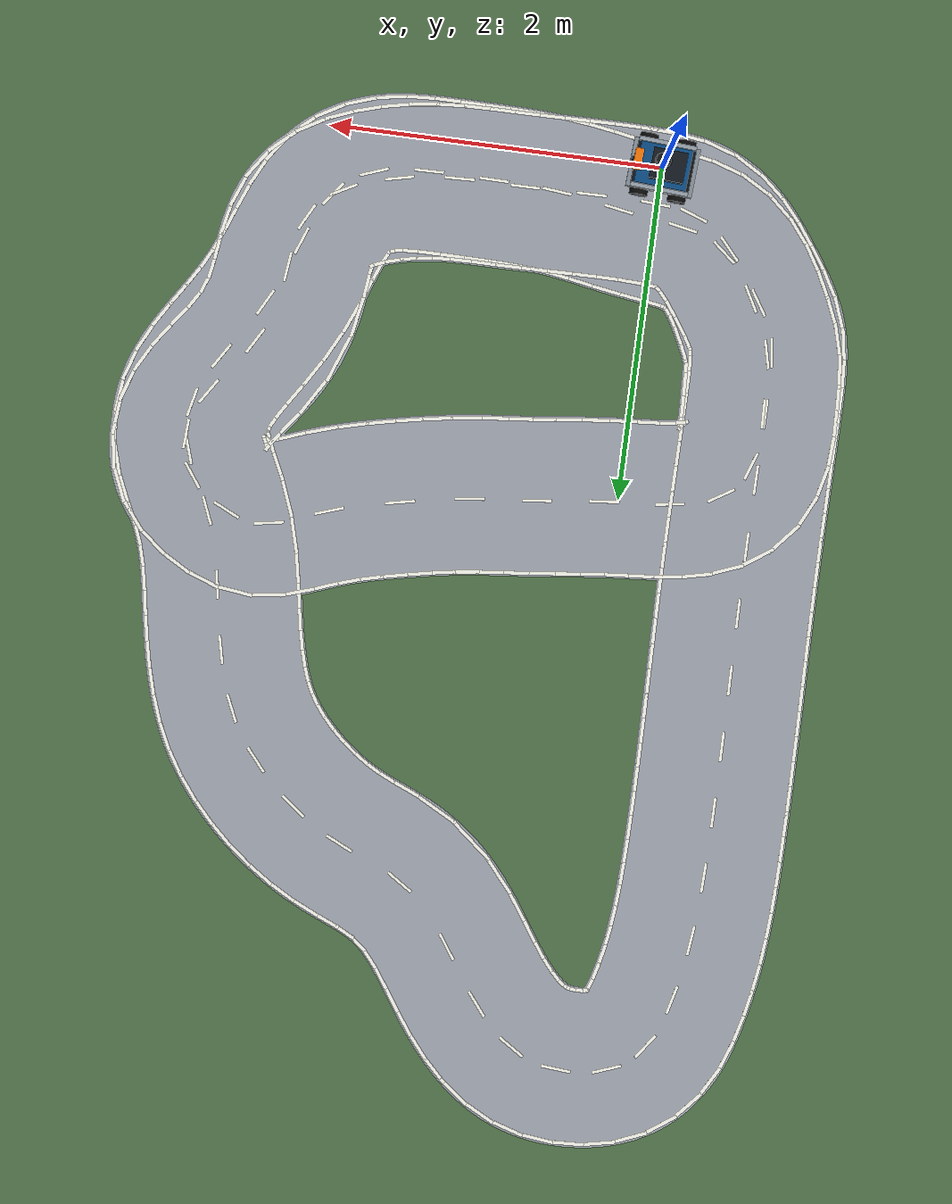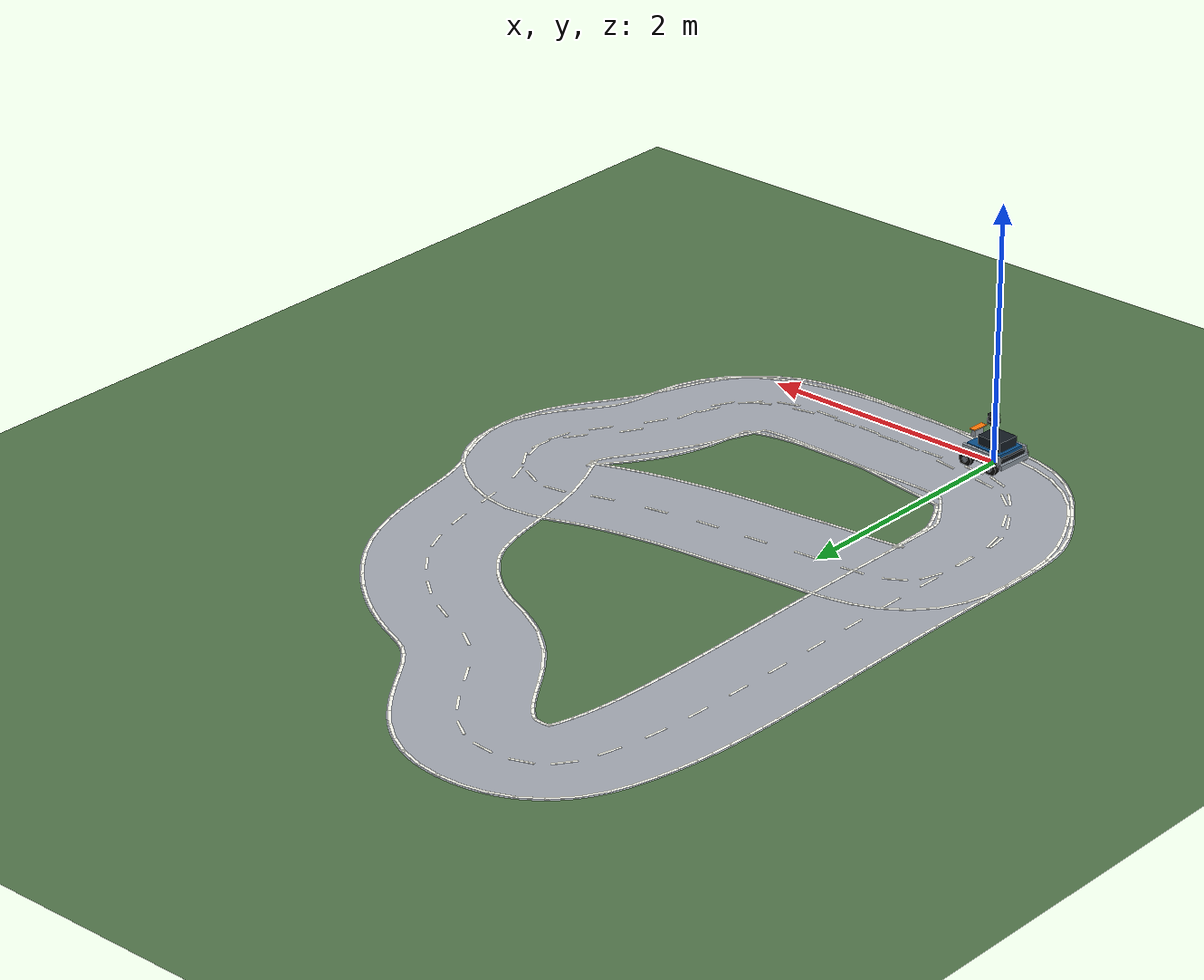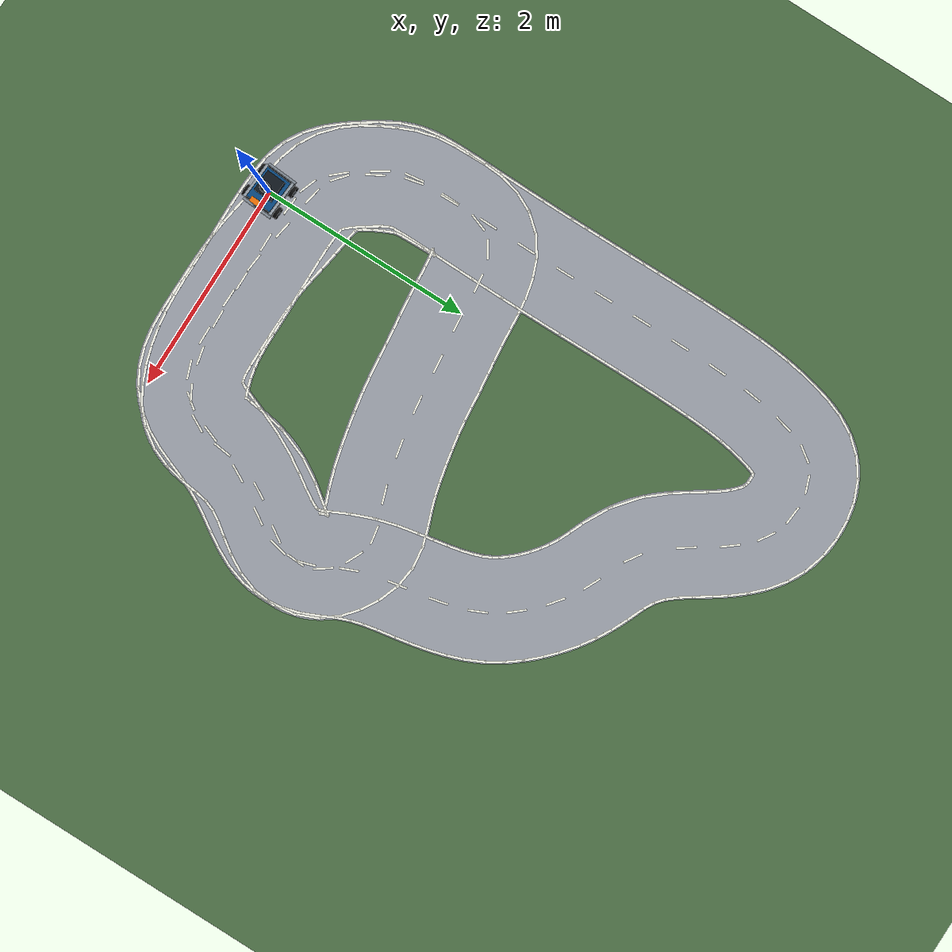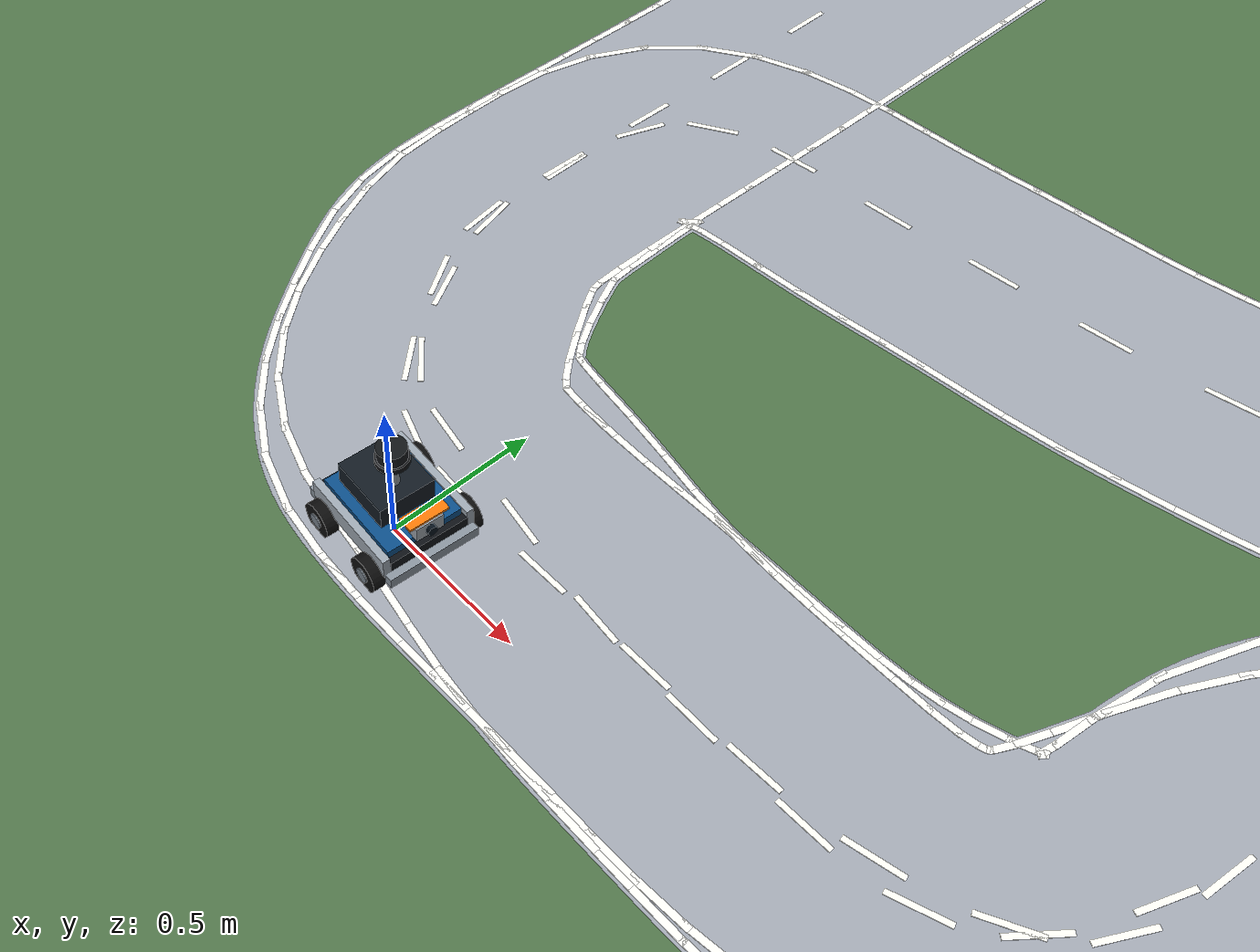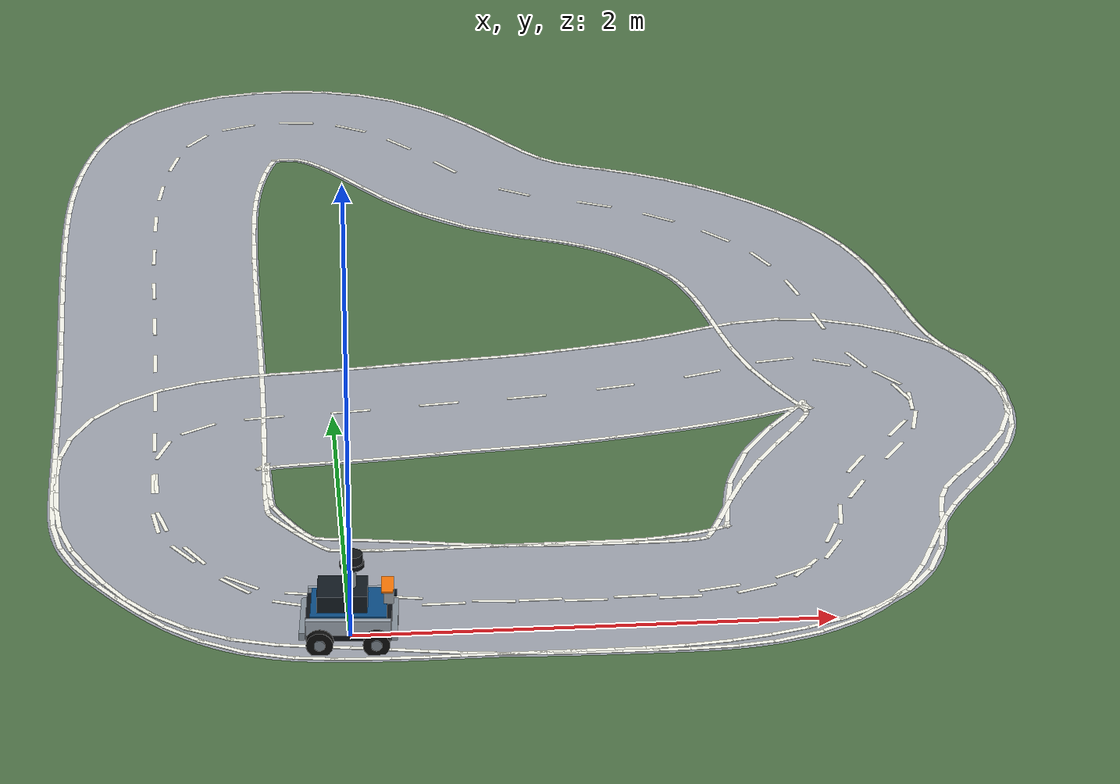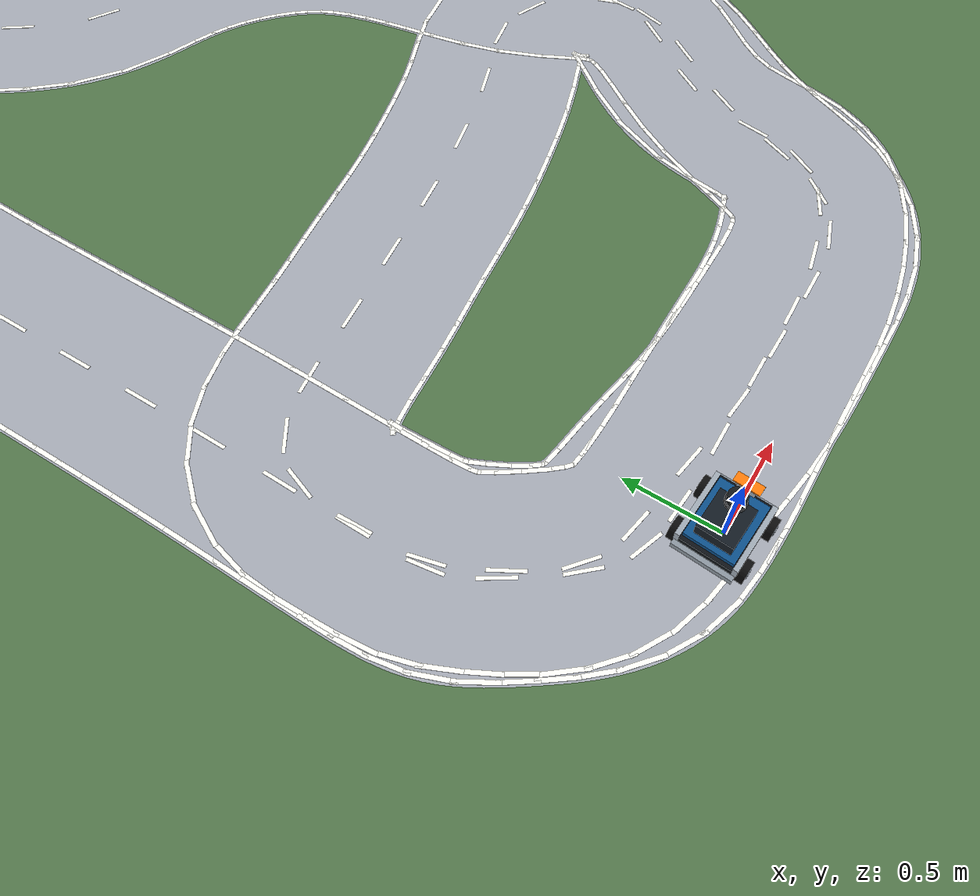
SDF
<?xml version="1.0" ?>
<sdf version="1.9">
  <world name="sami_track">
    <physics name="default" type="ignored">
      <max_step_size>0.004</max_step_size>
      <real_time_factor>1.0</real_time_factor>
    </physics>
    <plugin filename="gz-sim-physics-system" name="gz::sim::systems::Physics"/>
    <plugin filename="gz-sim-user-commands-system"
            name="gz::sim::systems::UserCommands"/>
    <plugin filename="gz-sim-scene-broadcaster-system"
            name="gz::sim::systems::SceneBroadcaster"/>
    <plugin filename="gz-sim-sensors-system"
            name="gz::sim::systems::Sensors">
      <render_engine>ogre2</render_engine>
    </plugin>

    <light type="directional" name="sun">
      <cast_shadows>false</cast_shadows>
      <pose>0 0 10 0 0 0</pose>
      <diffuse>0.9 0.9 0.9 1</diffuse>
      <direction>-0.3 0.2 -0.9</direction>
    </light>

    <model name="ground_plane">
      <static>true</static>
      <link name="link">
        <collision name="col">
          <geometry><plane><normal>0 0 1</normal>
            <size>60 60</size></plane></geometry>
        </collision>
        <visual name="vis">
          <geometry><plane><normal>0 0 1</normal>
            <size>60 60</size></plane></geometry>
          <material><ambient>0.24 0.34 0.22 1</ambient>
            <diffuse>0.32 0.46 0.29 1</diffuse></material>
        </visual>
      </link>
    </model>

    <model name="track_walls">
      <static>true</static>
      <link name="walls">
      <collision name="w0_col">
        <pose>2.1130 6.5440 0.1500 0 0 0</pose>
        <geometry><box><size>1.3500 0.0500 0.3000</size></box></geometry>
      </collision>
      <visual name="w0_vis">
        <pose>2.1130 6.5440 0.1500 0 0 0</pose>
        <geometry><box><size>1.3500 0.0500 0.3000</size></box></geometry>
        <!-- Occupancy-map boxes remain physical LiDAR/collision geometry,
             but are hidden so they do not cover the painted track in the
             operator view or camera image. -->
        <transparency>1.0</transparency>
        <cast_shadows>false</cast_shadows>
        <material><ambient>0.25 0.25 0.28 1</ambient>
          <diffuse>0.35 0.35 0.40 1</diffuse></material>
      </visual>
      <collision name="w1_col">
        <pose>0.6380 6.5440 0.1500 0 0 0</pose>
        <geometry><box><size>1.3000 0.0500 0.3000</size></box></geometry>
      </collision>
      <visual name="w1_vis">
        <pose>0.6380 6.5440 0.1500 0 0 0</pose>
        <geometry><box><size>1.3000 0.0500 0.3000</size></box></geometry>
        <!-- Occupancy-map boxes remain physical LiDAR/collision geometry,
             but are hidden so they do not cover the painted track in the
             operator view or camera image. -->
        <transparency>1.0</transparency>
        <cast_shadows>false</cast_shadows>
        <material><ambient>0.25 0.25 0.28 1</ambient>
          <diffuse>0.35 0.35 0.40 1</diffuse></material>
      </visual>
      <collision name="w2_col">
        <pose>-0.1870 6.5440 0.1500 0 0 0</pose>
        <geometry><box><size>0.1500 0.0500 0.3000</size></box></geometry>
      </collision>
      <visual name="w2_vis">
        <pose>-0.1870 6.5440 0.1500 0 0 0</pose>
        <geometry><box><size>0.1500 0.0500 0.3000</size></box></geometry>
        <!-- Occupancy-map boxes remain physical LiDAR/collision geometry,
             but are hidden so they do not cover the painted track in the
             operator view or camera image. -->
        <transparency>1.0</transparency>
        <cast_shadows>false</cast_shadows>
        <material><ambient>0.25 0.25 0.28 1</ambient>
          <diffuse>0.35 0.35 0.40 1</diffuse></material>
      </visual>
      <collision name="w3_col">
        <pose>-3.2120 6.4940 0.1500 0 0 0</pose>
        <geometry><box><size>0.8000 0.0500 0.3000</size></box></geometry>
      </collision>
      <visual name="w3_vis">
        <pose>-3.2120 6.4940 0.1500 0 0 0</pose>
        <geometry><box><size>0.8000 0.0500 0.3000</size></box></geometry>
        <!-- Occupancy-map boxes remain physical LiDAR/collision geometry,
             but are hidden so they do not cover the painted track in the
             operator view or camera image. -->
        <transparency>1.0</transparency>
        <cast_shadows>false</cast_shadows>
        <material><ambient>0.25 0.25 0.28 1</ambient>
          <diffuse>0.35 0.35 0.40 1</diffuse></material>
      </visual>
      <collision name="w4_col">
        <pose>2.8130 6.4940 0.1500 0 0 0</pose>
        <geometry><box><size>0.3500 0.0500 0.3000</size></box></geometry>
      </collision>
      <visual name="w4_vis">
        <pose>2.8130 6.4940 0.1500 0 0 0</pose>
        <geometry><box><size>0.3500 0.0500 0.3000</size></box></geometry>
        <!-- Occupancy-map boxes remain physical LiDAR/collision geometry,
             but are hidden so they do not cover the painted track in the
             operator view or camera image. -->
        <transparency>1.0</transparency>
        <cast_shadows>false</cast_shadows>
        <material><ambient>0.25 0.25 0.28 1</ambient>
          <diffuse>0.35 0.35 0.40 1</diffuse></material>
      </visual>
      <collision name="w5_col">
        <pose>-2.7120 6.4940 0.1500 0 0 0</pose>
        <geometry><box><size>0.1000 0.0500 0.3000</size></box></geometry>
      </collision>
      <visual name="w5_vis">
        <pose>-2.7120 6.4940 0.1500 0 0 0</pose>
        <geometry><box><size>0.1000 0.0500 0.3000</size></box></geometry>
        <!-- Occupancy-map boxes remain physical LiDAR/collision geometry,
             but are hidden so they do not cover the painted track in the
             operator view or camera image. -->
        <transparency>1.0</transparency>
        <cast_shadows>false</cast_shadows>
        <material><ambient>0.25 0.25 0.28 1</ambient>
          <diffuse>0.35 0.35 0.40 1</diffuse></material>
      </visual>
      <collision name="w6_col">
        <pose>1.8630 6.4940 0.1500 0 0 0</pose>
        <geometry><box><size>0.8500 0.0500 0.3000</size></box></geometry>
      </collision>
      <visual name="w6_vis">
        <pose>1.8630 6.4940 0.1500 0 0 0</pose>
        <geometry><box><size>0.8500 0.0500 0.3000</size></box></geometry>
        <!-- Occupancy-map boxes remain physical LiDAR/collision geometry,
             but are hidden so they do not cover the painted track in the
             operator view or camera image. -->
        <transparency>1.0</transparency>
        <cast_shadows>false</cast_shadows>
        <material><ambient>0.25 0.25 0.28 1</ambient>
          <diffuse>0.35 0.35 0.40 1</diffuse></material>
      </visual>
      <collision name="w7_col">
        <pose>0.4880 6.4940 0.1500 0 0 0</pose>
        <geometry><box><size>1.7000 0.0500 0.3000</size></box></geometry>
      </collision>
      <visual name="w7_vis">
        <pose>0.4880 6.4940 0.1500 0 0 0</pose>
        <geometry><box><size>1.7000 0.0500 0.3000</size></box></geometry>
        <!-- Occupancy-map boxes remain physical LiDAR/collision geometry,
             but are hidden so they do not cover the painted track in the
             operator view or camera image. -->
        <transparency>1.0</transparency>
        <cast_shadows>false</cast_shadows>
        <material><ambient>0.25 0.25 0.28 1</ambient>
          <diffuse>0.35 0.35 0.40 1</diffuse></material>
      </visual>
      <collision name="w8_col">
        <pose>2.4880 6.4940 0.1500 0 0 0</pose>
        <geometry><box><size>0.2000 0.0500 0.3000</size></box></geometry>
      </collision>
      <visual name="w8_vis">
        <pose>2.4880 6.4940 0.1500 0 0 0</pose>
        <geometry><box><size>0.2000 0.0500 0.3000</size></box></geometry>
        <!-- Occupancy-map boxes remain physical LiDAR/collision geometry,
             but are hidden so they do not cover the painted track in the
             operator view or camera image. -->
        <transparency>1.0</transparency>
        <cast_shadows>false</cast_shadows>
        <material><ambient>0.25 0.25 0.28 1</ambient>
          <diffuse>0.35 0.35 0.40 1</diffuse></material>
      </visual>
      <collision name="w9_col">
        <pose>-7.4870 6.4440 0.1500 0 0 0</pose>
        <geometry><box><size>0.0500 0.0500 0.3000</size></box></geometry>
      </collision>
      <visual name="w9_vis">
        <pose>-7.4870 6.4440 0.1500 0 0 0</pose>
        <geometry><box><size>0.0500 0.0500 0.3000</size></box></geometry>
        <!-- Occupancy-map boxes remain physical LiDAR/collision geometry,
             but are hidden so they do not cover the painted track in the
             operator view or camera image. -->
        <transparency>1.0</transparency>
        <cast_shadows>false</cast_shadows>
        <material><ambient>0.25 0.25 0.28 1</ambient>
          <diffuse>0.35 0.35 0.40 1</diffuse></material>
      </visual>
      <collision name="w10_col">
        <pose>1.3630 6.4440 0.1500 0 0 0</pose>
        <geometry><box><size>0.2500 0.0500 0.3000</size></box></geometry>
      </collision>
      <visual name="w10_vis">
        <pose>1.3630 6.4440 0.1500 0 0 0</pose>
        <geometry><box><size>0.2500 0.0500 0.3000</size></box></geometry>
        <!-- Occupancy-map boxes remain physical LiDAR/collision geometry,
             but are hidden so they do not cover the painted track in the
             operator view or camera image. -->
        <transparency>1.0</transparency>
        <cast_shadows>false</cast_shadows>
        <material><ambient>0.25 0.25 0.28 1</ambient>
          <diffuse>0.35 0.35 0.40 1</diffuse></material>
      </visual>
      <collision name="w11_col">
        <pose>-3.3620 6.4440 0.1500 0 0 0</pose>
        <geometry><box><size>1.5000 0.0500 0.3000</size></box></geometry>
      </collision>
      <visual name="w11_vis">
        <pose>-3.3620 6.4440 0.1500 0 0 0</pose>
        <geometry><box><size>1.5000 0.0500 0.3000</size></box></geometry>
        <!-- Occupancy-map boxes remain physical LiDAR/collision geometry,
             but are hidden so they do not cover the painted track in the
             operator view or camera image. -->
        <transparency>1.0</transparency>
        <cast_shadows>false</cast_shadows>
        <material><ambient>0.25 0.25 0.28 1</ambient>
          <diffuse>0.35 0.35 0.40 1</diffuse></material>
      </visual>
      <collision name="w12_col">
        <pose>2.8630 6.4440 0.1500 0 0 0</pose>
        <geometry><box><size>0.3500 0.0500 0.3000</size></box></geometry>
      </collision>
      <visual name="w12_vis">
        <pose>2.8630 6.4440 0.1500 0 0 0</pose>
        <geometry><box><size>0.3500 0.0500 0.3000</size></box></geometry>
        <!-- Occupancy-map boxes remain physical LiDAR/collision geometry,
             but are hidden so they do not cover the painted track in the
             operator view or camera image. -->
        <transparency>1.0</transparency>
        <cast_shadows>false</cast_shadows>
        <material><ambient>0.25 0.25 0.28 1</ambient>
          <diffuse>0.35 0.35 0.40 1</diffuse></material>
      </visual>
      <collision name="w13_col">
        <pose>-0.7870 6.4440 0.1500 0 0 0</pose>
        <geometry><box><size>1.6500 0.0500 0.3000</size></box></geometry>
      </collision>
      <visual name="w13_vis">
        <pose>-0.7870 6.4440 0.1500 0 0 0</pose>
        <geometry><box><size>1.6500 0.0500 0.3000</size></box></geometry>
        <!-- Occupancy-map boxes remain physical LiDAR/collision geometry,
             but are hidden so they do not cover the painted track in the
             operator view or camera image. -->
        <transparency>1.0</transparency>
        <cast_shadows>false</cast_shadows>
        <material><ambient>0.25 0.25 0.28 1</ambient>
          <diffuse>0.35 0.35 0.40 1</diffuse></material>
      </visual>
      <collision name="w14_col">
        <pose>-4.6120 6.3940 0.1500 0 0 0</pose>
        <geometry><box><size>0.1000 0.0500 0.3000</size></box></geometry>
      </collision>
      <visual name="w14_vis">
        <pose>-4.6120 6.3940 0.1500 0 0 0</pose>
        <geometry><box><size>0.1000 0.0500 0.3000</size></box></geometry>
        <!-- Occupancy-map boxes remain physical LiDAR/collision geometry,
             but are hidden so they do not cover the painted track in the
             operator view or camera image. -->
        <transparency>1.0</transparency>
        <cast_shadows>false</cast_shadows>
        <material><ambient>0.25 0.25 0.28 1</ambient>
          <diffuse>0.35 0.35 0.40 1</diffuse></material>
      </visual>
      <collision name="w15_col">
        <pose>-3.0620 6.3940 0.1500 0 0 0</pose>
        <geometry><box><size>0.2000 0.0500 0.3000</size></box></geometry>
      </collision>
      <visual name="w15_vis">
        <pose>-3.0620 6.3940 0.1500 0 0 0</pose>
        <geometry><box><size>0.2000 0.0500 0.3000</size></box></geometry>
        <!-- Occupancy-map boxes remain physical LiDAR/collision geometry,
             but are hidden so they do not cover the painted track in the
             operator view or camera image. -->
        <transparency>1.0</transparency>
        <cast_shadows>false</cast_shadows>
        <material><ambient>0.25 0.25 0.28 1</ambient>
          <diffuse>0.35 0.35 0.40 1</diffuse></material>
      </visual>
      <collision name="w16_col">
        <pose>3.1630 6.3940 0.1500 0 0 0</pose>
        <geometry><box><size>0.4500 0.0500 0.3000</size></box></geometry>
      </collision>
      <visual name="w16_vis">
        <pose>3.1630 6.3940 0.1500 0 0 0</pose>
        <geometry><box><size>0.4500 0.0500 0.3000</size></box></geometry>
        <!-- Occupancy-map boxes remain physical LiDAR/collision geometry,
             but are hidden so they do not cover the painted track in the
             operator view or camera image. -->
        <transparency>1.0</transparency>
        <cast_shadows>false</cast_shadows>
        <material><ambient>0.25 0.25 0.28 1</ambient>
          <diffuse>0.35 0.35 0.40 1</diffuse></material>
      </visual>
      <collision name="w17_col">
        <pose>-1.7370 6.3940 0.1500 0 0 0</pose>
        <geometry><box><size>0.0500 0.0500 0.3000</size></box></geometry>
      </collision>
      <visual name="w17_vis">
        <pose>-1.7370 6.3940 0.1500 0 0 0</pose>
        <geometry><box><size>0.0500 0.0500 0.3000</size></box></geometry>
        <!-- Occupancy-map boxes remain physical LiDAR/collision geometry,
             but are hidden so they do not cover the painted track in the
             operator view or camera image. -->
        <transparency>1.0</transparency>
        <cast_shadows>false</cast_shadows>
        <material><ambient>0.25 0.25 0.28 1</ambient>
          <diffuse>0.35 0.35 0.40 1</diffuse></material>
      </visual>
      <collision name="w18_col">
        <pose>-0.9120 6.3940 0.1500 0 0 0</pose>
        <geometry><box><size>1.4000 0.0500 0.3000</size></box></geometry>
      </collision>
      <visual name="w18_vis">
        <pose>-0.9120 6.3940 0.1500 0 0 0</pose>
        <geometry><box><size>1.4000 0.0500 0.3000</size></box></geometry>
        <!-- Occupancy-map boxes remain physical LiDAR/collision geometry,
             but are hidden so they do not cover the painted track in the
             operator view or camera image. -->
        <transparency>1.0</transparency>
        <cast_shadows>false</cast_shadows>
        <material><ambient>0.25 0.25 0.28 1</ambient>
          <diffuse>0.35 0.35 0.40 1</diffuse></material>
      </visual>
      <collision name="w19_col">
        <pose>1.3380 6.3940 0.1500 0 0 0</pose>
        <geometry><box><size>0.2000 0.0500 0.3000</size></box></geometry>
      </collision>
      <visual name="w19_vis">
        <pose>1.3380 6.3940 0.1500 0 0 0</pose>
        <geometry><box><size>0.2000 0.0500 0.3000</size></box></geometry>
        <!-- Occupancy-map boxes remain physical LiDAR/collision geometry,
             but are hidden so they do not cover the painted track in the
             operator view or camera image. -->
        <transparency>1.0</transparency>
        <cast_shadows>false</cast_shadows>
        <material><ambient>0.25 0.25 0.28 1</ambient>
          <diffuse>0.35 0.35 0.40 1</diffuse></material>
      </visual>
      <collision name="w20_col">
        <pose>-3.7620 6.3940 0.1500 0 0 0</pose>
        <geometry><box><size>0.8000 0.0500 0.3000</size></box></geometry>
      </collision>
      <visual name="w20_vis">
        <pose>-3.7620 6.3940 0.1500 0 0 0</pose>
        <geometry><box><size>0.8000 0.0500 0.3000</size></box></geometry>
        <!-- Occupancy-map boxes remain physical LiDAR/collision geometry,
             but are hidden so they do not cover the painted track in the
             operator view or camera image. -->
        <transparency>1.0</transparency>
        <cast_shadows>false</cast_shadows>
        <material><ambient>0.25 0.25 0.28 1</ambient>
          <diffuse>0.35 0.35 0.40 1</diffuse></material>
      </visual>
      <collision name="w21_col">
        <pose>-2.6370 6.3940 0.1500 0 0 0</pose>
        <geometry><box><size>0.1500 0.0500 0.3000</size></box></geometry>
      </collision>
      <visual name="w21_vis">
        <pose>-2.6370 6.3940 0.1500 0 0 0</pose>
        <geometry><box><size>0.1500 0.0500 0.3000</size></box></geometry>
        <!-- Occupancy-map boxes remain physical LiDAR/collision geometry,
             but are hidden so they do not cover the painted track in the
             operator view or camera image. -->
        <transparency>1.0</transparency>
        <cast_shadows>false</cast_shadows>
        <material><ambient>0.25 0.25 0.28 1</ambient>
          <diffuse>0.35 0.35 0.40 1</diffuse></material>
      </visual>
      <collision name="w22_col">
        <pose>-0.0870 6.3940 0.1500 0 0 0</pose>
        <geometry><box><size>0.1500 0.0500 0.3000</size></box></geometry>
      </collision>
      <visual name="w22_vis">
        <pose>-0.0870 6.3940 0.1500 0 0 0</pose>
        <geometry><box><size>0.1500 0.0500 0.3000</size></box></geometry>
        <!-- Occupancy-map boxes remain physical LiDAR/collision geometry,
             but are hidden so they do not cover the painted track in the
             operator view or camera image. -->
        <transparency>1.0</transparency>
        <cast_shadows>false</cast_shadows>
        <material><ambient>0.25 0.25 0.28 1</ambient>
          <diffuse>0.35 0.35 0.40 1</diffuse></material>
      </visual>
      <collision name="w23_col">
        <pose>-7.5620 6.3690 0.1500 0 0 0</pose>
        <geometry><box><size>0.2000 0.1000 0.3000</size></box></geometry>
      </collision>
      <visual name="w23_vis">
        <pose>-7.5620 6.3690 0.1500 0 0 0</pose>
        <geometry><box><size>0.2000 0.1000 0.3000</size></box></geometry>
        <!-- Occupancy-map boxes remain physical LiDAR/collision geometry,
             but are hidden so they do not cover the painted track in the
             operator view or camera image. -->
        <transparency>1.0</transparency>
        <cast_shadows>false</cast_shadows>
        <material><ambient>0.25 0.25 0.28 1</ambient>
          <diffuse>0.35 0.35 0.40 1</diffuse></material>
      </visual>
      <collision name="w24_col">
        <pose>-2.5620 6.3440 0.1500 0 0 0</pose>
        <geometry><box><size>0.2000 0.0500 0.3000</size></box></geometry>
      </collision>
      <visual name="w24_vis">
        <pose>-2.5620 6.3440 0.1500 0 0 0</pose>
        <geometry><box><size>0.2000 0.0500 0.3000</size></box></geometry>
        <!-- Occupancy-map boxes remain physical LiDAR/collision geometry,
             but are hidden so they do not cover the painted track in the
             operator view or camera image. -->
        <transparency>1.0</transparency>
        <cast_shadows>false</cast_shadows>
        <material><ambient>0.25 0.25 0.28 1</ambient>
          <diffuse>0.35 0.35 0.40 1</diffuse></material>
      </visual>
      <collision name="w25_col">
        <pose>1.3630 6.3440 0.1500 0 0 0</pose>
        <geometry><box><size>0.2500 0.0500 0.3000</size></box></geometry>
      </collision>
      <visual name="w25_vis">
        <pose>1.3630 6.3440 0.1500 0 0 0</pose>
        <geometry><box><size>0.2500 0.0500 0.3000</size></box></geometry>
        <!-- Occupancy-map boxes remain physical LiDAR/collision geometry,
             but are hidden so they do not cover the painted track in the
             operator view or camera image. -->
        <transparency>1.0</transparency>
        <cast_shadows>false</cast_shadows>
        <material><ambient>0.25 0.25 0.28 1</ambient>
          <diffuse>0.35 0.35 0.40 1</diffuse></material>
      </visual>
      <collision name="w26_col">
        <pose>-2.0370 6.3440 0.1500 0 0 0</pose>
        <geometry><box><size>0.6500 0.0500 0.3000</size></box></geometry>
      </collision>
      <visual name="w26_vis">
        <pose>-2.0370 6.3440 0.1500 0 0 0</pose>
        <geometry><box><size>0.6500 0.0500 0.3000</size></box></geometry>
        <!-- Occupancy-map boxes remain physical LiDAR/collision geometry,
             but are hidden so they do not cover the painted track in the
             operator view or camera image. -->
        <transparency>1.0</transparency>
        <cast_shadows>false</cast_shadows>
        <material><ambient>0.25 0.25 0.28 1</ambient>
          <diffuse>0.35 0.35 0.40 1</diffuse></material>
      </visual>
      <collision name="w27_col">
        <pose>3.3880 6.3440 0.1500 0 0 0</pose>
        <geometry><box><size>0.1000 0.0500 0.3000</size></box></geometry>
      </collision>
      <visual name="w27_vis">
        <pose>3.3880 6.3440 0.1500 0 0 0</pose>
        <geometry><box><size>0.1000 0.0500 0.3000</size></box></geometry>
        <!-- Occupancy-map boxes remain physical LiDAR/collision geometry,
             but are hidden so they do not cover the painted track in the
             operator view or camera image. -->
        <transparency>1.0</transparency>
        <cast_shadows>false</cast_shadows>
        <material><ambient>0.25 0.25 0.28 1</ambient>
          <diffuse>0.35 0.35 0.40 1</diffuse></material>
      </visual>
      <collision name="w28_col">
        <pose>-4.4870 6.3440 0.1500 0 0 0</pose>
        <geometry><box><size>0.3500 0.0500 0.3000</size></box></geometry>
      </collision>
      <visual name="w28_vis">
        <pose>-4.4870 6.3440 0.1500 0 0 0</pose>
        <geometry><box><size>0.3500 0.0500 0.3000</size></box></geometry>
        <!-- Occupancy-map boxes remain physical LiDAR/collision geometry,
             but are hidden so they do not cover the painted track in the
             operator view or camera image. -->
        <transparency>1.0</transparency>
        <cast_shadows>false</cast_shadows>
        <material><ambient>0.25 0.25 0.28 1</ambient>
          <diffuse>0.35 0.35 0.40 1</diffuse></material>
      </visual>
      <collision name="w29_col">
        <pose>-0.9370 6.3440 0.1500 0 0 0</pose>
        <geometry><box><size>1.3500 0.0500 0.3000</size></box></geometry>
      </collision>
      <visual name="w29_vis">
        <pose>-0.9370 6.3440 0.1500 0 0 0</pose>
        <geometry><box><size>1.3500 0.0500 0.3000</size></box></geometry>
        <!-- Occupancy-map boxes remain physical LiDAR/collision geometry,
             but are hidden so they do not cover the painted track in the
             operator view or camera image. -->
        <transparency>1.0</transparency>
        <cast_shadows>false</cast_shadows>
        <material><ambient>0.25 0.25 0.28 1</ambient>
          <diffuse>0.35 0.35 0.40 1</diffuse></material>
      </visual>
      <collision name="w30_col">
        <pose>-4.1120 6.3440 0.1500 0 0 0</pose>
        <geometry><box><size>0.1000 0.0500 0.3000</size></box></geometry>
      </collision>
      <visual name="w30_vis">
        <pose>-4.1120 6.3440 0.1500 0 0 0</pose>
        <geometry><box><size>0.1000 0.0500 0.3000</size></box></geometry>
        <!-- Occupancy-map boxes remain physical LiDAR/collision geometry,
             but are hidden so they do not cover the painted track in the
             operator view or camera image. -->
        <transparency>1.0</transparency>
        <cast_shadows>false</cast_shadows>
        <material><ambient>0.25 0.25 0.28 1</ambient>
          <diffuse>0.35 0.35 0.40 1</diffuse></material>
      </visual>
      <collision name="w31_col">
        <pose>-2.1870 6.2940 0.1500 0 0 0</pose>
        <geometry><box><size>0.7500 0.0500 0.3000</size></box></geometry>
      </collision>
      <visual name="w31_vis">
        <pose>-2.1870 6.2940 0.1500 0 0 0</pose>
        <geometry><box><size>0.7500 0.0500 0.3000</size></box></geometry>
        <!-- Occupancy-map boxes remain physical LiDAR/collision geometry,
             but are hidden so they do not cover the painted track in the
             operator view or camera image. -->
        <transparency>1.0</transparency>
        <cast_shadows>false</cast_shadows>
        <material><ambient>0.25 0.25 0.28 1</ambient>
          <diffuse>0.35 0.35 0.40 1</diffuse></material>
      </visual>
      <collision name="w32_col">
        <pose>-4.3870 6.2940 0.1500 0 0 0</pose>
        <geometry><box><size>0.6500 0.0500 0.3000</size></box></geometry>
      </collision>
      <visual name="w32_vis">
        <pose>-4.3870 6.2940 0.1500 0 0 0</pose>
        <geometry><box><size>0.6500 0.0500 0.3000</size></box></geometry>
        <!-- Occupancy-map boxes remain physical LiDAR/collision geometry,
             but are hidden so they do not cover the painted track in the
             operator view or camera image. -->
        <transparency>1.0</transparency>
        <cast_shadows>false</cast_shadows>
        <material><ambient>0.25 0.25 0.28 1</ambient>
          <diffuse>0.35 0.35 0.40 1</diffuse></material>
      </visual>
      <collision name="w33_col">
        <pose>-1.3870 6.2940 0.1500 0 0 0</pose>
        <geometry><box><size>0.3500 0.0500 0.3000</size></box></geometry>
      </collision>
      <visual name="w33_vis">
        <pose>-1.3870 6.2940 0.1500 0 0 0</pose>
        <geometry><box><size>0.3500 0.0500 0.3000</size></box></geometry>
        <!-- Occupancy-map boxes remain physical LiDAR/collision geometry,
             but are hidden so they do not cover the painted track in the
             operator view or camera image. -->
        <transparency>1.0</transparency>
        <cast_shadows>false</cast_shadows>
        <material><ambient>0.25 0.25 0.28 1</ambient>
          <diffuse>0.35 0.35 0.40 1</diffuse></material>
      </visual>
      <collision name="w34_col">
        <pose>1.3630 6.2940 0.1500 0 0 0</pose>
        <geometry><box><size>0.1500 0.0500 0.3000</size></box></geometry>
      </collision>
      <visual name="w34_vis">
        <pose>1.3630 6.2940 0.1500 0 0 0</pose>
        <geometry><box><size>0.1500 0.0500 0.3000</size></box></geometry>
        <!-- Occupancy-map boxes remain physical LiDAR/collision geometry,
             but are hidden so they do not cover the painted track in the
             operator view or camera image. -->
        <transparency>1.0</transparency>
        <cast_shadows>false</cast_shadows>
        <material><ambient>0.25 0.25 0.28 1</ambient>
          <diffuse>0.35 0.35 0.40 1</diffuse></material>
      </visual>
      <collision name="w35_col">
        <pose>-7.6620 6.2690 0.1500 0 0 0</pose>
        <geometry><box><size>0.1000 0.1000 0.3000</size></box></geometry>
      </collision>
      <visual name="w35_vis">
        <pose>-7.6620 6.2690 0.1500 0 0 0</pose>
        <geometry><box><size>0.1000 0.1000 0.3000</size></box></geometry>
        <!-- Occupancy-map boxes remain physical LiDAR/collision geometry,
             but are hidden so they do not cover the painted track in the
             operator view or camera image. -->
        <transparency>1.0</transparency>
        <cast_shadows>false</cast_shadows>
        <material><ambient>0.25 0.25 0.28 1</ambient>
          <diffuse>0.35 0.35 0.40 1</diffuse></material>
      </visual>
      <collision name="w36_col">
        <pose>-2.3870 6.2440 0.1500 0 0 0</pose>
        <geometry><box><size>0.1500 0.0500 0.3000</size></box></geometry>
      </collision>
      <visual name="w36_vis">
        <pose>-2.3870 6.2440 0.1500 0 0 0</pose>
        <geometry><box><size>0.1500 0.0500 0.3000</size></box></geometry>
        <!-- Occupancy-map boxes remain physical LiDAR/collision geometry,
             but are hidden so they do not cover the painted track in the
             operator view or camera image. -->
        <transparency>1.0</transparency>
        <cast_shadows>false</cast_shadows>
        <material><ambient>0.25 0.25 0.28 1</ambient>
          <diffuse>0.35 0.35 0.40 1</diffuse></material>
      </visual>
      <collision name="w37_col">
        <pose>-4.3870 6.2440 0.1500 0 0 0</pose>
        <geometry><box><size>0.5500 0.0500 0.3000</size></box></geometry>
      </collision>
      <visual name="w37_vis">
        <pose>-4.3870 6.2440 0.1500 0 0 0</pose>
        <geometry><box><size>0.5500 0.0500 0.3000</size></box></geometry>
        <!-- Occupancy-map boxes remain physical LiDAR/collision geometry,
             but are hidden so they do not cover the painted track in the
             operator view or camera image. -->
        <transparency>1.0</transparency>
        <cast_shadows>false</cast_shadows>
        <material><ambient>0.25 0.25 0.28 1</ambient>
          <diffuse>0.35 0.35 0.40 1</diffuse></material>
      </visual>
      <collision name="w38_col">
        <pose>-1.4870 6.2440 0.1500 0 0 0</pose>
        <geometry><box><size>0.1500 0.0500 0.3000</size></box></geometry>
      </collision>
      <visual name="w38_vis">
        <pose>-1.4870 6.2440 0.1500 0 0 0</pose>
        <geometry><box><size>0.1500 0.0500 0.3000</size></box></geometry>
        <!-- Occupancy-map boxes remain physical LiDAR/collision geometry,
             but are hidden so they do not cover the painted track in the
             operator view or camera image. -->
        <transparency>1.0</transparency>
        <cast_shadows>false</cast_shadows>
        <material><ambient>0.25 0.25 0.28 1</ambient>
          <diffuse>0.35 0.35 0.40 1</diffuse></material>
      </visual>
      <collision name="w39_col">
        <pose>-7.6370 6.1940 0.1500 0 0 0</pose>
        <geometry><box><size>0.0500 0.0500 0.3000</size></box></geometry>
      </collision>
      <visual name="w39_vis">
        <pose>-7.6370 6.1940 0.1500 0 0 0</pose>
        <geometry><box><size>0.0500 0.0500 0.3000</size></box></geometry>
        <!-- Occupancy-map boxes remain physical LiDAR/collision geometry,
             but are hidden so they do not cover the painted track in the
             operator view or camera image. -->
        <transparency>1.0</transparency>
        <cast_shadows>false</cast_shadows>
        <material><ambient>0.25 0.25 0.28 1</ambient>
          <diffuse>0.35 0.35 0.40 1</diffuse></material>
      </visual>
      <collision name="w40_col">
        <pose>-4.2120 6.1940 0.1500 0 0 0</pose>
        <geometry><box><size>0.1000 0.0500 0.3000</size></box></geometry>
      </collision>
      <visual name="w40_vis">
        <pose>-4.2120 6.1940 0.1500 0 0 0</pose>
        <geometry><box><size>0.1000 0.0500 0.3000</size></box></geometry>
        <!-- Occupancy-map boxes remain physical LiDAR/collision geometry,
             but are hidden so they do not cover the painted track in the
             operator view or camera image. -->
        <transparency>1.0</transparency>
        <cast_shadows>false</cast_shadows>
        <material><ambient>0.25 0.25 0.28 1</ambient>
          <diffuse>0.35 0.35 0.40 1</diffuse></material>
      </visual>
      <collision name="w41_col">
        <pose>1.3130 6.1440 0.1500 0 0 0</pose>
        <geometry><box><size>0.0500 0.2500 0.3000</size></box></geometry>
      </collision>
      <visual name="w41_vis">
        <pose>1.3130 6.1440 0.1500 0 0 0</pose>
        <geometry><box><size>0.0500 0.2500 0.3000</size></box></geometry>
        <!-- Occupancy-map boxes remain physical LiDAR/collision geometry,
             but are hidden so they do not cover the painted track in the
             operator view or camera image. -->
        <transparency>1.0</transparency>
        <cast_shadows>false</cast_shadows>
        <material><ambient>0.25 0.25 0.28 1</ambient>
          <diffuse>0.35 0.35 0.40 1</diffuse></material>
      </visual>
      <collision name="w42_col">
        <pose>-4.3120 6.0440 0.1500 0 0 0</pose>
        <geometry><box><size>0.1000 0.0500 0.3000</size></box></geometry>
      </collision>
      <visual name="w42_vis">
        <pose>-4.3120 6.0440 0.1500 0 0 0</pose>
        <geometry><box><size>0.1000 0.0500 0.3000</size></box></geometry>
        <!-- Occupancy-map boxes remain physical LiDAR/collision geometry,
             but are hidden so they do not cover the painted track in the
             operator view or camera image. -->
        <transparency>1.0</transparency>
        <cast_shadows>false</cast_shadows>
        <material><ambient>0.25 0.25 0.28 1</ambient>
          <diffuse>0.35 0.35 0.40 1</diffuse></material>
      </visual>
      <collision name="w43_col">
        <pose>-7.6120 6.0190 0.1500 0 0 0</pose>
        <geometry><box><size>0.1000 0.1000 0.3000</size></box></geometry>
      </collision>
      <visual name="w43_vis">
        <pose>-7.6120 6.0190 0.1500 0 0 0</pose>
        <geometry><box><size>0.1000 0.1000 0.3000</size></box></geometry>
        <!-- Occupancy-map boxes remain physical LiDAR/collision geometry,
             but are hidden so they do not cover the painted track in the
             operator view or camera image. -->
        <transparency>1.0</transparency>
        <cast_shadows>false</cast_shadows>
        <material><ambient>0.25 0.25 0.28 1</ambient>
          <diffuse>0.35 0.35 0.40 1</diffuse></material>
      </visual>
      <collision name="w44_col">
        <pose>-4.2620 5.9940 0.1500 0 0 0</pose>
        <geometry><box><size>0.1000 0.0500 0.3000</size></box></geometry>
      </collision>
      <visual name="w44_vis">
        <pose>-4.2620 5.9940 0.1500 0 0 0</pose>
        <geometry><box><size>0.1000 0.0500 0.3000</size></box></geometry>
        <!-- Occupancy-map boxes remain physical LiDAR/collision geometry,
             but are hidden so they do not cover the painted track in the
             operator view or camera image. -->
        <transparency>1.0</transparency>
        <cast_shadows>false</cast_shadows>
        <material><ambient>0.25 0.25 0.28 1</ambient>
          <diffuse>0.35 0.35 0.40 1</diffuse></material>
      </visual>
      <collision name="w45_col">
        <pose>-7.6370 5.9440 0.1500 0 0 0</pose>
        <geometry><box><size>0.1500 0.0500 0.3000</size></box></geometry>
      </collision>
      <visual name="w45_vis">
        <pose>-7.6370 5.9440 0.1500 0 0 0</pose>
        <geometry><box><size>0.1500 0.0500 0.3000</size></box></geometry>
        <!-- Occupancy-map boxes remain physical LiDAR/collision geometry,
             but are hidden so they do not cover the painted track in the
             operator view or camera image. -->
        <transparency>1.0</transparency>
        <cast_shadows>false</cast_shadows>
        <material><ambient>0.25 0.25 0.28 1</ambient>
          <diffuse>0.35 0.35 0.40 1</diffuse></material>
      </visual>
      <collision name="w46_col">
        <pose>-4.1620 5.9190 0.1500 0 0 0</pose>
        <geometry><box><size>0.2000 0.1000 0.3000</size></box></geometry>
      </collision>
      <visual name="w46_vis">
        <pose>-4.1620 5.9190 0.1500 0 0 0</pose>
        <geometry><box><size>0.2000 0.1000 0.3000</size></box></geometry>
        <!-- Occupancy-map boxes remain physical LiDAR/collision geometry,
             but are hidden so they do not cover the painted track in the
             operator view or camera image. -->
        <transparency>1.0</transparency>
        <cast_shadows>false</cast_shadows>
        <material><ambient>0.25 0.25 0.28 1</ambient>
          <diffuse>0.35 0.35 0.40 1</diffuse></material>
      </visual>
      <collision name="w47_col">
        <pose>-7.6120 5.8940 0.1500 0 0 0</pose>
        <geometry><box><size>0.1000 0.0500 0.3000</size></box></geometry>
      </collision>
      <visual name="w47_vis">
        <pose>-7.6120 5.8940 0.1500 0 0 0</pose>
        <geometry><box><size>0.1000 0.0500 0.3000</size></box></geometry>
        <!-- Occupancy-map boxes remain physical LiDAR/collision geometry,
             but are hidden so they do not cover the painted track in the
             operator view or camera image. -->
        <transparency>1.0</transparency>
        <cast_shadows>false</cast_shadows>
        <material><ambient>0.25 0.25 0.28 1</ambient>
          <diffuse>0.35 0.35 0.40 1</diffuse></material>
      </visual>
      <collision name="w48_col">
        <pose>-4.1370 5.8440 0.1500 0 0 0</pose>
        <geometry><box><size>0.2500 0.0500 0.3000</size></box></geometry>
      </collision>
      <visual name="w48_vis">
        <pose>-4.1370 5.8440 0.1500 0 0 0</pose>
        <geometry><box><size>0.2500 0.0500 0.3000</size></box></geometry>
        <!-- Occupancy-map boxes remain physical LiDAR/collision geometry,
             but are hidden so they do not cover the painted track in the
             operator view or camera image. -->
        <transparency>1.0</transparency>
        <cast_shadows>false</cast_shadows>
        <material><ambient>0.25 0.25 0.28 1</ambient>
          <diffuse>0.35 0.35 0.40 1</diffuse></material>
      </visual>
      <collision name="w49_col">
        <pose>1.3380 5.8940 0.1500 0 0 0</pose>
        <geometry><box><size>0.1000 0.2500 0.3000</size></box></geometry>
      </collision>
      <visual name="w49_vis">
        <pose>1.3380 5.8940 0.1500 0 0 0</pose>
        <geometry><box><size>0.1000 0.2500 0.3000</size></box></geometry>
        <!-- Occupancy-map boxes remain physical LiDAR/collision geometry,
             but are hidden so they do not cover the painted track in the
             operator view or camera image. -->
        <transparency>1.0</transparency>
        <cast_shadows>false</cast_shadows>
        <material><ambient>0.25 0.25 0.28 1</ambient>
          <diffuse>0.35 0.35 0.40 1</diffuse></material>
      </visual>
      <collision name="w50_col">
        <pose>-4.0870 5.7940 0.1500 0 0 0</pose>
        <geometry><box><size>0.2500 0.0500 0.3000</size></box></geometry>
      </collision>
      <visual name="w50_vis">
        <pose>-4.0870 5.7940 0.1500 0 0 0</pose>
        <geometry><box><size>0.2500 0.0500 0.3000</size></box></geometry>
        <!-- Occupancy-map boxes remain physical LiDAR/collision geometry,
             but are hidden so they do not cover the painted track in the
             operator view or camera image. -->
        <transparency>1.0</transparency>
        <cast_shadows>false</cast_shadows>
        <material><ambient>0.25 0.25 0.28 1</ambient>
          <diffuse>0.35 0.35 0.40 1</diffuse></material>
      </visual>
      <collision name="w51_col">
        <pose>1.3630 5.7440 0.1500 0 0 0</pose>
        <geometry><box><size>0.1500 0.0500 0.3000</size></box></geometry>
      </collision>
      <visual name="w51_vis">
        <pose>1.3630 5.7440 0.1500 0 0 0</pose>
        <geometry><box><size>0.1500 0.0500 0.3000</size></box></geometry>
        <!-- Occupancy-map boxes remain physical LiDAR/collision geometry,
             but are hidden so they do not cover the painted track in the
             operator view or camera image. -->
        <transparency>1.0</transparency>
        <cast_shadows>false</cast_shadows>
        <material><ambient>0.25 0.25 0.28 1</ambient>
          <diffuse>0.35 0.35 0.40 1</diffuse></material>
      </visual>
      <collision name="w52_col">
        <pose>-4.2120 5.7190 0.1500 0 0 0</pose>
        <geometry><box><size>0.6000 0.1000 0.3000</size></box></geometry>
      </collision>
      <visual name="w52_vis">
        <pose>-4.2120 5.7190 0.1500 0 0 0</pose>
        <geometry><box><size>0.6000 0.1000 0.3000</size></box></geometry>
        <!-- Occupancy-map boxes remain physical LiDAR/collision geometry,
             but are hidden so they do not cover the painted track in the
             operator view or camera image. -->
        <transparency>1.0</transparency>
        <cast_shadows>false</cast_shadows>
        <material><ambient>0.25 0.25 0.28 1</ambient>
          <diffuse>0.35 0.35 0.40 1</diffuse></material>
      </visual>
      <collision name="w53_col">
        <pose>-2.5120 5.7190 0.1500 0 0 0</pose>
        <geometry><box><size>0.1000 0.1000 0.3000</size></box></geometry>
      </collision>
      <visual name="w53_vis">
        <pose>-2.5120 5.7190 0.1500 0 0 0</pose>
        <geometry><box><size>0.1000 0.1000 0.3000</size></box></geometry>
        <!-- Occupancy-map boxes remain physical LiDAR/collision geometry,
             but are hidden so they do not cover the painted track in the
             operator view or camera image. -->
        <transparency>1.0</transparency>
        <cast_shadows>false</cast_shadows>
        <material><ambient>0.25 0.25 0.28 1</ambient>
          <diffuse>0.35 0.35 0.40 1</diffuse></material>
      </visual>
      <collision name="w54_col">
        <pose>1.4130 5.6940 0.1500 0 0 0</pose>
        <geometry><box><size>0.2500 0.0500 0.3000</size></box></geometry>
      </collision>
      <visual name="w54_vis">
        <pose>1.4130 5.6940 0.1500 0 0 0</pose>
        <geometry><box><size>0.2500 0.0500 0.3000</size></box></geometry>
        <!-- Occupancy-map boxes remain physical LiDAR/collision geometry,
             but are hidden so they do not cover the painted track in the
             operator view or camera image. -->
        <transparency>1.0</transparency>
        <cast_shadows>false</cast_shadows>
        <material><ambient>0.25 0.25 0.28 1</ambient>
          <diffuse>0.35 0.35 0.40 1</diffuse></material>
      </visual>
      <collision name="w55_col">
        <pose>1.3880 5.6440 0.1500 0 0 0</pose>
        <geometry><box><size>0.2000 0.0500 0.3000</size></box></geometry>
      </collision>
      <visual name="w55_vis">
        <pose>1.3880 5.6440 0.1500 0 0 0</pose>
        <geometry><box><size>0.2000 0.0500 0.3000</size></box></geometry>
        <!-- Occupancy-map boxes remain physical LiDAR/collision geometry,
             but are hidden so they do not cover the painted track in the
             operator view or camera image. -->
        <transparency>1.0</transparency>
        <cast_shadows>false</cast_shadows>
        <material><ambient>0.25 0.25 0.28 1</ambient>
          <diffuse>0.35 0.35 0.40 1</diffuse></material>
      </visual>
      <collision name="w56_col">
        <pose>-4.2370 5.6440 0.1500 0 0 0</pose>
        <geometry><box><size>0.5500 0.0500 0.3000</size></box></geometry>
      </collision>
      <visual name="w56_vis">
        <pose>-4.2370 5.6440 0.1500 0 0 0</pose>
        <geometry><box><size>0.5500 0.0500 0.3000</size></box></geometry>
        <!-- Occupancy-map boxes remain physical LiDAR/collision geometry,
             but are hidden so they do not cover the painted track in the
             operator view or camera image. -->
        <transparency>1.0</transparency>
        <cast_shadows>false</cast_shadows>
        <material><ambient>0.25 0.25 0.28 1</ambient>
          <diffuse>0.35 0.35 0.40 1</diffuse></material>
      </visual>
      <collision name="w57_col">
        <pose>-2.4870 5.6440 0.1500 0 0 0</pose>
        <geometry><box><size>0.1500 0.0500 0.3000</size></box></geometry>
      </collision>
      <visual name="w57_vis">
        <pose>-2.4870 5.6440 0.1500 0 0 0</pose>
        <geometry><box><size>0.1500 0.0500 0.3000</size></box></geometry>
        <!-- Occupancy-map boxes remain physical LiDAR/collision geometry,
             but are hidden so they do not cover the painted track in the
             operator view or camera image. -->
        <transparency>1.0</transparency>
        <cast_shadows>false</cast_shadows>
        <material><ambient>0.25 0.25 0.28 1</ambient>
          <diffuse>0.35 0.35 0.40 1</diffuse></material>
      </visual>
      <collision name="w58_col">
        <pose>-4.5120 5.5940 0.1500 0 0 0</pose>
        <geometry><box><size>0.1000 0.0500 0.3000</size></box></geometry>
      </collision>
      <visual name="w58_vis">
        <pose>-4.5120 5.5940 0.1500 0 0 0</pose>
        <geometry><box><size>0.1000 0.0500 0.3000</size></box></geometry>
        <!-- Occupancy-map boxes remain physical LiDAR/collision geometry,
             but are hidden so they do not cover the painted track in the
             operator view or camera image. -->
        <transparency>1.0</transparency>
        <cast_shadows>false</cast_shadows>
        <material><ambient>0.25 0.25 0.28 1</ambient>
          <diffuse>0.35 0.35 0.40 1</diffuse></material>
      </visual>
      <collision name="w59_col">
        <pose>1.4880 5.5940 0.1500 0 0 0</pose>
        <geometry><box><size>0.1000 0.0500 0.3000</size></box></geometry>
      </collision>
      <visual name="w59_vis">
        <pose>1.4880 5.5940 0.1500 0 0 0</pose>
        <geometry><box><size>0.1000 0.0500 0.3000</size></box></geometry>
        <!-- Occupancy-map boxes remain physical LiDAR/collision geometry,
             but are hidden so they do not cover the painted track in the
             operator view or camera image. -->
        <transparency>1.0</transparency>
        <cast_shadows>false</cast_shadows>
        <material><ambient>0.25 0.25 0.28 1</ambient>
          <diffuse>0.35 0.35 0.40 1</diffuse></material>
      </visual>
      <collision name="w60_col">
        <pose>-4.2120 5.5940 0.1500 0 0 0</pose>
        <geometry><box><size>0.4000 0.0500 0.3000</size></box></geometry>
      </collision>
      <visual name="w60_vis">
        <pose>-4.2120 5.5940 0.1500 0 0 0</pose>
        <geometry><box><size>0.4000 0.0500 0.3000</size></box></geometry>
        <!-- Occupancy-map boxes remain physical LiDAR/collision geometry,
             but are hidden so they do not cover the painted track in the
             operator view or camera image. -->
        <transparency>1.0</transparency>
        <cast_shadows>false</cast_shadows>
        <material><ambient>0.25 0.25 0.28 1</ambient>
          <diffuse>0.35 0.35 0.40 1</diffuse></material>
      </visual>
      <collision name="w61_col">
        <pose>-7.6370 5.6940 0.1500 0 0 0</pose>
        <geometry><box><size>0.1500 0.3500 0.3000</size></box></geometry>
      </collision>
      <visual name="w61_vis">
        <pose>-7.6370 5.6940 0.1500 0 0 0</pose>
        <geometry><box><size>0.1500 0.3500 0.3000</size></box></geometry>
        <!-- Occupancy-map boxes remain physical LiDAR/collision geometry,
             but are hidden so they do not cover the painted track in the
             operator view or camera image. -->
        <transparency>1.0</transparency>
        <cast_shadows>false</cast_shadows>
        <material><ambient>0.25 0.25 0.28 1</ambient>
          <diffuse>0.35 0.35 0.40 1</diffuse></material>
      </visual>
      <collision name="w62_col">
        <pose>-5.4120 5.5440 0.1500 0 0 0</pose>
        <geometry><box><size>0.1000 0.0500 0.3000</size></box></geometry>
      </collision>
      <visual name="w62_vis">
        <pose>-5.4120 5.5440 0.1500 0 0 0</pose>
        <geometry><box><size>0.1000 0.0500 0.3000</size></box></geometry>
        <!-- Occupancy-map boxes remain physical LiDAR/collision geometry,
             but are hidden so they do not cover the painted track in the
             operator view or camera image. -->
        <transparency>1.0</transparency>
        <cast_shadows>false</cast_shadows>
        <material><ambient>0.25 0.25 0.28 1</ambient>
          <diffuse>0.35 0.35 0.40 1</diffuse></material>
      </visual>
      <collision name="w63_col">
        <pose>-5.2120 5.5440 0.1500 0 0 0</pose>
        <geometry><box><size>0.1000 0.0500 0.3000</size></box></geometry>
      </collision>
      <visual name="w63_vis">
        <pose>-5.2120 5.5440 0.1500 0 0 0</pose>
        <geometry><box><size>0.1000 0.0500 0.3000</size></box></geometry>
        <!-- Occupancy-map boxes remain physical LiDAR/collision geometry,
             but are hidden so they do not cover the painted track in the
             operator view or camera image. -->
        <transparency>1.0</transparency>
        <cast_shadows>false</cast_shadows>
        <material><ambient>0.25 0.25 0.28 1</ambient>
          <diffuse>0.35 0.35 0.40 1</diffuse></material>
      </visual>
      <collision name="w64_col">
        <pose>-4.1620 5.5440 0.1500 0 0 0</pose>
        <geometry><box><size>0.3000 0.0500 0.3000</size></box></geometry>
      </collision>
      <visual name="w64_vis">
        <pose>-4.1620 5.5440 0.1500 0 0 0</pose>
        <geometry><box><size>0.3000 0.0500 0.3000</size></box></geometry>
        <!-- Occupancy-map boxes remain physical LiDAR/collision geometry,
             but are hidden so they do not cover the painted track in the
             operator view or camera image. -->
        <transparency>1.0</transparency>
        <cast_shadows>false</cast_shadows>
        <material><ambient>0.25 0.25 0.28 1</ambient>
          <diffuse>0.35 0.35 0.40 1</diffuse></material>
      </visual>
      <collision name="w65_col">
        <pose>-2.4620 5.5440 0.1500 0 0 0</pose>
        <geometry><box><size>0.1000 0.1500 0.3000</size></box></geometry>
      </collision>
      <visual name="w65_vis">
        <pose>-2.4620 5.5440 0.1500 0 0 0</pose>
        <geometry><box><size>0.1000 0.1500 0.3000</size></box></geometry>
        <!-- Occupancy-map boxes remain physical LiDAR/collision geometry,
             but are hidden so they do not cover the painted track in the
             operator view or camera image. -->
        <transparency>1.0</transparency>
        <cast_shadows>false</cast_shadows>
        <material><ambient>0.25 0.25 0.28 1</ambient>
          <diffuse>0.35 0.35 0.40 1</diffuse></material>
      </visual>
      <collision name="w66_col">
        <pose>-7.6120 5.4940 0.1500 0 0 0</pose>
        <geometry><box><size>0.1000 0.0500 0.3000</size></box></geometry>
      </collision>
      <visual name="w66_vis">
        <pose>-7.6120 5.4940 0.1500 0 0 0</pose>
        <geometry><box><size>0.1000 0.0500 0.3000</size></box></geometry>
        <!-- Occupancy-map boxes remain physical LiDAR/collision geometry,
             but are hidden so they do not cover the painted track in the
             operator view or camera image. -->
        <transparency>1.0</transparency>
        <cast_shadows>false</cast_shadows>
        <material><ambient>0.25 0.25 0.28 1</ambient>
          <diffuse>0.35 0.35 0.40 1</diffuse></material>
      </visual>
      <collision name="w67_col">
        <pose>-5.8870 5.4940 0.1500 0 0 0</pose>
        <geometry><box><size>0.0500 0.0500 0.3000</size></box></geometry>
      </collision>
      <visual name="w67_vis">
        <pose>-5.8870 5.4940 0.1500 0 0 0</pose>
        <geometry><box><size>0.0500 0.0500 0.3000</size></box></geometry>
        <!-- Occupancy-map boxes remain physical LiDAR/collision geometry,
             but are hidden so they do not cover the painted track in the
             operator view or camera image. -->
        <transparency>1.0</transparency>
        <cast_shadows>false</cast_shadows>
        <material><ambient>0.25 0.25 0.28 1</ambient>
          <diffuse>0.35 0.35 0.40 1</diffuse></material>
      </visual>
      <collision name="w68_col">
        <pose>-6.1120 5.4940 0.1500 0 0 0</pose>
        <geometry><box><size>0.1000 0.0500 0.3000</size></box></geometry>
      </collision>
      <visual name="w68_vis">
        <pose>-6.1120 5.4940 0.1500 0 0 0</pose>
        <geometry><box><size>0.1000 0.0500 0.3000</size></box></geometry>
        <!-- Occupancy-map boxes remain physical LiDAR/collision geometry,
             but are hidden so they do not cover the painted track in the
             operator view or camera image. -->
        <transparency>1.0</transparency>
        <cast_shadows>false</cast_shadows>
        <material><ambient>0.25 0.25 0.28 1</ambient>
          <diffuse>0.35 0.35 0.40 1</diffuse></material>
      </visual>
      <collision name="w69_col">
        <pose>-5.3370 5.4940 0.1500 0 0 0</pose>
        <geometry><box><size>0.4500 0.0500 0.3000</size></box></geometry>
      </collision>
      <visual name="w69_vis">
        <pose>-5.3370 5.4940 0.1500 0 0 0</pose>
        <geometry><box><size>0.4500 0.0500 0.3000</size></box></geometry>
        <!-- Occupancy-map boxes remain physical LiDAR/collision geometry,
             but are hidden so they do not cover the painted track in the
             operator view or camera image. -->
        <transparency>1.0</transparency>
        <cast_shadows>false</cast_shadows>
        <material><ambient>0.25 0.25 0.28 1</ambient>
          <diffuse>0.35 0.35 0.40 1</diffuse></material>
      </visual>
      <collision name="w70_col">
        <pose>-4.1870 5.4690 0.1500 0 0 0</pose>
        <geometry><box><size>0.1500 0.1000 0.3000</size></box></geometry>
      </collision>
      <visual name="w70_vis">
        <pose>-4.1870 5.4690 0.1500 0 0 0</pose>
        <geometry><box><size>0.1500 0.1000 0.3000</size></box></geometry>
        <!-- Occupancy-map boxes remain physical LiDAR/collision geometry,
             but are hidden so they do not cover the painted track in the
             operator view or camera image. -->
        <transparency>1.0</transparency>
        <cast_shadows>false</cast_shadows>
        <material><ambient>0.25 0.25 0.28 1</ambient>
          <diffuse>0.35 0.35 0.40 1</diffuse></material>
      </visual>
      <collision name="w71_col">
        <pose>-2.4120 5.4440 0.1500 0 0 0</pose>
        <geometry><box><size>0.1000 0.0500 0.3000</size></box></geometry>
      </collision>
      <visual name="w71_vis">
        <pose>-2.4120 5.4440 0.1500 0 0 0</pose>
        <geometry><box><size>0.1000 0.0500 0.3000</size></box></geometry>
        <!-- Occupancy-map boxes remain physical LiDAR/collision geometry,
             but are hidden so they do not cover the painted track in the
             operator view or camera image. -->
        <transparency>1.0</transparency>
        <cast_shadows>false</cast_shadows>
        <material><ambient>0.25 0.25 0.28 1</ambient>
          <diffuse>0.35 0.35 0.40 1</diffuse></material>
      </visual>
      <collision name="w72_col">
        <pose>-6.0120 5.4440 0.1500 0 0 0</pose>
        <geometry><box><size>0.3000 0.0500 0.3000</size></box></geometry>
      </collision>
      <visual name="w72_vis">
        <pose>-6.0120 5.4440 0.1500 0 0 0</pose>
        <geometry><box><size>0.3000 0.0500 0.3000</size></box></geometry>
        <!-- Occupancy-map boxes remain physical LiDAR/collision geometry,
             but are hidden so they do not cover the painted track in the
             operator view or camera image. -->
        <transparency>1.0</transparency>
        <cast_shadows>false</cast_shadows>
        <material><ambient>0.25 0.25 0.28 1</ambient>
          <diffuse>0.35 0.35 0.40 1</diffuse></material>
      </visual>
      <collision name="w73_col">
        <pose>-7.6370 5.4440 0.1500 0 0 0</pose>
        <geometry><box><size>0.1500 0.0500 0.3000</size></box></geometry>
      </collision>
      <visual name="w73_vis">
        <pose>-7.6370 5.4440 0.1500 0 0 0</pose>
        <geometry><box><size>0.1500 0.0500 0.3000</size></box></geometry>
        <!-- Occupancy-map boxes remain physical LiDAR/collision geometry,
             but are hidden so they do not cover the painted track in the
             operator view or camera image. -->
        <transparency>1.0</transparency>
        <cast_shadows>false</cast_shadows>
        <material><ambient>0.25 0.25 0.28 1</ambient>
          <diffuse>0.35 0.35 0.40 1</diffuse></material>
      </visual>
      <collision name="w74_col">
        <pose>-5.3370 5.4440 0.1500 0 0 0</pose>
        <geometry><box><size>0.3500 0.0500 0.3000</size></box></geometry>
      </collision>
      <visual name="w74_vis">
        <pose>-5.3370 5.4440 0.1500 0 0 0</pose>
        <geometry><box><size>0.3500 0.0500 0.3000</size></box></geometry>
        <!-- Occupancy-map boxes remain physical LiDAR/collision geometry,
             but are hidden so they do not cover the painted track in the
             operator view or camera image. -->
        <transparency>1.0</transparency>
        <cast_shadows>false</cast_shadows>
        <material><ambient>0.25 0.25 0.28 1</ambient>
          <diffuse>0.35 0.35 0.40 1</diffuse></material>
      </visual>
      <collision name="w75_col">
        <pose>-1.4620 5.7940 0.1500 0 0 0</pose>
        <geometry><box><size>0.1000 0.8500 0.3000</size></box></geometry>
      </collision>
      <visual name="w75_vis">
        <pose>-1.4620 5.7940 0.1500 0 0 0</pose>
        <geometry><box><size>0.1000 0.8500 0.3000</size></box></geometry>
        <!-- Occupancy-map boxes remain physical LiDAR/collision geometry,
             but are hidden so they do not cover the painted track in the
             operator view or camera image. -->
        <transparency>1.0</transparency>
        <cast_shadows>false</cast_shadows>
        <material><ambient>0.25 0.25 0.28 1</ambient>
          <diffuse>0.35 0.35 0.40 1</diffuse></material>
      </visual>
      <collision name="w76_col">
        <pose>1.3380 5.4940 0.1500 0 0 0</pose>
        <geometry><box><size>0.1000 0.2500 0.3000</size></box></geometry>
      </collision>
      <visual name="w76_vis">
        <pose>1.3380 5.4940 0.1500 0 0 0</pose>
        <geometry><box><size>0.1000 0.2500 0.3000</size></box></geometry>
        <!-- Occupancy-map boxes remain physical LiDAR/collision geometry,
             but are hidden so they do not cover the painted track in the
             operator view or camera image. -->
        <transparency>1.0</transparency>
        <cast_shadows>false</cast_shadows>
        <material><ambient>0.25 0.25 0.28 1</ambient>
          <diffuse>0.35 0.35 0.40 1</diffuse></material>
      </visual>
      <collision name="w77_col">
        <pose>-6.0870 5.3940 0.1500 0 0 0</pose>
        <geometry><box><size>0.1500 0.0500 0.3000</size></box></geometry>
      </collision>
      <visual name="w77_vis">
        <pose>-6.0870 5.3940 0.1500 0 0 0</pose>
        <geometry><box><size>0.1500 0.0500 0.3000</size></box></geometry>
        <!-- Occupancy-map boxes remain physical LiDAR/collision geometry,
             but are hidden so they do not cover the painted track in the
             operator view or camera image. -->
        <transparency>1.0</transparency>
        <cast_shadows>false</cast_shadows>
        <material><ambient>0.25 0.25 0.28 1</ambient>
          <diffuse>0.35 0.35 0.40 1</diffuse></material>
      </visual>
      <collision name="w78_col">
        <pose>-5.9370 5.3940 0.1500 0 0 0</pose>
        <geometry><box><size>0.0500 0.0500 0.3000</size></box></geometry>
      </collision>
      <visual name="w78_vis">
        <pose>-5.9370 5.3940 0.1500 0 0 0</pose>
        <geometry><box><size>0.0500 0.0500 0.3000</size></box></geometry>
        <!-- Occupancy-map boxes remain physical LiDAR/collision geometry,
             but are hidden so they do not cover the painted track in the
             operator view or camera image. -->
        <transparency>1.0</transparency>
        <cast_shadows>false</cast_shadows>
        <material><ambient>0.25 0.25 0.28 1</ambient>
          <diffuse>0.35 0.35 0.40 1</diffuse></material>
      </visual>
      <collision name="w79_col">
        <pose>-5.3120 5.3940 0.1500 0 0 0</pose>
        <geometry><box><size>0.3000 0.0500 0.3000</size></box></geometry>
      </collision>
      <visual name="w79_vis">
        <pose>-5.3120 5.3940 0.1500 0 0 0</pose>
        <geometry><box><size>0.3000 0.0500 0.3000</size></box></geometry>
        <!-- Occupancy-map boxes remain physical LiDAR/collision geometry,
             but are hidden so they do not cover the painted track in the
             operator view or camera image. -->
        <transparency>1.0</transparency>
        <cast_shadows>false</cast_shadows>
        <material><ambient>0.25 0.25 0.28 1</ambient>
          <diffuse>0.35 0.35 0.40 1</diffuse></material>
      </visual>
      <collision name="w80_col">
        <pose>-4.1370 5.3940 0.1500 0 0 0</pose>
        <geometry><box><size>0.1500 0.0500 0.3000</size></box></geometry>
      </collision>
      <visual name="w80_vis">
        <pose>-4.1370 5.3940 0.1500 0 0 0</pose>
        <geometry><box><size>0.1500 0.0500 0.3000</size></box></geometry>
        <!-- Occupancy-map boxes remain physical LiDAR/collision geometry,
             but are hidden so they do not cover the painted track in the
             operator view or camera image. -->
        <transparency>1.0</transparency>
        <cast_shadows>false</cast_shadows>
        <material><ambient>0.25 0.25 0.28 1</ambient>
          <diffuse>0.35 0.35 0.40 1</diffuse></material>
      </visual>
      <collision name="w81_col">
        <pose>-5.3120 5.3440 0.1500 0 0 0</pose>
        <geometry><box><size>0.2000 0.0500 0.3000</size></box></geometry>
      </collision>
      <visual name="w81_vis">
        <pose>-5.3120 5.3440 0.1500 0 0 0</pose>
        <geometry><box><size>0.2000 0.0500 0.3000</size></box></geometry>
        <!-- Occupancy-map boxes remain physical LiDAR/collision geometry,
             but are hidden so they do not cover the painted track in the
             operator view or camera image. -->
        <transparency>1.0</transparency>
        <cast_shadows>false</cast_shadows>
        <material><ambient>0.25 0.25 0.28 1</ambient>
          <diffuse>0.35 0.35 0.40 1</diffuse></material>
      </visual>
      <collision name="w82_col">
        <pose>1.3630 5.3440 0.1500 0 0 0</pose>
        <geometry><box><size>0.1500 0.0500 0.3000</size></box></geometry>
      </collision>
      <visual name="w82_vis">
        <pose>1.3630 5.3440 0.1500 0 0 0</pose>
        <geometry><box><size>0.1500 0.0500 0.3000</size></box></geometry>
        <!-- Occupancy-map boxes remain physical LiDAR/collision geometry,
             but are hidden so they do not cover the painted track in the
             operator view or camera image. -->
        <transparency>1.0</transparency>
        <cast_shadows>false</cast_shadows>
        <material><ambient>0.25 0.25 0.28 1</ambient>
          <diffuse>0.35 0.35 0.40 1</diffuse></material>
      </visual>
      <collision name="w83_col">
        <pose>-4.1370 5.3440 0.1500 0 0 0</pose>
        <geometry><box><size>0.2500 0.0500 0.3000</size></box></geometry>
      </collision>
      <visual name="w83_vis">
        <pose>-4.1370 5.3440 0.1500 0 0 0</pose>
        <geometry><box><size>0.2500 0.0500 0.3000</size></box></geometry>
        <!-- Occupancy-map boxes remain physical LiDAR/collision geometry,
             but are hidden so they do not cover the painted track in the
             operator view or camera image. -->
        <transparency>1.0</transparency>
        <cast_shadows>false</cast_shadows>
        <material><ambient>0.25 0.25 0.28 1</ambient>
          <diffuse>0.35 0.35 0.40 1</diffuse></material>
      </visual>
      <collision name="w84_col">
        <pose>-6.1370 5.3440 0.1500 0 0 0</pose>
        <geometry><box><size>0.0500 0.0500 0.3000</size></box></geometry>
      </collision>
      <visual name="w84_vis">
        <pose>-6.1370 5.3440 0.1500 0 0 0</pose>
        <geometry><box><size>0.0500 0.0500 0.3000</size></box></geometry>
        <!-- Occupancy-map boxes remain physical LiDAR/collision geometry,
             but are hidden so they do not cover the painted track in the
             operator view or camera image. -->
        <transparency>1.0</transparency>
        <cast_shadows>false</cast_shadows>
        <material><ambient>0.25 0.25 0.28 1</ambient>
          <diffuse>0.35 0.35 0.40 1</diffuse></material>
      </visual>
      <collision name="w85_col">
        <pose>-6.0370 5.3440 0.1500 0 0 0</pose>
        <geometry><box><size>0.0500 0.0500 0.3000</size></box></geometry>
      </collision>
      <visual name="w85_vis">
        <pose>-6.0370 5.3440 0.1500 0 0 0</pose>
        <geometry><box><size>0.0500 0.0500 0.3000</size></box></geometry>
        <!-- Occupancy-map boxes remain physical LiDAR/collision geometry,
             but are hidden so they do not cover the painted track in the
             operator view or camera image. -->
        <transparency>1.0</transparency>
        <cast_shadows>false</cast_shadows>
        <material><ambient>0.25 0.25 0.28 1</ambient>
          <diffuse>0.35 0.35 0.40 1</diffuse></material>
      </visual>
      <collision name="w86_col">
        <pose>1.3880 5.2940 0.1500 0 0 0</pose>
        <geometry><box><size>0.2000 0.0500 0.3000</size></box></geometry>
      </collision>
      <visual name="w86_vis">
        <pose>1.3880 5.2940 0.1500 0 0 0</pose>
        <geometry><box><size>0.2000 0.0500 0.3000</size></box></geometry>
        <!-- Occupancy-map boxes remain physical LiDAR/collision geometry,
             but are hidden so they do not cover the painted track in the
             operator view or camera image. -->
        <transparency>1.0</transparency>
        <cast_shadows>false</cast_shadows>
        <material><ambient>0.25 0.25 0.28 1</ambient>
          <diffuse>0.35 0.35 0.40 1</diffuse></material>
      </visual>
      <collision name="w87_col">
        <pose>-5.3120 5.2940 0.1500 0 0 0</pose>
        <geometry><box><size>0.1000 0.0500 0.3000</size></box></geometry>
      </collision>
      <visual name="w87_vis">
        <pose>-5.3120 5.2940 0.1500 0 0 0</pose>
        <geometry><box><size>0.1000 0.0500 0.3000</size></box></geometry>
        <!-- Occupancy-map boxes remain physical LiDAR/collision geometry,
             but are hidden so they do not cover the painted track in the
             operator view or camera image. -->
        <transparency>1.0</transparency>
        <cast_shadows>false</cast_shadows>
        <material><ambient>0.25 0.25 0.28 1</ambient>
          <diffuse>0.35 0.35 0.40 1</diffuse></material>
      </visual>
      <collision name="w88_col">
        <pose>-4.2620 5.2690 0.1500 0 0 0</pose>
        <geometry><box><size>0.5000 0.1000 0.3000</size></box></geometry>
      </collision>
      <visual name="w88_vis">
        <pose>-4.2620 5.2690 0.1500 0 0 0</pose>
        <geometry><box><size>0.5000 0.1000 0.3000</size></box></geometry>
        <!-- Occupancy-map boxes remain physical LiDAR/collision geometry,
             but are hidden so they do not cover the painted track in the
             operator view or camera image. -->
        <transparency>1.0</transparency>
        <cast_shadows>false</cast_shadows>
        <material><ambient>0.25 0.25 0.28 1</ambient>
          <diffuse>0.35 0.35 0.40 1</diffuse></material>
      </visual>
      <collision name="w89_col">
        <pose>2.2630 5.2440 0.1500 0 0 0</pose>
        <geometry><box><size>1.1500 0.0500 0.3000</size></box></geometry>
      </collision>
      <visual name="w89_vis">
        <pose>2.2630 5.2440 0.1500 0 0 0</pose>
        <geometry><box><size>1.1500 0.0500 0.3000</size></box></geometry>
        <!-- Occupancy-map boxes remain physical LiDAR/collision geometry,
             but are hidden so they do not cover the painted track in the
             operator view or camera image. -->
        <transparency>1.0</transparency>
        <cast_shadows>false</cast_shadows>
        <material><ambient>0.25 0.25 0.28 1</ambient>
          <diffuse>0.35 0.35 0.40 1</diffuse></material>
      </visual>
      <collision name="w90_col">
        <pose>2.9380 5.2440 0.1500 0 0 0</pose>
        <geometry><box><size>0.1000 0.0500 0.3000</size></box></geometry>
      </collision>
      <visual name="w90_vis">
        <pose>2.9380 5.2440 0.1500 0 0 0</pose>
        <geometry><box><size>0.1000 0.0500 0.3000</size></box></geometry>
        <!-- Occupancy-map boxes remain physical LiDAR/collision geometry,
             but are hidden so they do not cover the painted track in the
             operator view or camera image. -->
        <transparency>1.0</transparency>
        <cast_shadows>false</cast_shadows>
        <material><ambient>0.25 0.25 0.28 1</ambient>
          <diffuse>0.35 0.35 0.40 1</diffuse></material>
      </visual>
      <collision name="w91_col">
        <pose>1.4380 5.2440 0.1500 0 0 0</pose>
        <geometry><box><size>0.2000 0.0500 0.3000</size></box></geometry>
      </collision>
      <visual name="w91_vis">
        <pose>1.4380 5.2440 0.1500 0 0 0</pose>
        <geometry><box><size>0.2000 0.0500 0.3000</size></box></geometry>
        <!-- Occupancy-map boxes remain physical LiDAR/collision geometry,
             but are hidden so they do not cover the painted track in the
             operator view or camera image. -->
        <transparency>1.0</transparency>
        <cast_shadows>false</cast_shadows>
        <material><ambient>0.25 0.25 0.28 1</ambient>
          <diffuse>0.35 0.35 0.40 1</diffuse></material>
      </visual>
      <collision name="w92_col">
        <pose>3.0630 5.2440 0.1500 0 0 0</pose>
        <geometry><box><size>0.0500 0.0500 0.3000</size></box></geometry>
      </collision>
      <visual name="w92_vis">
        <pose>3.0630 5.2440 0.1500 0 0 0</pose>
        <geometry><box><size>0.0500 0.0500 0.3000</size></box></geometry>
        <!-- Occupancy-map boxes remain physical LiDAR/collision geometry,
             but are hidden so they do not cover the painted track in the
             operator view or camera image. -->
        <transparency>1.0</transparency>
        <cast_shadows>false</cast_shadows>
        <material><ambient>0.25 0.25 0.28 1</ambient>
          <diffuse>0.35 0.35 0.40 1</diffuse></material>
      </visual>
      <collision name="w93_col">
        <pose>3.3880 5.2440 0.1500 0 0 0</pose>
        <geometry><box><size>0.2000 0.0500 0.3000</size></box></geometry>
      </collision>
      <visual name="w93_vis">
        <pose>3.3880 5.2440 0.1500 0 0 0</pose>
        <geometry><box><size>0.2000 0.0500 0.3000</size></box></geometry>
        <!-- Occupancy-map boxes remain physical LiDAR/collision geometry,
             but are hidden so they do not cover the painted track in the
             operator view or camera image. -->
        <transparency>1.0</transparency>
        <cast_shadows>false</cast_shadows>
        <material><ambient>0.25 0.25 0.28 1</ambient>
          <diffuse>0.35 0.35 0.40 1</diffuse></material>
      </visual>
      <collision name="w94_col">
        <pose>-1.4370 5.2690 0.1500 0 0 0</pose>
        <geometry><box><size>0.1500 0.2000 0.3000</size></box></geometry>
      </collision>
      <visual name="w94_vis">
        <pose>-1.4370 5.2690 0.1500 0 0 0</pose>
        <geometry><box><size>0.1500 0.2000 0.3000</size></box></geometry>
        <!-- Occupancy-map boxes remain physical LiDAR/collision geometry,
             but are hidden so they do not cover the painted track in the
             operator view or camera image. -->
        <transparency>1.0</transparency>
        <cast_shadows>false</cast_shadows>
        <material><ambient>0.25 0.25 0.28 1</ambient>
          <diffuse>0.35 0.35 0.40 1</diffuse></material>
      </visual>
      <collision name="w95_col">
        <pose>2.3380 5.1940 0.1500 0 0 0</pose>
        <geometry><box><size>1.9000 0.0500 0.3000</size></box></geometry>
      </collision>
      <visual name="w95_vis">
        <pose>2.3380 5.1940 0.1500 0 0 0</pose>
        <geometry><box><size>1.9000 0.0500 0.3000</size></box></geometry>
        <!-- Occupancy-map boxes remain physical LiDAR/collision geometry,
             but are hidden so they do not cover the painted track in the
             operator view or camera image. -->
        <transparency>1.0</transparency>
        <cast_shadows>false</cast_shadows>
        <material><ambient>0.25 0.25 0.28 1</ambient>
          <diffuse>0.35 0.35 0.40 1</diffuse></material>
      </visual>
      <collision name="w96_col">
        <pose>-4.2870 5.1940 0.1500 0 0 0</pose>
        <geometry><box><size>0.5500 0.0500 0.3000</size></box></geometry>
      </collision>
      <visual name="w96_vis">
        <pose>-4.2870 5.1940 0.1500 0 0 0</pose>
        <geometry><box><size>0.5500 0.0500 0.3000</size></box></geometry>
        <!-- Occupancy-map boxes remain physical LiDAR/collision geometry,
             but are hidden so they do not cover the painted track in the
             operator view or camera image. -->
        <transparency>1.0</transparency>
        <cast_shadows>false</cast_shadows>
        <material><ambient>0.25 0.25 0.28 1</ambient>
          <diffuse>0.35 0.35 0.40 1</diffuse></material>
      </visual>
      <collision name="w97_col">
        <pose>3.4130 5.1940 0.1500 0 0 0</pose>
        <geometry><box><size>0.1500 0.0500 0.3000</size></box></geometry>
      </collision>
      <visual name="w97_vis">
        <pose>3.4130 5.1940 0.1500 0 0 0</pose>
        <geometry><box><size>0.1500 0.0500 0.3000</size></box></geometry>
        <!-- Occupancy-map boxes remain physical LiDAR/collision geometry,
             but are hidden so they do not cover the painted track in the
             operator view or camera image. -->
        <transparency>1.0</transparency>
        <cast_shadows>false</cast_shadows>
        <material><ambient>0.25 0.25 0.28 1</ambient>
          <diffuse>0.35 0.35 0.40 1</diffuse></material>
      </visual>
      <collision name="w98_col">
        <pose>-4.2870 5.1440 0.1500 0 0 0</pose>
        <geometry><box><size>0.4500 0.0500 0.3000</size></box></geometry>
      </collision>
      <visual name="w98_vis">
        <pose>-4.2870 5.1440 0.1500 0 0 0</pose>
        <geometry><box><size>0.4500 0.0500 0.3000</size></box></geometry>
        <!-- Occupancy-map boxes remain physical LiDAR/collision geometry,
             but are hidden so they do not cover the painted track in the
             operator view or camera image. -->
        <transparency>1.0</transparency>
        <cast_shadows>false</cast_shadows>
        <material><ambient>0.25 0.25 0.28 1</ambient>
          <diffuse>0.35 0.35 0.40 1</diffuse></material>
      </visual>
      <collision name="w99_col">
        <pose>1.6880 5.1440 0.1500 0 0 0</pose>
        <geometry><box><size>0.4000 0.0500 0.3000</size></box></geometry>
      </collision>
      <visual name="w99_vis">
        <pose>1.6880 5.1440 0.1500 0 0 0</pose>
        <geometry><box><size>0.4000 0.0500 0.3000</size></box></geometry>
        <!-- Occupancy-map boxes remain physical LiDAR/collision geometry,
             but are hidden so they do not cover the painted track in the
             operator view or camera image. -->
        <transparency>1.0</transparency>
        <cast_shadows>false</cast_shadows>
        <material><ambient>0.25 0.25 0.28 1</ambient>
          <diffuse>0.35 0.35 0.40 1</diffuse></material>
      </visual>
      <collision name="w100_col">
        <pose>3.2130 5.1440 0.1500 0 0 0</pose>
        <geometry><box><size>0.1500 0.0500 0.3000</size></box></geometry>
      </collision>
      <visual name="w100_vis">
        <pose>3.2130 5.1440 0.1500 0 0 0</pose>
        <geometry><box><size>0.1500 0.0500 0.3000</size></box></geometry>
        <!-- Occupancy-map boxes remain physical LiDAR/collision geometry,
             but are hidden so they do not cover the painted track in the
             operator view or camera image. -->
        <transparency>1.0</transparency>
        <cast_shadows>false</cast_shadows>
        <material><ambient>0.25 0.25 0.28 1</ambient>
          <diffuse>0.35 0.35 0.40 1</diffuse></material>
      </visual>
      <collision name="w101_col">
        <pose>-4.1370 5.0940 0.1500 0 0 0</pose>
        <geometry><box><size>0.0500 0.0500 0.3000</size></box></geometry>
      </collision>
      <visual name="w101_vis">
        <pose>-4.1370 5.0940 0.1500 0 0 0</pose>
        <geometry><box><size>0.0500 0.0500 0.3000</size></box></geometry>
        <!-- Occupancy-map boxes remain physical LiDAR/collision geometry,
             but are hidden so they do not cover the painted track in the
             operator view or camera image. -->
        <transparency>1.0</transparency>
        <cast_shadows>false</cast_shadows>
        <material><ambient>0.25 0.25 0.28 1</ambient>
          <diffuse>0.35 0.35 0.40 1</diffuse></material>
      </visual>
      <collision name="w102_col">
        <pose>-4.4120 5.0940 0.1500 0 0 0</pose>
        <geometry><box><size>0.3000 0.0500 0.3000</size></box></geometry>
      </collision>
      <visual name="w102_vis">
        <pose>-4.4120 5.0940 0.1500 0 0 0</pose>
        <geometry><box><size>0.3000 0.0500 0.3000</size></box></geometry>
        <!-- Occupancy-map boxes remain physical LiDAR/collision geometry,
             but are hidden so they do not cover the painted track in the
             operator view or camera image. -->
        <transparency>1.0</transparency>
        <cast_shadows>false</cast_shadows>
        <material><ambient>0.25 0.25 0.28 1</ambient>
          <diffuse>0.35 0.35 0.40 1</diffuse></material>
      </visual>
      <collision name="w103_col">
        <pose>-4.3120 5.0440 0.1500 0 0 0</pose>
        <geometry><box><size>0.2000 0.0500 0.3000</size></box></geometry>
      </collision>
      <visual name="w103_vis">
        <pose>-4.3120 5.0440 0.1500 0 0 0</pose>
        <geometry><box><size>0.2000 0.0500 0.3000</size></box></geometry>
        <!-- Occupancy-map boxes remain physical LiDAR/collision geometry,
             but are hidden so they do not cover the painted track in the
             operator view or camera image. -->
        <transparency>1.0</transparency>
        <cast_shadows>false</cast_shadows>
        <material><ambient>0.25 0.25 0.28 1</ambient>
          <diffuse>0.35 0.35 0.40 1</diffuse></material>
      </visual>
      <collision name="w104_col">
        <pose>3.0130 4.9940 0.1500 0 0 0</pose>
        <geometry><box><size>0.0500 0.0500 0.3000</size></box></geometry>
      </collision>
      <visual name="w104_vis">
        <pose>3.0130 4.9940 0.1500 0 0 0</pose>
        <geometry><box><size>0.0500 0.0500 0.3000</size></box></geometry>
        <!-- Occupancy-map boxes remain physical LiDAR/collision geometry,
             but are hidden so they do not cover the painted track in the
             operator view or camera image. -->
        <transparency>1.0</transparency>
        <cast_shadows>false</cast_shadows>
        <material><ambient>0.25 0.25 0.28 1</ambient>
          <diffuse>0.35 0.35 0.40 1</diffuse></material>
      </visual>
      <collision name="w105_col">
        <pose>3.0880 4.9440 0.1500 0 0 0</pose>
        <geometry><box><size>0.3000 0.0500 0.3000</size></box></geometry>
      </collision>
      <visual name="w105_vis">
        <pose>3.0880 4.9440 0.1500 0 0 0</pose>
        <geometry><box><size>0.3000 0.0500 0.3000</size></box></geometry>
        <!-- Occupancy-map boxes remain physical LiDAR/collision geometry,
             but are hidden so they do not cover the painted track in the
             operator view or camera image. -->
        <transparency>1.0</transparency>
        <cast_shadows>false</cast_shadows>
        <material><ambient>0.25 0.25 0.28 1</ambient>
          <diffuse>0.35 0.35 0.40 1</diffuse></material>
      </visual>
      <collision name="w106_col">
        <pose>3.4380 5.0190 0.1500 0 0 0</pose>
        <geometry><box><size>0.1000 0.3000 0.3000</size></box></geometry>
      </collision>
      <visual name="w106_vis">
        <pose>3.4380 5.0190 0.1500 0 0 0</pose>
        <geometry><box><size>0.1000 0.3000 0.3000</size></box></geometry>
        <!-- Occupancy-map boxes remain physical LiDAR/collision geometry,
             but are hidden so they do not cover the painted track in the
             operator view or camera image. -->
        <transparency>1.0</transparency>
        <cast_shadows>false</cast_shadows>
        <material><ambient>0.25 0.25 0.28 1</ambient>
          <diffuse>0.35 0.35 0.40 1</diffuse></material>
      </visual>
      <collision name="w107_col">
        <pose>3.5630 4.9690 0.1500 0 0 0</pose>
        <geometry><box><size>0.0500 0.2000 0.3000</size></box></geometry>
      </collision>
      <visual name="w107_vis">
        <pose>3.5630 4.9690 0.1500 0 0 0</pose>
        <geometry><box><size>0.0500 0.2000 0.3000</size></box></geometry>
        <!-- Occupancy-map boxes remain physical LiDAR/collision geometry,
             but are hidden so they do not cover the painted track in the
             operator view or camera image. -->
        <transparency>1.0</transparency>
        <cast_shadows>false</cast_shadows>
        <material><ambient>0.25 0.25 0.28 1</ambient>
          <diffuse>0.35 0.35 0.40 1</diffuse></material>
      </visual>
      <collision name="w108_col">
        <pose>3.0630 4.8940 0.1500 0 0 0</pose>
        <geometry><box><size>0.2500 0.0500 0.3000</size></box></geometry>
      </collision>
      <visual name="w108_vis">
        <pose>3.0630 4.8940 0.1500 0 0 0</pose>
        <geometry><box><size>0.2500 0.0500 0.3000</size></box></geometry>
        <!-- Occupancy-map boxes remain physical LiDAR/collision geometry,
             but are hidden so they do not cover the painted track in the
             operator view or camera image. -->
        <transparency>1.0</transparency>
        <cast_shadows>false</cast_shadows>
        <material><ambient>0.25 0.25 0.28 1</ambient>
          <diffuse>0.35 0.35 0.40 1</diffuse></material>
      </visual>
      <collision name="w109_col">
        <pose>-1.4120 4.8940 0.1500 0 0 0</pose>
        <geometry><box><size>0.1000 0.5500 0.3000</size></box></geometry>
      </collision>
      <visual name="w109_vis">
        <pose>-1.4120 4.8940 0.1500 0 0 0</pose>
        <geometry><box><size>0.1000 0.5500 0.3000</size></box></geometry>
        <!-- Occupancy-map boxes remain physical LiDAR/collision geometry,
             but are hidden so they do not cover the painted track in the
             operator view or camera image. -->
        <transparency>1.0</transparency>
        <cast_shadows>false</cast_shadows>
        <material><ambient>0.25 0.25 0.28 1</ambient>
          <diffuse>0.35 0.35 0.40 1</diffuse></material>
      </visual>
      <collision name="w110_col">
        <pose>3.4880 4.7440 0.1500 0 0 0</pose>
        <geometry><box><size>0.2000 0.2500 0.3000</size></box></geometry>
      </collision>
      <visual name="w110_vis">
        <pose>3.4880 4.7440 0.1500 0 0 0</pose>
        <geometry><box><size>0.2000 0.2500 0.3000</size></box></geometry>
        <!-- Occupancy-map boxes remain physical LiDAR/collision geometry,
             but are hidden so they do not cover the painted track in the
             operator view or camera image. -->
        <transparency>1.0</transparency>
        <cast_shadows>false</cast_shadows>
        <material><ambient>0.25 0.25 0.28 1</ambient>
          <diffuse>0.35 0.35 0.40 1</diffuse></material>
      </visual>
      <collision name="w111_col">
        <pose>-1.4370 4.5690 0.1500 0 0 0</pose>
        <geometry><box><size>0.1500 0.1000 0.3000</size></box></geometry>
      </collision>
      <visual name="w111_vis">
        <pose>-1.4370 4.5690 0.1500 0 0 0</pose>
        <geometry><box><size>0.1500 0.1000 0.3000</size></box></geometry>
        <!-- Occupancy-map boxes remain physical LiDAR/collision geometry,
             but are hidden so they do not cover the painted track in the
             operator view or camera image. -->
        <transparency>1.0</transparency>
        <cast_shadows>false</cast_shadows>
        <material><ambient>0.25 0.25 0.28 1</ambient>
          <diffuse>0.35 0.35 0.40 1</diffuse></material>
      </visual>
      <collision name="w112_col">
        <pose>-7.6120 4.9440 0.1500 0 0 0</pose>
        <geometry><box><size>0.1000 0.9500 0.3000</size></box></geometry>
      </collision>
      <visual name="w112_vis">
        <pose>-7.6120 4.9440 0.1500 0 0 0</pose>
        <geometry><box><size>0.1000 0.9500 0.3000</size></box></geometry>
        <!-- Occupancy-map boxes remain physical LiDAR/collision geometry,
             but are hidden so they do not cover the painted track in the
             operator view or camera image. -->
        <transparency>1.0</transparency>
        <cast_shadows>false</cast_shadows>
        <material><ambient>0.25 0.25 0.28 1</ambient>
          <diffuse>0.35 0.35 0.40 1</diffuse></material>
      </visual>
      <collision name="w113_col">
        <pose>3.4380 4.5440 0.1500 0 0 0</pose>
        <geometry><box><size>0.1000 0.1500 0.3000</size></box></geometry>
      </collision>
      <visual name="w113_vis">
        <pose>3.4380 4.5440 0.1500 0 0 0</pose>
        <geometry><box><size>0.1000 0.1500 0.3000</size></box></geometry>
        <!-- Occupancy-map boxes remain physical LiDAR/collision geometry,
             but are hidden so they do not cover the painted track in the
             operator view or camera image. -->
        <transparency>1.0</transparency>
        <cast_shadows>false</cast_shadows>
        <material><ambient>0.25 0.25 0.28 1</ambient>
          <diffuse>0.35 0.35 0.40 1</diffuse></material>
      </visual>
      <collision name="w114_col">
        <pose>3.5630 4.5440 0.1500 0 0 0</pose>
        <geometry><box><size>0.0500 0.1500 0.3000</size></box></geometry>
      </collision>
      <visual name="w114_vis">
        <pose>3.5630 4.5440 0.1500 0 0 0</pose>
        <geometry><box><size>0.0500 0.1500 0.3000</size></box></geometry>
        <!-- Occupancy-map boxes remain physical LiDAR/collision geometry,
             but are hidden so they do not cover the painted track in the
             operator view or camera image. -->
        <transparency>1.0</transparency>
        <cast_shadows>false</cast_shadows>
        <material><ambient>0.25 0.25 0.28 1</ambient>
          <diffuse>0.35 0.35 0.40 1</diffuse></material>
      </visual>
      <collision name="w115_col">
        <pose>-1.4120 4.4940 0.1500 0 0 0</pose>
        <geometry><box><size>0.1000 0.0500 0.3000</size></box></geometry>
      </collision>
      <visual name="w115_vis">
        <pose>-1.4120 4.4940 0.1500 0 0 0</pose>
        <geometry><box><size>0.1000 0.0500 0.3000</size></box></geometry>
        <!-- Occupancy-map boxes remain physical LiDAR/collision geometry,
             but are hidden so they do not cover the painted track in the
             operator view or camera image. -->
        <transparency>1.0</transparency>
        <cast_shadows>false</cast_shadows>
        <material><ambient>0.25 0.25 0.28 1</ambient>
          <diffuse>0.35 0.35 0.40 1</diffuse></material>
      </visual>
      <collision name="w116_col">
        <pose>-7.5870 4.4440 0.1500 0 0 0</pose>
        <geometry><box><size>0.1500 0.0500 0.3000</size></box></geometry>
      </collision>
      <visual name="w116_vis">
        <pose>-7.5870 4.4440 0.1500 0 0 0</pose>
        <geometry><box><size>0.1500 0.0500 0.3000</size></box></geometry>
        <!-- Occupancy-map boxes remain physical LiDAR/collision geometry,
             but are hidden so they do not cover the painted track in the
             operator view or camera image. -->
        <transparency>1.0</transparency>
        <cast_shadows>false</cast_shadows>
        <material><ambient>0.25 0.25 0.28 1</ambient>
          <diffuse>0.35 0.35 0.40 1</diffuse></material>
      </visual>
      <collision name="w117_col">
        <pose>2.8630 4.5690 0.1500 0 0 0</pose>
        <geometry><box><size>0.0500 0.4000 0.3000</size></box></geometry>
      </collision>
      <visual name="w117_vis">
        <pose>2.8630 4.5690 0.1500 0 0 0</pose>
        <geometry><box><size>0.0500 0.4000 0.3000</size></box></geometry>
        <!-- Occupancy-map boxes remain physical LiDAR/collision geometry,
             but are hidden so they do not cover the painted track in the
             operator view or camera image. -->
        <transparency>1.0</transparency>
        <cast_shadows>false</cast_shadows>
        <material><ambient>0.25 0.25 0.28 1</ambient>
          <diffuse>0.35 0.35 0.40 1</diffuse></material>
      </visual>
      <collision name="w118_col">
        <pose>-7.5370 4.3940 0.1500 0 0 0</pose>
        <geometry><box><size>0.2500 0.0500 0.3000</size></box></geometry>
      </collision>
      <visual name="w118_vis">
        <pose>-7.5370 4.3940 0.1500 0 0 0</pose>
        <geometry><box><size>0.2500 0.0500 0.3000</size></box></geometry>
        <!-- Occupancy-map boxes remain physical LiDAR/collision geometry,
             but are hidden so they do not cover the painted track in the
             operator view or camera image. -->
        <transparency>1.0</transparency>
        <cast_shadows>false</cast_shadows>
        <material><ambient>0.25 0.25 0.28 1</ambient>
          <diffuse>0.35 0.35 0.40 1</diffuse></material>
      </visual>
      <collision name="w119_col">
        <pose>2.9130 4.3440 0.1500 0 0 0</pose>
        <geometry><box><size>0.1500 0.0500 0.3000</size></box></geometry>
      </collision>
      <visual name="w119_vis">
        <pose>2.9130 4.3440 0.1500 0 0 0</pose>
        <geometry><box><size>0.1500 0.0500 0.3000</size></box></geometry>
        <!-- Occupancy-map boxes remain physical LiDAR/collision geometry,
             but are hidden so they do not cover the painted track in the
             operator view or camera image. -->
        <transparency>1.0</transparency>
        <cast_shadows>false</cast_shadows>
        <material><ambient>0.25 0.25 0.28 1</ambient>
          <diffuse>0.35 0.35 0.40 1</diffuse></material>
      </visual>
      <collision name="w120_col">
        <pose>-7.4870 4.3440 0.1500 0 0 0</pose>
        <geometry><box><size>0.2500 0.0500 0.3000</size></box></geometry>
      </collision>
      <visual name="w120_vis">
        <pose>-7.4870 4.3440 0.1500 0 0 0</pose>
        <geometry><box><size>0.2500 0.0500 0.3000</size></box></geometry>
        <!-- Occupancy-map boxes remain physical LiDAR/collision geometry,
             but are hidden so they do not cover the painted track in the
             operator view or camera image. -->
        <transparency>1.0</transparency>
        <cast_shadows>false</cast_shadows>
        <material><ambient>0.25 0.25 0.28 1</ambient>
          <diffuse>0.35 0.35 0.40 1</diffuse></material>
      </visual>
      <collision name="w121_col">
        <pose>3.2380 4.3190 0.1500 0 0 0</pose>
        <geometry><box><size>0.1000 0.1000 0.3000</size></box></geometry>
      </collision>
      <visual name="w121_vis">
        <pose>3.2380 4.3190 0.1500 0 0 0</pose>
        <geometry><box><size>0.1000 0.1000 0.3000</size></box></geometry>
        <!-- Occupancy-map boxes remain physical LiDAR/collision geometry,
             but are hidden so they do not cover the painted track in the
             operator view or camera image. -->
        <transparency>1.0</transparency>
        <cast_shadows>false</cast_shadows>
        <material><ambient>0.25 0.25 0.28 1</ambient>
          <diffuse>0.35 0.35 0.40 1</diffuse></material>
      </visual>
      <collision name="w122_col">
        <pose>-7.4370 4.2940 0.1500 0 0 0</pose>
        <geometry><box><size>0.2500 0.0500 0.3000</size></box></geometry>
      </collision>
      <visual name="w122_vis">
        <pose>-7.4370 4.2940 0.1500 0 0 0</pose>
        <geometry><box><size>0.2500 0.0500 0.3000</size></box></geometry>
        <!-- Occupancy-map boxes remain physical LiDAR/collision geometry,
             but are hidden so they do not cover the painted track in the
             operator view or camera image. -->
        <transparency>1.0</transparency>
        <cast_shadows>false</cast_shadows>
        <material><ambient>0.25 0.25 0.28 1</ambient>
          <diffuse>0.35 0.35 0.40 1</diffuse></material>
      </visual>
      <collision name="w123_col">
        <pose>2.9630 4.2940 0.1500 0 0 0</pose>
        <geometry><box><size>0.1500 0.0500 0.3000</size></box></geometry>
      </collision>
      <visual name="w123_vis">
        <pose>2.9630 4.2940 0.1500 0 0 0</pose>
        <geometry><box><size>0.1500 0.0500 0.3000</size></box></geometry>
        <!-- Occupancy-map boxes remain physical LiDAR/collision geometry,
             but are hidden so they do not cover the painted track in the
             operator view or camera image. -->
        <transparency>1.0</transparency>
        <cast_shadows>false</cast_shadows>
        <material><ambient>0.25 0.25 0.28 1</ambient>
          <diffuse>0.35 0.35 0.40 1</diffuse></material>
      </visual>
      <collision name="w124_col">
        <pose>3.4880 4.3440 0.1500 0 0 0</pose>
        <geometry><box><size>0.2000 0.2500 0.3000</size></box></geometry>
      </collision>
      <visual name="w124_vis">
        <pose>3.4880 4.3440 0.1500 0 0 0</pose>
        <geometry><box><size>0.2000 0.2500 0.3000</size></box></geometry>
        <!-- Occupancy-map boxes remain physical LiDAR/collision geometry,
             but are hidden so they do not cover the painted track in the
             operator view or camera image. -->
        <transparency>1.0</transparency>
        <cast_shadows>false</cast_shadows>
        <material><ambient>0.25 0.25 0.28 1</ambient>
          <diffuse>0.35 0.35 0.40 1</diffuse></material>
      </visual>
      <collision name="w125_col">
        <pose>3.0880 4.2440 0.1500 0 0 0</pose>
        <geometry><box><size>0.5000 0.0500 0.3000</size></box></geometry>
      </collision>
      <visual name="w125_vis">
        <pose>3.0880 4.2440 0.1500 0 0 0</pose>
        <geometry><box><size>0.5000 0.0500 0.3000</size></box></geometry>
        <!-- Occupancy-map boxes remain physical LiDAR/collision geometry,
             but are hidden so they do not cover the painted track in the
             operator view or camera image. -->
        <transparency>1.0</transparency>
        <cast_shadows>false</cast_shadows>
        <material><ambient>0.25 0.25 0.28 1</ambient>
          <diffuse>0.35 0.35 0.40 1</diffuse></material>
      </visual>
      <collision name="w126_col">
        <pose>-7.4120 4.2440 0.1500 0 0 0</pose>
        <geometry><box><size>0.2000 0.0500 0.3000</size></box></geometry>
      </collision>
      <visual name="w126_vis">
        <pose>-7.4120 4.2440 0.1500 0 0 0</pose>
        <geometry><box><size>0.2000 0.0500 0.3000</size></box></geometry>
        <!-- Occupancy-map boxes remain physical LiDAR/collision geometry,
             but are hidden so they do not cover the painted track in the
             operator view or camera image. -->
        <transparency>1.0</transparency>
        <cast_shadows>false</cast_shadows>
        <material><ambient>0.25 0.25 0.28 1</ambient>
          <diffuse>0.35 0.35 0.40 1</diffuse></material>
      </visual>
      <collision name="w127_col">
        <pose>3.1130 4.1940 0.1500 0 0 0</pose>
        <geometry><box><size>0.4500 0.0500 0.3000</size></box></geometry>
      </collision>
      <visual name="w127_vis">
        <pose>3.1130 4.1940 0.1500 0 0 0</pose>
        <geometry><box><size>0.4500 0.0500 0.3000</size></box></geometry>
        <!-- Occupancy-map boxes remain physical LiDAR/collision geometry,
             but are hidden so they do not cover the painted track in the
             operator view or camera image. -->
        <transparency>1.0</transparency>
        <cast_shadows>false</cast_shadows>
        <material><ambient>0.25 0.25 0.28 1</ambient>
          <diffuse>0.35 0.35 0.40 1</diffuse></material>
      </visual>
      <collision name="w128_col">
        <pose>-7.3870 4.1940 0.1500 0 0 0</pose>
        <geometry><box><size>0.1500 0.0500 0.3000</size></box></geometry>
      </collision>
      <visual name="w128_vis">
        <pose>-7.3870 4.1940 0.1500 0 0 0</pose>
        <geometry><box><size>0.1500 0.0500 0.3000</size></box></geometry>
        <!-- Occupancy-map boxes remain physical LiDAR/collision geometry,
             but are hidden so they do not cover the painted track in the
             operator view or camera image. -->
        <transparency>1.0</transparency>
        <cast_shadows>false</cast_shadows>
        <material><ambient>0.25 0.25 0.28 1</ambient>
          <diffuse>0.35 0.35 0.40 1</diffuse></material>
      </visual>
      <collision name="w129_col">
        <pose>3.0630 4.1440 0.1500 0 0 0</pose>
        <geometry><box><size>0.1500 0.0500 0.3000</size></box></geometry>
      </collision>
      <visual name="w129_vis">
        <pose>3.0630 4.1440 0.1500 0 0 0</pose>
        <geometry><box><size>0.1500 0.0500 0.3000</size></box></geometry>
        <!-- Occupancy-map boxes remain physical LiDAR/collision geometry,
             but are hidden so they do not cover the painted track in the
             operator view or camera image. -->
        <transparency>1.0</transparency>
        <cast_shadows>false</cast_shadows>
        <material><ambient>0.25 0.25 0.28 1</ambient>
          <diffuse>0.35 0.35 0.40 1</diffuse></material>
      </visual>
      <collision name="w130_col">
        <pose>3.5130 4.0690 0.1500 0 0 0</pose>
        <geometry><box><size>0.1500 0.3000 0.3000</size></box></geometry>
      </collision>
      <visual name="w130_vis">
        <pose>3.5130 4.0690 0.1500 0 0 0</pose>
        <geometry><box><size>0.1500 0.3000 0.3000</size></box></geometry>
        <!-- Occupancy-map boxes remain physical LiDAR/collision geometry,
             but are hidden so they do not cover the painted track in the
             operator view or camera image. -->
        <transparency>1.0</transparency>
        <cast_shadows>false</cast_shadows>
        <material><ambient>0.25 0.25 0.28 1</ambient>
          <diffuse>0.35 0.35 0.40 1</diffuse></material>
      </visual>
      <collision name="w131_col">
        <pose>3.4880 3.7690 0.1500 0 0 0</pose>
        <geometry><box><size>0.1000 0.3000 0.3000</size></box></geometry>
      </collision>
      <visual name="w131_vis">
        <pose>3.4880 3.7690 0.1500 0 0 0</pose>
        <geometry><box><size>0.1000 0.3000 0.3000</size></box></geometry>
        <!-- Occupancy-map boxes remain physical LiDAR/collision geometry,
             but are hidden so they do not cover the painted track in the
             operator view or camera image. -->
        <transparency>1.0</transparency>
        <cast_shadows>false</cast_shadows>
        <material><ambient>0.25 0.25 0.28 1</ambient>
          <diffuse>0.35 0.35 0.40 1</diffuse></material>
      </visual>
      <collision name="w132_col">
        <pose>-7.3620 3.8190 0.1500 0 0 0</pose>
        <geometry><box><size>0.1000 0.7000 0.3000</size></box></geometry>
      </collision>
      <visual name="w132_vis">
        <pose>-7.3620 3.8190 0.1500 0 0 0</pose>
        <geometry><box><size>0.1000 0.7000 0.3000</size></box></geometry>
        <!-- Occupancy-map boxes remain physical LiDAR/collision geometry,
             but are hidden so they do not cover the painted track in the
             operator view or camera image. -->
        <transparency>1.0</transparency>
        <cast_shadows>false</cast_shadows>
        <material><ambient>0.25 0.25 0.28 1</ambient>
          <diffuse>0.35 0.35 0.40 1</diffuse></material>
      </visual>
      <collision name="w133_col">
        <pose>-7.0870 3.4440 0.1500 0 0 0</pose>
        <geometry><box><size>0.0500 0.0500 0.3000</size></box></geometry>
      </collision>
      <visual name="w133_vis">
        <pose>-7.0870 3.4440 0.1500 0 0 0</pose>
        <geometry><box><size>0.0500 0.0500 0.3000</size></box></geometry>
        <!-- Occupancy-map boxes remain physical LiDAR/collision geometry,
             but are hidden so they do not cover the painted track in the
             operator view or camera image. -->
        <transparency>1.0</transparency>
        <cast_shadows>false</cast_shadows>
        <material><ambient>0.25 0.25 0.28 1</ambient>
          <diffuse>0.35 0.35 0.40 1</diffuse></material>
      </visual>
      <collision name="w134_col">
        <pose>3.5130 3.4940 0.1500 0 0 0</pose>
        <geometry><box><size>0.1500 0.2500 0.3000</size></box></geometry>
      </collision>
      <visual name="w134_vis">
        <pose>3.5130 3.4940 0.1500 0 0 0</pose>
        <geometry><box><size>0.1500 0.2500 0.3000</size></box></geometry>
        <!-- Occupancy-map boxes remain physical LiDAR/collision geometry,
             but are hidden so they do not cover the painted track in the
             operator view or camera image. -->
        <transparency>1.0</transparency>
        <cast_shadows>false</cast_shadows>
        <material><ambient>0.25 0.25 0.28 1</ambient>
          <diffuse>0.35 0.35 0.40 1</diffuse></material>
      </visual>
      <collision name="w135_col">
        <pose>-7.3370 3.4190 0.1500 0 0 0</pose>
        <geometry><box><size>0.1500 0.1000 0.3000</size></box></geometry>
      </collision>
      <visual name="w135_vis">
        <pose>-7.3370 3.4190 0.1500 0 0 0</pose>
        <geometry><box><size>0.1500 0.1000 0.3000</size></box></geometry>
        <!-- Occupancy-map boxes remain physical LiDAR/collision geometry,
             but are hidden so they do not cover the painted track in the
             operator view or camera image. -->
        <transparency>1.0</transparency>
        <cast_shadows>false</cast_shadows>
        <material><ambient>0.25 0.25 0.28 1</ambient>
          <diffuse>0.35 0.35 0.40 1</diffuse></material>
      </visual>
      <collision name="w136_col">
        <pose>-7.0620 3.3690 0.1500 0 0 0</pose>
        <geometry><box><size>0.1000 0.1000 0.3000</size></box></geometry>
      </collision>
      <visual name="w136_vis">
        <pose>-7.0620 3.3690 0.1500 0 0 0</pose>
        <geometry><box><size>0.1000 0.1000 0.3000</size></box></geometry>
        <!-- Occupancy-map boxes remain physical LiDAR/collision geometry,
             but are hidden so they do not cover the painted track in the
             operator view or camera image. -->
        <transparency>1.0</transparency>
        <cast_shadows>false</cast_shadows>
        <material><ambient>0.25 0.25 0.28 1</ambient>
          <diffuse>0.35 0.35 0.40 1</diffuse></material>
      </visual>
      <collision name="w137_col">
        <pose>3.4880 3.3440 0.1500 0 0 0</pose>
        <geometry><box><size>0.1000 0.0500 0.3000</size></box></geometry>
      </collision>
      <visual name="w137_vis">
        <pose>3.4880 3.3440 0.1500 0 0 0</pose>
        <geometry><box><size>0.1000 0.0500 0.3000</size></box></geometry>
        <!-- Occupancy-map boxes remain physical LiDAR/collision geometry,
             but are hidden so they do not cover the painted track in the
             operator view or camera image. -->
        <transparency>1.0</transparency>
        <cast_shadows>false</cast_shadows>
        <material><ambient>0.25 0.25 0.28 1</ambient>
          <diffuse>0.35 0.35 0.40 1</diffuse></material>
      </visual>
      <collision name="w138_col">
        <pose>-7.3620 3.3190 0.1500 0 0 0</pose>
        <geometry><box><size>0.1000 0.1000 0.3000</size></box></geometry>
      </collision>
      <visual name="w138_vis">
        <pose>-7.3620 3.3190 0.1500 0 0 0</pose>
        <geometry><box><size>0.1000 0.1000 0.3000</size></box></geometry>
        <!-- Occupancy-map boxes remain physical LiDAR/collision geometry,
             but are hidden so they do not cover the painted track in the
             operator view or camera image. -->
        <transparency>1.0</transparency>
        <cast_shadows>false</cast_shadows>
        <material><ambient>0.25 0.25 0.28 1</ambient>
          <diffuse>0.35 0.35 0.40 1</diffuse></material>
      </visual>
      <collision name="w139_col">
        <pose>-7.1120 3.2940 0.1500 0 0 0</pose>
        <geometry><box><size>0.2000 0.0500 0.3000</size></box></geometry>
      </collision>
      <visual name="w139_vis">
        <pose>-7.1120 3.2940 0.1500 0 0 0</pose>
        <geometry><box><size>0.2000 0.0500 0.3000</size></box></geometry>
        <!-- Occupancy-map boxes remain physical LiDAR/collision geometry,
             but are hidden so they do not cover the painted track in the
             operator view or camera image. -->
        <transparency>1.0</transparency>
        <cast_shadows>false</cast_shadows>
        <material><ambient>0.25 0.25 0.28 1</ambient>
          <diffuse>0.35 0.35 0.40 1</diffuse></material>
      </visual>
      <collision name="w140_col">
        <pose>3.5130 3.2940 0.1500 0 0 0</pose>
        <geometry><box><size>0.1500 0.0500 0.3000</size></box></geometry>
      </collision>
      <visual name="w140_vis">
        <pose>3.5130 3.2940 0.1500 0 0 0</pose>
        <geometry><box><size>0.1500 0.0500 0.3000</size></box></geometry>
        <!-- Occupancy-map boxes remain physical LiDAR/collision geometry,
             but are hidden so they do not cover the painted track in the
             operator view or camera image. -->
        <transparency>1.0</transparency>
        <cast_shadows>false</cast_shadows>
        <material><ambient>0.25 0.25 0.28 1</ambient>
          <diffuse>0.35 0.35 0.40 1</diffuse></material>
      </visual>
      <collision name="w141_col">
        <pose>-7.1870 3.2440 0.1500 0 0 0</pose>
        <geometry><box><size>0.3500 0.0500 0.3000</size></box></geometry>
      </collision>
      <visual name="w141_vis">
        <pose>-7.1870 3.2440 0.1500 0 0 0</pose>
        <geometry><box><size>0.3500 0.0500 0.3000</size></box></geometry>
        <!-- Occupancy-map boxes remain physical LiDAR/collision geometry,
             but are hidden so they do not cover the painted track in the
             operator view or camera image. -->
        <transparency>1.0</transparency>
        <cast_shadows>false</cast_shadows>
        <material><ambient>0.25 0.25 0.28 1</ambient>
          <diffuse>0.35 0.35 0.40 1</diffuse></material>
      </visual>
      <collision name="w142_col">
        <pose>3.4880 3.2190 0.1500 0 0 0</pose>
        <geometry><box><size>0.1000 0.1000 0.3000</size></box></geometry>
      </collision>
      <visual name="w142_vis">
        <pose>3.4880 3.2190 0.1500 0 0 0</pose>
        <geometry><box><size>0.1000 0.1000 0.3000</size></box></geometry>
        <!-- Occupancy-map boxes remain physical LiDAR/collision geometry,
             but are hidden so they do not cover the painted track in the
             operator view or camera image. -->
        <transparency>1.0</transparency>
        <cast_shadows>false</cast_shadows>
        <material><ambient>0.25 0.25 0.28 1</ambient>
          <diffuse>0.35 0.35 0.40 1</diffuse></material>
      </visual>
      <collision name="w143_col">
        <pose>-7.1120 3.1940 0.1500 0 0 0</pose>
        <geometry><box><size>0.5000 0.0500 0.3000</size></box></geometry>
      </collision>
      <visual name="w143_vis">
        <pose>-7.1120 3.1940 0.1500 0 0 0</pose>
        <geometry><box><size>0.5000 0.0500 0.3000</size></box></geometry>
        <!-- Occupancy-map boxes remain physical LiDAR/collision geometry,
             but are hidden so they do not cover the painted track in the
             operator view or camera image. -->
        <transparency>1.0</transparency>
        <cast_shadows>false</cast_shadows>
        <material><ambient>0.25 0.25 0.28 1</ambient>
          <diffuse>0.35 0.35 0.40 1</diffuse></material>
      </visual>
      <collision name="w144_col">
        <pose>-6.7870 3.1940 0.1500 0 0 0</pose>
        <geometry><box><size>0.0500 0.0500 0.3000</size></box></geometry>
      </collision>
      <visual name="w144_vis">
        <pose>-6.7870 3.1940 0.1500 0 0 0</pose>
        <geometry><box><size>0.0500 0.0500 0.3000</size></box></geometry>
        <!-- Occupancy-map boxes remain physical LiDAR/collision geometry,
             but are hidden so they do not cover the painted track in the
             operator view or camera image. -->
        <transparency>1.0</transparency>
        <cast_shadows>false</cast_shadows>
        <material><ambient>0.25 0.25 0.28 1</ambient>
          <diffuse>0.35 0.35 0.40 1</diffuse></material>
      </visual>
      <collision name="w145_col">
        <pose>-1.4120 3.1440 0.1500 0 0 0</pose>
        <geometry><box><size>0.1000 0.0500 0.3000</size></box></geometry>
      </collision>
      <visual name="w145_vis">
        <pose>-1.4120 3.1440 0.1500 0 0 0</pose>
        <geometry><box><size>0.1000 0.0500 0.3000</size></box></geometry>
        <!-- Occupancy-map boxes remain physical LiDAR/collision geometry,
             but are hidden so they do not cover the painted track in the
             operator view or camera image. -->
        <transparency>1.0</transparency>
        <cast_shadows>false</cast_shadows>
        <material><ambient>0.25 0.25 0.28 1</ambient>
          <diffuse>0.35 0.35 0.40 1</diffuse></material>
      </visual>
      <collision name="w146_col">
        <pose>-4.7870 3.1440 0.1500 0 0 0</pose>
        <geometry><box><size>0.0500 0.0500 0.3000</size></box></geometry>
      </collision>
      <visual name="w146_vis">
        <pose>-4.7870 3.1440 0.1500 0 0 0</pose>
        <geometry><box><size>0.0500 0.0500 0.3000</size></box></geometry>
        <!-- Occupancy-map boxes remain physical LiDAR/collision geometry,
             but are hidden so they do not cover the painted track in the
             operator view or camera image. -->
        <transparency>1.0</transparency>
        <cast_shadows>false</cast_shadows>
        <material><ambient>0.25 0.25 0.28 1</ambient>
          <diffuse>0.35 0.35 0.40 1</diffuse></material>
      </visual>
      <collision name="w147_col">
        <pose>-6.9620 3.1440 0.1500 0 0 0</pose>
        <geometry><box><size>0.5000 0.0500 0.3000</size></box></geometry>
      </collision>
      <visual name="w147_vis">
        <pose>-6.9620 3.1440 0.1500 0 0 0</pose>
        <geometry><box><size>0.5000 0.0500 0.3000</size></box></geometry>
        <!-- Occupancy-map boxes remain physical LiDAR/collision geometry,
             but are hidden so they do not cover the painted track in the
             operator view or camera image. -->
        <transparency>1.0</transparency>
        <cast_shadows>false</cast_shadows>
        <material><ambient>0.25 0.25 0.28 1</ambient>
          <diffuse>0.35 0.35 0.40 1</diffuse></material>
      </visual>
      <collision name="w148_col">
        <pose>3.5130 3.1440 0.1500 0 0 0</pose>
        <geometry><box><size>0.1500 0.0500 0.3000</size></box></geometry>
      </collision>
      <visual name="w148_vis">
        <pose>3.5130 3.1440 0.1500 0 0 0</pose>
        <geometry><box><size>0.1500 0.0500 0.3000</size></box></geometry>
        <!-- Occupancy-map boxes remain physical LiDAR/collision geometry,
             but are hidden so they do not cover the painted track in the
             operator view or camera image. -->
        <transparency>1.0</transparency>
        <cast_shadows>false</cast_shadows>
        <material><ambient>0.25 0.25 0.28 1</ambient>
          <diffuse>0.35 0.35 0.40 1</diffuse></material>
      </visual>
      <collision name="w149_col">
        <pose>-5.8120 3.0940 0.1500 0 0 0</pose>
        <geometry><box><size>0.1000 0.0500 0.3000</size></box></geometry>
      </collision>
      <visual name="w149_vis">
        <pose>-5.8120 3.0940 0.1500 0 0 0</pose>
        <geometry><box><size>0.1000 0.0500 0.3000</size></box></geometry>
        <!-- Occupancy-map boxes remain physical LiDAR/collision geometry,
             but are hidden so they do not cover the painted track in the
             operator view or camera image. -->
        <transparency>1.0</transparency>
        <cast_shadows>false</cast_shadows>
        <material><ambient>0.25 0.25 0.28 1</ambient>
          <diffuse>0.35 0.35 0.40 1</diffuse></material>
      </visual>
      <collision name="w150_col">
        <pose>-6.9120 3.0940 0.1500 0 0 0</pose>
        <geometry><box><size>0.4000 0.0500 0.3000</size></box></geometry>
      </collision>
      <visual name="w150_vis">
        <pose>-6.9120 3.0940 0.1500 0 0 0</pose>
        <geometry><box><size>0.4000 0.0500 0.3000</size></box></geometry>
        <!-- Occupancy-map boxes remain physical LiDAR/collision geometry,
             but are hidden so they do not cover the painted track in the
             operator view or camera image. -->
        <transparency>1.0</transparency>
        <cast_shadows>false</cast_shadows>
        <material><ambient>0.25 0.25 0.28 1</ambient>
          <diffuse>0.35 0.35 0.40 1</diffuse></material>
      </visual>
      <collision name="w151_col">
        <pose>-1.3870 3.0940 0.1500 0 0 0</pose>
        <geometry><box><size>0.1500 0.0500 0.3000</size></box></geometry>
      </collision>
      <visual name="w151_vis">
        <pose>-1.3870 3.0940 0.1500 0 0 0</pose>
        <geometry><box><size>0.1500 0.0500 0.3000</size></box></geometry>
        <!-- Occupancy-map boxes remain physical LiDAR/collision geometry,
             but are hidden so they do not cover the painted track in the
             operator view or camera image. -->
        <transparency>1.0</transparency>
        <cast_shadows>false</cast_shadows>
        <material><ambient>0.25 0.25 0.28 1</ambient>
          <diffuse>0.35 0.35 0.40 1</diffuse></material>
      </visual>
      <collision name="w152_col">
        <pose>-4.8370 3.0690 0.1500 0 0 0</pose>
        <geometry><box><size>0.2500 0.1000 0.3000</size></box></geometry>
      </collision>
      <visual name="w152_vis">
        <pose>-4.8370 3.0690 0.1500 0 0 0</pose>
        <geometry><box><size>0.2500 0.1000 0.3000</size></box></geometry>
        <!-- Occupancy-map boxes remain physical LiDAR/collision geometry,
             but are hidden so they do not cover the painted track in the
             operator view or camera image. -->
        <transparency>1.0</transparency>
        <cast_shadows>false</cast_shadows>
        <material><ambient>0.25 0.25 0.28 1</ambient>
          <diffuse>0.35 0.35 0.40 1</diffuse></material>
      </visual>
      <collision name="w153_col">
        <pose>3.4880 3.0690 0.1500 0 0 0</pose>
        <geometry><box><size>0.1000 0.1000 0.3000</size></box></geometry>
      </collision>
      <visual name="w153_vis">
        <pose>3.4880 3.0690 0.1500 0 0 0</pose>
        <geometry><box><size>0.1000 0.1000 0.3000</size></box></geometry>
        <!-- Occupancy-map boxes remain physical LiDAR/collision geometry,
             but are hidden so they do not cover the painted track in the
             operator view or camera image. -->
        <transparency>1.0</transparency>
        <cast_shadows>false</cast_shadows>
        <material><ambient>0.25 0.25 0.28 1</ambient>
          <diffuse>0.35 0.35 0.40 1</diffuse></material>
      </visual>
      <collision name="w154_col">
        <pose>-5.8370 3.0440 0.1500 0 0 0</pose>
        <geometry><box><size>0.2500 0.0500 0.3000</size></box></geometry>
      </collision>
      <visual name="w154_vis">
        <pose>-5.8370 3.0440 0.1500 0 0 0</pose>
        <geometry><box><size>0.2500 0.0500 0.3000</size></box></geometry>
        <!-- Occupancy-map boxes remain physical LiDAR/collision geometry,
             but are hidden so they do not cover the painted track in the
             operator view or camera image. -->
        <transparency>1.0</transparency>
        <cast_shadows>false</cast_shadows>
        <material><ambient>0.25 0.25 0.28 1</ambient>
          <diffuse>0.35 0.35 0.40 1</diffuse></material>
      </visual>
      <collision name="w155_col">
        <pose>-1.4120 3.0190 0.1500 0 0 0</pose>
        <geometry><box><size>0.1000 0.1000 0.3000</size></box></geometry>
      </collision>
      <visual name="w155_vis">
        <pose>-1.4120 3.0190 0.1500 0 0 0</pose>
        <geometry><box><size>0.1000 0.1000 0.3000</size></box></geometry>
        <!-- Occupancy-map boxes remain physical LiDAR/collision geometry,
             but are hidden so they do not cover the painted track in the
             operator view or camera image. -->
        <transparency>1.0</transparency>
        <cast_shadows>false</cast_shadows>
        <material><ambient>0.25 0.25 0.28 1</ambient>
          <diffuse>0.35 0.35 0.40 1</diffuse></material>
      </visual>
      <collision name="w156_col">
        <pose>-4.7870 2.9940 0.1500 0 0 0</pose>
        <geometry><box><size>0.1500 0.0500 0.3000</size></box></geometry>
      </collision>
      <visual name="w156_vis">
        <pose>-4.7870 2.9940 0.1500 0 0 0</pose>
        <geometry><box><size>0.1500 0.0500 0.3000</size></box></geometry>
        <!-- Occupancy-map boxes remain physical LiDAR/collision geometry,
             but are hidden so they do not cover the painted track in the
             operator view or camera image. -->
        <transparency>1.0</transparency>
        <cast_shadows>false</cast_shadows>
        <material><ambient>0.25 0.25 0.28 1</ambient>
          <diffuse>0.35 0.35 0.40 1</diffuse></material>
      </visual>
      <collision name="w157_col">
        <pose>-5.9370 2.9940 0.1500 0 0 0</pose>
        <geometry><box><size>0.0500 0.0500 0.3000</size></box></geometry>
      </collision>
      <visual name="w157_vis">
        <pose>-5.9370 2.9940 0.1500 0 0 0</pose>
        <geometry><box><size>0.0500 0.0500 0.3000</size></box></geometry>
        <!-- Occupancy-map boxes remain physical LiDAR/collision geometry,
             but are hidden so they do not cover the painted track in the
             operator view or camera image. -->
        <transparency>1.0</transparency>
        <cast_shadows>false</cast_shadows>
        <material><ambient>0.25 0.25 0.28 1</ambient>
          <diffuse>0.35 0.35 0.40 1</diffuse></material>
      </visual>
      <collision name="w158_col">
        <pose>3.5130 2.9940 0.1500 0 0 0</pose>
        <geometry><box><size>0.1500 0.0500 0.3000</size></box></geometry>
      </collision>
      <visual name="w158_vis">
        <pose>3.5130 2.9940 0.1500 0 0 0</pose>
        <geometry><box><size>0.1500 0.0500 0.3000</size></box></geometry>
        <!-- Occupancy-map boxes remain physical LiDAR/collision geometry,
             but are hidden so they do not cover the painted track in the
             operator view or camera image. -->
        <transparency>1.0</transparency>
        <cast_shadows>false</cast_shadows>
        <material><ambient>0.25 0.25 0.28 1</ambient>
          <diffuse>0.35 0.35 0.40 1</diffuse></material>
      </visual>
      <collision name="w159_col">
        <pose>-5.7620 2.9940 0.1500 0 0 0</pose>
        <geometry><box><size>0.2000 0.0500 0.3000</size></box></geometry>
      </collision>
      <visual name="w159_vis">
        <pose>-5.7620 2.9940 0.1500 0 0 0</pose>
        <geometry><box><size>0.2000 0.0500 0.3000</size></box></geometry>
        <!-- Occupancy-map boxes remain physical LiDAR/collision geometry,
             but are hidden so they do not cover the painted track in the
             operator view or camera image. -->
        <transparency>1.0</transparency>
        <cast_shadows>false</cast_shadows>
        <material><ambient>0.25 0.25 0.28 1</ambient>
          <diffuse>0.35 0.35 0.40 1</diffuse></material>
      </visual>
      <collision name="w160_col">
        <pose>-5.7370 2.9440 0.1500 0 0 0</pose>
        <geometry><box><size>0.0500 0.0500 0.3000</size></box></geometry>
      </collision>
      <visual name="w160_vis">
        <pose>-5.7370 2.9440 0.1500 0 0 0</pose>
        <geometry><box><size>0.0500 0.0500 0.3000</size></box></geometry>
        <!-- Occupancy-map boxes remain physical LiDAR/collision geometry,
             but are hidden so they do not cover the painted track in the
             operator view or camera image. -->
        <transparency>1.0</transparency>
        <cast_shadows>false</cast_shadows>
        <material><ambient>0.25 0.25 0.28 1</ambient>
          <diffuse>0.35 0.35 0.40 1</diffuse></material>
      </visual>
      <collision name="w161_col">
        <pose>-1.3870 2.9440 0.1500 0 0 0</pose>
        <geometry><box><size>0.0500 0.0500 0.3000</size></box></geometry>
      </collision>
      <visual name="w161_vis">
        <pose>-1.3870 2.9440 0.1500 0 0 0</pose>
        <geometry><box><size>0.0500 0.0500 0.3000</size></box></geometry>
        <!-- Occupancy-map boxes remain physical LiDAR/collision geometry,
             but are hidden so they do not cover the painted track in the
             operator view or camera image. -->
        <transparency>1.0</transparency>
        <cast_shadows>false</cast_shadows>
        <material><ambient>0.25 0.25 0.28 1</ambient>
          <diffuse>0.35 0.35 0.40 1</diffuse></material>
      </visual>
      <collision name="w162_col">
        <pose>3.4880 2.9440 0.1500 0 0 0</pose>
        <geometry><box><size>0.1000 0.0500 0.3000</size></box></geometry>
      </collision>
      <visual name="w162_vis">
        <pose>3.4880 2.9440 0.1500 0 0 0</pose>
        <geometry><box><size>0.1000 0.0500 0.3000</size></box></geometry>
        <!-- Occupancy-map boxes remain physical LiDAR/collision geometry,
             but are hidden so they do not cover the painted track in the
             operator view or camera image. -->
        <transparency>1.0</transparency>
        <cast_shadows>false</cast_shadows>
        <material><ambient>0.25 0.25 0.28 1</ambient>
          <diffuse>0.35 0.35 0.40 1</diffuse></material>
      </visual>
      <collision name="w163_col">
        <pose>-6.7620 2.9690 0.1500 0 0 0</pose>
        <geometry><box><size>0.1000 0.2000 0.3000</size></box></geometry>
      </collision>
      <visual name="w163_vis">
        <pose>-6.7620 2.9690 0.1500 0 0 0</pose>
        <geometry><box><size>0.1000 0.2000 0.3000</size></box></geometry>
        <!-- Occupancy-map boxes remain physical LiDAR/collision geometry,
             but are hidden so they do not cover the painted track in the
             operator view or camera image. -->
        <transparency>1.0</transparency>
        <cast_shadows>false</cast_shadows>
        <material><ambient>0.25 0.25 0.28 1</ambient>
          <diffuse>0.35 0.35 0.40 1</diffuse></material>
      </visual>
      <collision name="w164_col">
        <pose>3.5130 2.8940 0.1500 0 0 0</pose>
        <geometry><box><size>0.1500 0.0500 0.3000</size></box></geometry>
      </collision>
      <visual name="w164_vis">
        <pose>3.5130 2.8940 0.1500 0 0 0</pose>
        <geometry><box><size>0.1500 0.0500 0.3000</size></box></geometry>
        <!-- Occupancy-map boxes remain physical LiDAR/collision geometry,
             but are hidden so they do not cover the painted track in the
             operator view or camera image. -->
        <transparency>1.0</transparency>
        <cast_shadows>false</cast_shadows>
        <material><ambient>0.25 0.25 0.28 1</ambient>
          <diffuse>0.35 0.35 0.40 1</diffuse></material>
      </visual>
      <collision name="w165_col">
        <pose>-1.4120 2.8690 0.1500 0 0 0</pose>
        <geometry><box><size>0.1000 0.1000 0.3000</size></box></geometry>
      </collision>
      <visual name="w165_vis">
        <pose>-1.4120 2.8690 0.1500 0 0 0</pose>
        <geometry><box><size>0.1000 0.1000 0.3000</size></box></geometry>
        <!-- Occupancy-map boxes remain physical LiDAR/collision geometry,
             but are hidden so they do not cover the painted track in the
             operator view or camera image. -->
        <transparency>1.0</transparency>
        <cast_shadows>false</cast_shadows>
        <material><ambient>0.25 0.25 0.28 1</ambient>
          <diffuse>0.35 0.35 0.40 1</diffuse></material>
      </visual>
      <collision name="w166_col">
        <pose>3.4880 2.7690 0.1500 0 0 0</pose>
        <geometry><box><size>0.1000 0.2000 0.3000</size></box></geometry>
      </collision>
      <visual name="w166_vis">
        <pose>3.4880 2.7690 0.1500 0 0 0</pose>
        <geometry><box><size>0.1000 0.2000 0.3000</size></box></geometry>
        <!-- Occupancy-map boxes remain physical LiDAR/collision geometry,
             but are hidden so they do not cover the painted track in the
             operator view or camera image. -->
        <transparency>1.0</transparency>
        <cast_shadows>false</cast_shadows>
        <material><ambient>0.25 0.25 0.28 1</ambient>
          <diffuse>0.35 0.35 0.40 1</diffuse></material>
      </visual>
      <collision name="w167_col">
        <pose>-1.3870 2.7440 0.1500 0 0 0</pose>
        <geometry><box><size>0.0500 0.1500 0.3000</size></box></geometry>
      </collision>
      <visual name="w167_vis">
        <pose>-1.3870 2.7440 0.1500 0 0 0</pose>
        <geometry><box><size>0.0500 0.1500 0.3000</size></box></geometry>
        <!-- Occupancy-map boxes remain physical LiDAR/collision geometry,
             but are hidden so they do not cover the painted track in the
             operator view or camera image. -->
        <transparency>1.0</transparency>
        <cast_shadows>false</cast_shadows>
        <material><ambient>0.25 0.25 0.28 1</ambient>
          <diffuse>0.35 0.35 0.40 1</diffuse></material>
      </visual>
      <collision name="w168_col">
        <pose>-6.7370 2.7440 0.1500 0 0 0</pose>
        <geometry><box><size>0.0500 0.2500 0.3000</size></box></geometry>
      </collision>
      <visual name="w168_vis">
        <pose>-6.7370 2.7440 0.1500 0 0 0</pose>
        <geometry><box><size>0.0500 0.2500 0.3000</size></box></geometry>
        <!-- Occupancy-map boxes remain physical LiDAR/collision geometry,
             but are hidden so they do not cover the painted track in the
             operator view or camera image. -->
        <transparency>1.0</transparency>
        <cast_shadows>false</cast_shadows>
        <material><ambient>0.25 0.25 0.28 1</ambient>
          <diffuse>0.35 0.35 0.40 1</diffuse></material>
      </visual>
      <collision name="w169_col">
        <pose>3.5130 2.5940 0.1500 0 0 0</pose>
        <geometry><box><size>0.1500 0.1500 0.3000</size></box></geometry>
      </collision>
      <visual name="w169_vis">
        <pose>3.5130 2.5940 0.1500 0 0 0</pose>
        <geometry><box><size>0.1500 0.1500 0.3000</size></box></geometry>
        <!-- Occupancy-map boxes remain physical LiDAR/collision geometry,
             but are hidden so they do not cover the painted track in the
             operator view or camera image. -->
        <transparency>1.0</transparency>
        <cast_shadows>false</cast_shadows>
        <material><ambient>0.25 0.25 0.28 1</ambient>
          <diffuse>0.35 0.35 0.40 1</diffuse></material>
      </visual>
      <collision name="w170_col">
        <pose>-6.7120 2.3940 0.1500 0 0 0</pose>
        <geometry><box><size>0.1000 0.4500 0.3000</size></box></geometry>
      </collision>
      <visual name="w170_vis">
        <pose>-6.7120 2.3940 0.1500 0 0 0</pose>
        <geometry><box><size>0.1000 0.4500 0.3000</size></box></geometry>
        <!-- Occupancy-map boxes remain physical LiDAR/collision geometry,
             but are hidden so they do not cover the painted track in the
             operator view or camera image. -->
        <transparency>1.0</transparency>
        <cast_shadows>false</cast_shadows>
        <material><ambient>0.25 0.25 0.28 1</ambient>
          <diffuse>0.35 0.35 0.40 1</diffuse></material>
      </visual>
      <collision name="w171_col">
        <pose>3.4880 2.3190 0.1500 0 0 0</pose>
        <geometry><box><size>0.1000 0.4000 0.3000</size></box></geometry>
      </collision>
      <visual name="w171_vis">
        <pose>3.4880 2.3190 0.1500 0 0 0</pose>
        <geometry><box><size>0.1000 0.4000 0.3000</size></box></geometry>
        <!-- Occupancy-map boxes remain physical LiDAR/collision geometry,
             but are hidden so they do not cover the painted track in the
             operator view or camera image. -->
        <transparency>1.0</transparency>
        <cast_shadows>false</cast_shadows>
        <material><ambient>0.25 0.25 0.28 1</ambient>
          <diffuse>0.35 0.35 0.40 1</diffuse></material>
      </visual>
      <collision name="w172_col">
        <pose>-6.6870 2.0940 0.1500 0 0 0</pose>
        <geometry><box><size>0.1500 0.1500 0.3000</size></box></geometry>
      </collision>
      <visual name="w172_vis">
        <pose>-6.6870 2.0940 0.1500 0 0 0</pose>
        <geometry><box><size>0.1500 0.1500 0.3000</size></box></geometry>
        <!-- Occupancy-map boxes remain physical LiDAR/collision geometry,
             but are hidden so they do not cover the painted track in the
             operator view or camera image. -->
        <transparency>1.0</transparency>
        <cast_shadows>false</cast_shadows>
        <material><ambient>0.25 0.25 0.28 1</ambient>
          <diffuse>0.35 0.35 0.40 1</diffuse></material>
      </visual>
      <collision name="w173_col">
        <pose>-6.7120 1.9940 0.1500 0 0 0</pose>
        <geometry><box><size>0.1000 0.0500 0.3000</size></box></geometry>
      </collision>
      <visual name="w173_vis">
        <pose>-6.7120 1.9940 0.1500 0 0 0</pose>
        <geometry><box><size>0.1000 0.0500 0.3000</size></box></geometry>
        <!-- Occupancy-map boxes remain physical LiDAR/collision geometry,
             but are hidden so they do not cover the painted track in the
             operator view or camera image. -->
        <transparency>1.0</transparency>
        <cast_shadows>false</cast_shadows>
        <material><ambient>0.25 0.25 0.28 1</ambient>
          <diffuse>0.35 0.35 0.40 1</diffuse></material>
      </visual>
      <collision name="w174_col">
        <pose>-6.7370 1.9440 0.1500 0 0 0</pose>
        <geometry><box><size>0.1500 0.0500 0.3000</size></box></geometry>
      </collision>
      <visual name="w174_vis">
        <pose>-6.7370 1.9440 0.1500 0 0 0</pose>
        <geometry><box><size>0.1500 0.0500 0.3000</size></box></geometry>
        <!-- Occupancy-map boxes remain physical LiDAR/collision geometry,
             but are hidden so they do not cover the painted track in the
             operator view or camera image. -->
        <transparency>1.0</transparency>
        <cast_shadows>false</cast_shadows>
        <material><ambient>0.25 0.25 0.28 1</ambient>
          <diffuse>0.35 0.35 0.40 1</diffuse></material>
      </visual>
      <collision name="w175_col">
        <pose>3.5130 1.9940 0.1500 0 0 0</pose>
        <geometry><box><size>0.1500 0.2500 0.3000</size></box></geometry>
      </collision>
      <visual name="w175_vis">
        <pose>3.5130 1.9940 0.1500 0 0 0</pose>
        <geometry><box><size>0.1500 0.2500 0.3000</size></box></geometry>
        <!-- Occupancy-map boxes remain physical LiDAR/collision geometry,
             but are hidden so they do not cover the painted track in the
             operator view or camera image. -->
        <transparency>1.0</transparency>
        <cast_shadows>false</cast_shadows>
        <material><ambient>0.25 0.25 0.28 1</ambient>
          <diffuse>0.35 0.35 0.40 1</diffuse></material>
      </visual>
      <collision name="w176_col">
        <pose>-4.4370 1.6940 0.1500 0 0 0</pose>
        <geometry><box><size>0.0500 0.0500 0.3000</size></box></geometry>
      </collision>
      <visual name="w176_vis">
        <pose>-4.4370 1.6940 0.1500 0 0 0</pose>
        <geometry><box><size>0.0500 0.0500 0.3000</size></box></geometry>
        <!-- Occupancy-map boxes remain physical LiDAR/collision geometry,
             but are hidden so they do not cover the painted track in the
             operator view or camera image. -->
        <transparency>1.0</transparency>
        <cast_shadows>false</cast_shadows>
        <material><ambient>0.25 0.25 0.28 1</ambient>
          <diffuse>0.35 0.35 0.40 1</diffuse></material>
      </visual>
      <collision name="w177_col">
        <pose>-4.4370 1.6440 0.1500 0 0 0</pose>
        <geometry><box><size>0.1500 0.0500 0.3000</size></box></geometry>
      </collision>
      <visual name="w177_vis">
        <pose>-4.4370 1.6440 0.1500 0 0 0</pose>
        <geometry><box><size>0.1500 0.0500 0.3000</size></box></geometry>
        <!-- Occupancy-map boxes remain physical LiDAR/collision geometry,
             but are hidden so they do not cover the painted track in the
             operator view or camera image. -->
        <transparency>1.0</transparency>
        <cast_shadows>false</cast_shadows>
        <material><ambient>0.25 0.25 0.28 1</ambient>
          <diffuse>0.35 0.35 0.40 1</diffuse></material>
      </visual>
      <collision name="w178_col">
        <pose>-6.7620 1.7440 0.1500 0 0 0</pose>
        <geometry><box><size>0.1000 0.3500 0.3000</size></box></geometry>
      </collision>
      <visual name="w178_vis">
        <pose>-6.7620 1.7440 0.1500 0 0 0</pose>
        <geometry><box><size>0.1000 0.3500 0.3000</size></box></geometry>
        <!-- Occupancy-map boxes remain physical LiDAR/collision geometry,
             but are hidden so they do not cover the painted track in the
             operator view or camera image. -->
        <transparency>1.0</transparency>
        <cast_shadows>false</cast_shadows>
        <material><ambient>0.25 0.25 0.28 1</ambient>
          <diffuse>0.35 0.35 0.40 1</diffuse></material>
      </visual>
      <collision name="w179_col">
        <pose>-4.4120 1.5940 0.1500 0 0 0</pose>
        <geometry><box><size>0.2000 0.0500 0.3000</size></box></geometry>
      </collision>
      <visual name="w179_vis">
        <pose>-4.4120 1.5940 0.1500 0 0 0</pose>
        <geometry><box><size>0.2000 0.0500 0.3000</size></box></geometry>
        <!-- Occupancy-map boxes remain physical LiDAR/collision geometry,
             but are hidden so they do not cover the painted track in the
             operator view or camera image. -->
        <transparency>1.0</transparency>
        <cast_shadows>false</cast_shadows>
        <material><ambient>0.25 0.25 0.28 1</ambient>
          <diffuse>0.35 0.35 0.40 1</diffuse></material>
      </visual>
      <collision name="w180_col">
        <pose>-6.7870 1.5440 0.1500 0 0 0</pose>
        <geometry><box><size>0.0500 0.0500 0.3000</size></box></geometry>
      </collision>
      <visual name="w180_vis">
        <pose>-6.7870 1.5440 0.1500 0 0 0</pose>
        <geometry><box><size>0.0500 0.0500 0.3000</size></box></geometry>
        <!-- Occupancy-map boxes remain physical LiDAR/collision geometry,
             but are hidden so they do not cover the painted track in the
             operator view or camera image. -->
        <transparency>1.0</transparency>
        <cast_shadows>false</cast_shadows>
        <material><ambient>0.25 0.25 0.28 1</ambient>
          <diffuse>0.35 0.35 0.40 1</diffuse></material>
      </visual>
      <collision name="w181_col">
        <pose>-4.3370 1.5440 0.1500 0 0 0</pose>
        <geometry><box><size>0.2500 0.0500 0.3000</size></box></geometry>
      </collision>
      <visual name="w181_vis">
        <pose>-4.3370 1.5440 0.1500 0 0 0</pose>
        <geometry><box><size>0.2500 0.0500 0.3000</size></box></geometry>
        <!-- Occupancy-map boxes remain physical LiDAR/collision geometry,
             but are hidden so they do not cover the painted track in the
             operator view or camera image. -->
        <transparency>1.0</transparency>
        <cast_shadows>false</cast_shadows>
        <material><ambient>0.25 0.25 0.28 1</ambient>
          <diffuse>0.35 0.35 0.40 1</diffuse></material>
      </visual>
      <collision name="w182_col">
        <pose>-4.3120 1.4940 0.1500 0 0 0</pose>
        <geometry><box><size>0.2000 0.0500 0.3000</size></box></geometry>
      </collision>
      <visual name="w182_vis">
        <pose>-4.3120 1.4940 0.1500 0 0 0</pose>
        <geometry><box><size>0.2000 0.0500 0.3000</size></box></geometry>
        <!-- Occupancy-map boxes remain physical LiDAR/collision geometry,
             but are hidden so they do not cover the painted track in the
             operator view or camera image. -->
        <transparency>1.0</transparency>
        <cast_shadows>false</cast_shadows>
        <material><ambient>0.25 0.25 0.28 1</ambient>
          <diffuse>0.35 0.35 0.40 1</diffuse></material>
      </visual>
      <collision name="w183_col">
        <pose>-6.7620 1.4940 0.1500 0 0 0</pose>
        <geometry><box><size>0.1000 0.0500 0.3000</size></box></geometry>
      </collision>
      <visual name="w183_vis">
        <pose>-6.7620 1.4940 0.1500 0 0 0</pose>
        <geometry><box><size>0.1000 0.0500 0.3000</size></box></geometry>
        <!-- Occupancy-map boxes remain physical LiDAR/collision geometry,
             but are hidden so they do not cover the painted track in the
             operator view or camera image. -->
        <transparency>1.0</transparency>
        <cast_shadows>false</cast_shadows>
        <material><ambient>0.25 0.25 0.28 1</ambient>
          <diffuse>0.35 0.35 0.40 1</diffuse></material>
      </visual>
      <collision name="w184_col">
        <pose>-6.7870 1.4440 0.1500 0 0 0</pose>
        <geometry><box><size>0.1500 0.0500 0.3000</size></box></geometry>
      </collision>
      <visual name="w184_vis">
        <pose>-6.7870 1.4440 0.1500 0 0 0</pose>
        <geometry><box><size>0.1500 0.0500 0.3000</size></box></geometry>
        <!-- Occupancy-map boxes remain physical LiDAR/collision geometry,
             but are hidden so they do not cover the painted track in the
             operator view or camera image. -->
        <transparency>1.0</transparency>
        <cast_shadows>false</cast_shadows>
        <material><ambient>0.25 0.25 0.28 1</ambient>
          <diffuse>0.35 0.35 0.40 1</diffuse></material>
      </visual>
      <collision name="w185_col">
        <pose>-4.2870 1.4440 0.1500 0 0 0</pose>
        <geometry><box><size>0.1500 0.0500 0.3000</size></box></geometry>
      </collision>
      <visual name="w185_vis">
        <pose>-4.2870 1.4440 0.1500 0 0 0</pose>
        <geometry><box><size>0.1500 0.0500 0.3000</size></box></geometry>
        <!-- Occupancy-map boxes remain physical LiDAR/collision geometry,
             but are hidden so they do not cover the painted track in the
             operator view or camera image. -->
        <transparency>1.0</transparency>
        <cast_shadows>false</cast_shadows>
        <material><ambient>0.25 0.25 0.28 1</ambient>
          <diffuse>0.35 0.35 0.40 1</diffuse></material>
      </visual>
      <collision name="w186_col">
        <pose>-4.2620 1.3940 0.1500 0 0 0</pose>
        <geometry><box><size>0.2000 0.0500 0.3000</size></box></geometry>
      </collision>
      <visual name="w186_vis">
        <pose>-4.2620 1.3940 0.1500 0 0 0</pose>
        <geometry><box><size>0.2000 0.0500 0.3000</size></box></geometry>
        <!-- Occupancy-map boxes remain physical LiDAR/collision geometry,
             but are hidden so they do not cover the painted track in the
             operator view or camera image. -->
        <transparency>1.0</transparency>
        <cast_shadows>false</cast_shadows>
        <material><ambient>0.25 0.25 0.28 1</ambient>
          <diffuse>0.35 0.35 0.40 1</diffuse></material>
      </visual>
      <collision name="w187_col">
        <pose>-6.7870 1.3940 0.1500 0 0 0</pose>
        <geometry><box><size>0.0500 0.0500 0.3000</size></box></geometry>
      </collision>
      <visual name="w187_vis">
        <pose>-6.7870 1.3940 0.1500 0 0 0</pose>
        <geometry><box><size>0.0500 0.0500 0.3000</size></box></geometry>
        <!-- Occupancy-map boxes remain physical LiDAR/collision geometry,
             but are hidden so they do not cover the painted track in the
             operator view or camera image. -->
        <transparency>1.0</transparency>
        <cast_shadows>false</cast_shadows>
        <material><ambient>0.25 0.25 0.28 1</ambient>
          <diffuse>0.35 0.35 0.40 1</diffuse></material>
      </visual>
      <collision name="w188_col">
        <pose>-4.2120 1.3440 0.1500 0 0 0</pose>
        <geometry><box><size>0.1000 0.0500 0.3000</size></box></geometry>
      </collision>
      <visual name="w188_vis">
        <pose>-4.2120 1.3440 0.1500 0 0 0</pose>
        <geometry><box><size>0.1000 0.0500 0.3000</size></box></geometry>
        <!-- Occupancy-map boxes remain physical LiDAR/collision geometry,
             but are hidden so they do not cover the painted track in the
             operator view or camera image. -->
        <transparency>1.0</transparency>
        <cast_shadows>false</cast_shadows>
        <material><ambient>0.25 0.25 0.28 1</ambient>
          <diffuse>0.35 0.35 0.40 1</diffuse></material>
      </visual>
      <collision name="w189_col">
        <pose>-6.8120 1.2940 0.1500 0 0 0</pose>
        <geometry><box><size>0.1000 0.1500 0.3000</size></box></geometry>
      </collision>
      <visual name="w189_vis">
        <pose>-6.8120 1.2940 0.1500 0 0 0</pose>
        <geometry><box><size>0.1000 0.1500 0.3000</size></box></geometry>
        <!-- Occupancy-map boxes remain physical LiDAR/collision geometry,
             but are hidden so they do not cover the painted track in the
             operator view or camera image. -->
        <transparency>1.0</transparency>
        <cast_shadows>false</cast_shadows>
        <material><ambient>0.25 0.25 0.28 1</ambient>
          <diffuse>0.35 0.35 0.40 1</diffuse></material>
      </visual>
      <collision name="w190_col">
        <pose>-6.7870 1.1940 0.1500 0 0 0</pose>
        <geometry><box><size>0.0500 0.0500 0.3000</size></box></geometry>
      </collision>
      <visual name="w190_vis">
        <pose>-6.7870 1.1940 0.1500 0 0 0</pose>
        <geometry><box><size>0.0500 0.0500 0.3000</size></box></geometry>
        <!-- Occupancy-map boxes remain physical LiDAR/collision geometry,
             but are hidden so they do not cover the painted track in the
             operator view or camera image. -->
        <transparency>1.0</transparency>
        <cast_shadows>false</cast_shadows>
        <material><ambient>0.25 0.25 0.28 1</ambient>
          <diffuse>0.35 0.35 0.40 1</diffuse></material>
      </visual>
      <collision name="w191_col">
        <pose>-6.8120 0.9440 0.1500 0 0 0</pose>
        <geometry><box><size>0.1000 0.4500 0.3000</size></box></geometry>
      </collision>
      <visual name="w191_vis">
        <pose>-6.8120 0.9440 0.1500 0 0 0</pose>
        <geometry><box><size>0.1000 0.4500 0.3000</size></box></geometry>
        <!-- Occupancy-map boxes remain physical LiDAR/collision geometry,
             but are hidden so they do not cover the painted track in the
             operator view or camera image. -->
        <transparency>1.0</transparency>
        <cast_shadows>false</cast_shadows>
        <material><ambient>0.25 0.25 0.28 1</ambient>
          <diffuse>0.35 0.35 0.40 1</diffuse></material>
      </visual>
      <collision name="w192_col">
        <pose>-6.7870 0.6940 0.1500 0 0 0</pose>
        <geometry><box><size>0.0500 0.0500 0.3000</size></box></geometry>
      </collision>
      <visual name="w192_vis">
        <pose>-6.7870 0.6940 0.1500 0 0 0</pose>
        <geometry><box><size>0.0500 0.0500 0.3000</size></box></geometry>
        <!-- Occupancy-map boxes remain physical LiDAR/collision geometry,
             but are hidden so they do not cover the painted track in the
             operator view or camera image. -->
        <transparency>1.0</transparency>
        <cast_shadows>false</cast_shadows>
        <material><ambient>0.25 0.25 0.28 1</ambient>
          <diffuse>0.35 0.35 0.40 1</diffuse></material>
      </visual>
      <collision name="w193_col">
        <pose>3.5380 1.2440 0.1500 0 0 0</pose>
        <geometry><box><size>0.1000 1.2500 0.3000</size></box></geometry>
      </collision>
      <visual name="w193_vis">
        <pose>3.5380 1.2440 0.1500 0 0 0</pose>
        <geometry><box><size>0.1000 1.2500 0.3000</size></box></geometry>
        <!-- Occupancy-map boxes remain physical LiDAR/collision geometry,
             but are hidden so they do not cover the painted track in the
             operator view or camera image. -->
        <transparency>1.0</transparency>
        <cast_shadows>false</cast_shadows>
        <material><ambient>0.25 0.25 0.28 1</ambient>
          <diffuse>0.35 0.35 0.40 1</diffuse></material>
      </visual>
      <collision name="w194_col">
        <pose>3.5130 0.5940 0.1500 0 0 0</pose>
        <geometry><box><size>0.1500 0.0500 0.3000</size></box></geometry>
      </collision>
      <visual name="w194_vis">
        <pose>3.5130 0.5940 0.1500 0 0 0</pose>
        <geometry><box><size>0.1500 0.0500 0.3000</size></box></geometry>
        <!-- Occupancy-map boxes remain physical LiDAR/collision geometry,
             but are hidden so they do not cover the painted track in the
             operator view or camera image. -->
        <transparency>1.0</transparency>
        <cast_shadows>false</cast_shadows>
        <material><ambient>0.25 0.25 0.28 1</ambient>
          <diffuse>0.35 0.35 0.40 1</diffuse></material>
      </visual>
      <collision name="w195_col">
        <pose>3.5380 0.5440 0.1500 0 0 0</pose>
        <geometry><box><size>0.1000 0.0500 0.3000</size></box></geometry>
      </collision>
      <visual name="w195_vis">
        <pose>3.5380 0.5440 0.1500 0 0 0</pose>
        <geometry><box><size>0.1000 0.0500 0.3000</size></box></geometry>
        <!-- Occupancy-map boxes remain physical LiDAR/collision geometry,
             but are hidden so they do not cover the painted track in the
             operator view or camera image. -->
        <transparency>1.0</transparency>
        <cast_shadows>false</cast_shadows>
        <material><ambient>0.25 0.25 0.28 1</ambient>
          <diffuse>0.35 0.35 0.40 1</diffuse></material>
      </visual>
      <collision name="w196_col">
        <pose>-7.2870 0.4440 0.1500 0 0 0</pose>
        <geometry><box><size>0.0500 0.0500 0.3000</size></box></geometry>
      </collision>
      <visual name="w196_vis">
        <pose>-7.2870 0.4440 0.1500 0 0 0</pose>
        <geometry><box><size>0.0500 0.0500 0.3000</size></box></geometry>
        <!-- Occupancy-map boxes remain physical LiDAR/collision geometry,
             but are hidden so they do not cover the painted track in the
             operator view or camera image. -->
        <transparency>1.0</transparency>
        <cast_shadows>false</cast_shadows>
        <material><ambient>0.25 0.25 0.28 1</ambient>
          <diffuse>0.35 0.35 0.40 1</diffuse></material>
      </visual>
      <collision name="w197_col">
        <pose>-7.2620 0.3940 0.1500 0 0 0</pose>
        <geometry><box><size>0.1000 0.0500 0.3000</size></box></geometry>
      </collision>
      <visual name="w197_vis">
        <pose>-7.2620 0.3940 0.1500 0 0 0</pose>
        <geometry><box><size>0.1000 0.0500 0.3000</size></box></geometry>
        <!-- Occupancy-map boxes remain physical LiDAR/collision geometry,
             but are hidden so they do not cover the painted track in the
             operator view or camera image. -->
        <transparency>1.0</transparency>
        <cast_shadows>false</cast_shadows>
        <material><ambient>0.25 0.25 0.28 1</ambient>
          <diffuse>0.35 0.35 0.40 1</diffuse></material>
      </visual>
      <collision name="w198_col">
        <pose>3.5130 0.4190 0.1500 0 0 0</pose>
        <geometry><box><size>0.1500 0.2000 0.3000</size></box></geometry>
      </collision>
      <visual name="w198_vis">
        <pose>3.5130 0.4190 0.1500 0 0 0</pose>
        <geometry><box><size>0.1500 0.2000 0.3000</size></box></geometry>
        <!-- Occupancy-map boxes remain physical LiDAR/collision geometry,
             but are hidden so they do not cover the painted track in the
             operator view or camera image. -->
        <transparency>1.0</transparency>
        <cast_shadows>false</cast_shadows>
        <material><ambient>0.25 0.25 0.28 1</ambient>
          <diffuse>0.35 0.35 0.40 1</diffuse></material>
      </visual>
      <collision name="w199_col">
        <pose>-7.3120 0.3440 0.1500 0 0 0</pose>
        <geometry><box><size>0.1000 0.0500 0.3000</size></box></geometry>
      </collision>
      <visual name="w199_vis">
        <pose>-7.3120 0.3440 0.1500 0 0 0</pose>
        <geometry><box><size>0.1000 0.0500 0.3000</size></box></geometry>
        <!-- Occupancy-map boxes remain physical LiDAR/collision geometry,
             but are hidden so they do not cover the painted track in the
             operator view or camera image. -->
        <transparency>1.0</transparency>
        <cast_shadows>false</cast_shadows>
        <material><ambient>0.25 0.25 0.28 1</ambient>
          <diffuse>0.35 0.35 0.40 1</diffuse></material>
      </visual>
      <collision name="w200_col">
        <pose>3.4130 0.2940 0.1500 0 0 0</pose>
        <geometry><box><size>0.3500 0.0500 0.3000</size></box></geometry>
      </collision>
      <visual name="w200_vis">
        <pose>3.4130 0.2940 0.1500 0 0 0</pose>
        <geometry><box><size>0.3500 0.0500 0.3000</size></box></geometry>
        <!-- Occupancy-map boxes remain physical LiDAR/collision geometry,
             but are hidden so they do not cover the painted track in the
             operator view or camera image. -->
        <transparency>1.0</transparency>
        <cast_shadows>false</cast_shadows>
        <material><ambient>0.25 0.25 0.28 1</ambient>
          <diffuse>0.35 0.35 0.40 1</diffuse></material>
      </visual>
      <collision name="w201_col">
        <pose>-7.3120 0.2940 0.1500 0 0 0</pose>
        <geometry><box><size>0.2000 0.0500 0.3000</size></box></geometry>
      </collision>
      <visual name="w201_vis">
        <pose>-7.3120 0.2940 0.1500 0 0 0</pose>
        <geometry><box><size>0.2000 0.0500 0.3000</size></box></geometry>
        <!-- Occupancy-map boxes remain physical LiDAR/collision geometry,
             but are hidden so they do not cover the painted track in the
             operator view or camera image. -->
        <transparency>1.0</transparency>
        <cast_shadows>false</cast_shadows>
        <material><ambient>0.25 0.25 0.28 1</ambient>
          <diffuse>0.35 0.35 0.40 1</diffuse></material>
      </visual>
      <collision name="w202_col">
        <pose>3.3880 0.2440 0.1500 0 0 0</pose>
        <geometry><box><size>0.4000 0.0500 0.3000</size></box></geometry>
      </collision>
      <visual name="w202_vis">
        <pose>3.3880 0.2440 0.1500 0 0 0</pose>
        <geometry><box><size>0.4000 0.0500 0.3000</size></box></geometry>
        <!-- Occupancy-map boxes remain physical LiDAR/collision geometry,
             but are hidden so they do not cover the painted track in the
             operator view or camera image. -->
        <transparency>1.0</transparency>
        <cast_shadows>false</cast_shadows>
        <material><ambient>0.25 0.25 0.28 1</ambient>
          <diffuse>0.35 0.35 0.40 1</diffuse></material>
      </visual>
      <collision name="w203_col">
        <pose>-7.3620 0.2440 0.1500 0 0 0</pose>
        <geometry><box><size>0.2000 0.0500 0.3000</size></box></geometry>
      </collision>
      <visual name="w203_vis">
        <pose>-7.3620 0.2440 0.1500 0 0 0</pose>
        <geometry><box><size>0.2000 0.0500 0.3000</size></box></geometry>
        <!-- Occupancy-map boxes remain physical LiDAR/collision geometry,
             but are hidden so they do not cover the painted track in the
             operator view or camera image. -->
        <transparency>1.0</transparency>
        <cast_shadows>false</cast_shadows>
        <material><ambient>0.25 0.25 0.28 1</ambient>
          <diffuse>0.35 0.35 0.40 1</diffuse></material>
      </visual>
      <collision name="w204_col">
        <pose>-7.3120 0.1940 0.1500 0 0 0</pose>
        <geometry><box><size>0.1000 0.0500 0.3000</size></box></geometry>
      </collision>
      <visual name="w204_vis">
        <pose>-7.3120 0.1940 0.1500 0 0 0</pose>
        <geometry><box><size>0.1000 0.0500 0.3000</size></box></geometry>
        <!-- Occupancy-map boxes remain physical LiDAR/collision geometry,
             but are hidden so they do not cover the painted track in the
             operator view or camera image. -->
        <transparency>1.0</transparency>
        <cast_shadows>false</cast_shadows>
        <material><ambient>0.25 0.25 0.28 1</ambient>
          <diffuse>0.35 0.35 0.40 1</diffuse></material>
      </visual>
      <collision name="w205_col">
        <pose>3.2630 0.1690 0.1500 0 0 0</pose>
        <geometry><box><size>0.2500 0.1000 0.3000</size></box></geometry>
      </collision>
      <visual name="w205_vis">
        <pose>3.2630 0.1690 0.1500 0 0 0</pose>
        <geometry><box><size>0.2500 0.1000 0.3000</size></box></geometry>
        <!-- Occupancy-map boxes remain physical LiDAR/collision geometry,
             but are hidden so they do not cover the painted track in the
             operator view or camera image. -->
        <transparency>1.0</transparency>
        <cast_shadows>false</cast_shadows>
        <material><ambient>0.25 0.25 0.28 1</ambient>
          <diffuse>0.35 0.35 0.40 1</diffuse></material>
      </visual>
      <collision name="w206_col">
        <pose>3.5130 0.1690 0.1500 0 0 0</pose>
        <geometry><box><size>0.1500 0.1000 0.3000</size></box></geometry>
      </collision>
      <visual name="w206_vis">
        <pose>3.5130 0.1690 0.1500 0 0 0</pose>
        <geometry><box><size>0.1500 0.1000 0.3000</size></box></geometry>
        <!-- Occupancy-map boxes remain physical LiDAR/collision geometry,
             but are hidden so they do not cover the painted track in the
             operator view or camera image. -->
        <transparency>1.0</transparency>
        <cast_shadows>false</cast_shadows>
        <material><ambient>0.25 0.25 0.28 1</ambient>
          <diffuse>0.35 0.35 0.40 1</diffuse></material>
      </visual>
      <collision name="w207_col">
        <pose>-7.3370 0.1440 0.1500 0 0 0</pose>
        <geometry><box><size>0.0500 0.0500 0.3000</size></box></geometry>
      </collision>
      <visual name="w207_vis">
        <pose>-7.3370 0.1440 0.1500 0 0 0</pose>
        <geometry><box><size>0.0500 0.0500 0.3000</size></box></geometry>
        <!-- Occupancy-map boxes remain physical LiDAR/collision geometry,
             but are hidden so they do not cover the painted track in the
             operator view or camera image. -->
        <transparency>1.0</transparency>
        <cast_shadows>false</cast_shadows>
        <material><ambient>0.25 0.25 0.28 1</ambient>
          <diffuse>0.35 0.35 0.40 1</diffuse></material>
      </visual>
      <collision name="w208_col">
        <pose>3.3630 0.0940 0.1500 0 0 0</pose>
        <geometry><box><size>0.4500 0.0500 0.3000</size></box></geometry>
      </collision>
      <visual name="w208_vis">
        <pose>3.3630 0.0940 0.1500 0 0 0</pose>
        <geometry><box><size>0.4500 0.0500 0.3000</size></box></geometry>
        <!-- Occupancy-map boxes remain physical LiDAR/collision geometry,
             but are hidden so they do not cover the painted track in the
             operator view or camera image. -->
        <transparency>1.0</transparency>
        <cast_shadows>false</cast_shadows>
        <material><ambient>0.25 0.25 0.28 1</ambient>
          <diffuse>0.35 0.35 0.40 1</diffuse></material>
      </visual>
      <collision name="w209_col">
        <pose>3.3380 0.0440 0.1500 0 0 0</pose>
        <geometry><box><size>0.2000 0.0500 0.3000</size></box></geometry>
      </collision>
      <visual name="w209_vis">
        <pose>3.3380 0.0440 0.1500 0 0 0</pose>
        <geometry><box><size>0.2000 0.0500 0.3000</size></box></geometry>
        <!-- Occupancy-map boxes remain physical LiDAR/collision geometry,
             but are hidden so they do not cover the painted track in the
             operator view or camera image. -->
        <transparency>1.0</transparency>
        <cast_shadows>false</cast_shadows>
        <material><ambient>0.25 0.25 0.28 1</ambient>
          <diffuse>0.35 0.35 0.40 1</diffuse></material>
      </visual>
      <collision name="w210_col">
        <pose>-1.3620 1.2690 0.1500 0 0 0</pose>
        <geometry><box><size>0.1000 2.8000 0.3000</size></box></geometry>
      </collision>
      <visual name="w210_vis">
        <pose>-1.3620 1.2690 0.1500 0 0 0</pose>
        <geometry><box><size>0.1000 2.8000 0.3000</size></box></geometry>
        <!-- Occupancy-map boxes remain physical LiDAR/collision geometry,
             but are hidden so they do not cover the painted track in the
             operator view or camera image. -->
        <transparency>1.0</transparency>
        <cast_shadows>false</cast_shadows>
        <material><ambient>0.25 0.25 0.28 1</ambient>
          <diffuse>0.35 0.35 0.40 1</diffuse></material>
      </visual>
      <collision name="w211_col">
        <pose>3.5380 -0.0310 0.1500 0 0 0</pose>
        <geometry><box><size>0.1000 0.2000 0.3000</size></box></geometry>
      </collision>
      <visual name="w211_vis">
        <pose>3.5380 -0.0310 0.1500 0 0 0</pose>
        <geometry><box><size>0.1000 0.2000 0.3000</size></box></geometry>
        <!-- Occupancy-map boxes remain physical LiDAR/collision geometry,
             but are hidden so they do not cover the painted track in the
             operator view or camera image. -->
        <transparency>1.0</transparency>
        <cast_shadows>false</cast_shadows>
        <material><ambient>0.25 0.25 0.28 1</ambient>
          <diffuse>0.35 0.35 0.40 1</diffuse></material>
      </visual>
      <collision name="w212_col">
        <pose>3.3130 -0.0560 0.1500 0 0 0</pose>
        <geometry><box><size>0.2500 0.1500 0.3000</size></box></geometry>
      </collision>
      <visual name="w212_vis">
        <pose>3.3130 -0.0560 0.1500 0 0 0</pose>
        <geometry><box><size>0.2500 0.1500 0.3000</size></box></geometry>
        <!-- Occupancy-map boxes remain physical LiDAR/collision geometry,
             but are hidden so they do not cover the painted track in the
             operator view or camera image. -->
        <transparency>1.0</transparency>
        <cast_shadows>false</cast_shadows>
        <material><ambient>0.25 0.25 0.28 1</ambient>
          <diffuse>0.35 0.35 0.40 1</diffuse></material>
      </visual>
      <collision name="w213_col">
        <pose>3.3880 -0.1560 0.1500 0 0 0</pose>
        <geometry><box><size>0.4000 0.0500 0.3000</size></box></geometry>
      </collision>
      <visual name="w213_vis">
        <pose>3.3880 -0.1560 0.1500 0 0 0</pose>
        <geometry><box><size>0.4000 0.0500 0.3000</size></box></geometry>
        <!-- Occupancy-map boxes remain physical LiDAR/collision geometry,
             but are hidden so they do not cover the painted track in the
             operator view or camera image. -->
        <transparency>1.0</transparency>
        <cast_shadows>false</cast_shadows>
        <material><ambient>0.25 0.25 0.28 1</ambient>
          <diffuse>0.35 0.35 0.40 1</diffuse></material>
      </visual>
      <collision name="w214_col">
        <pose>3.3380 -0.2060 0.1500 0 0 0</pose>
        <geometry><box><size>0.2000 0.0500 0.3000</size></box></geometry>
      </collision>
      <visual name="w214_vis">
        <pose>3.3380 -0.2060 0.1500 0 0 0</pose>
        <geometry><box><size>0.2000 0.0500 0.3000</size></box></geometry>
        <!-- Occupancy-map boxes remain physical LiDAR/collision geometry,
             but are hidden so they do not cover the painted track in the
             operator view or camera image. -->
        <transparency>1.0</transparency>
        <cast_shadows>false</cast_shadows>
        <material><ambient>0.25 0.25 0.28 1</ambient>
          <diffuse>0.35 0.35 0.40 1</diffuse></material>
      </visual>
      <collision name="w215_col">
        <pose>3.5380 -0.2060 0.1500 0 0 0</pose>
        <geometry><box><size>0.1000 0.0500 0.3000</size></box></geometry>
      </collision>
      <visual name="w215_vis">
        <pose>3.5380 -0.2060 0.1500 0 0 0</pose>
        <geometry><box><size>0.1000 0.0500 0.3000</size></box></geometry>
        <!-- Occupancy-map boxes remain physical LiDAR/collision geometry,
             but are hidden so they do not cover the painted track in the
             operator view or camera image. -->
        <transparency>1.0</transparency>
        <cast_shadows>false</cast_shadows>
        <material><ambient>0.25 0.25 0.28 1</ambient>
          <diffuse>0.35 0.35 0.40 1</diffuse></material>
      </visual>
      <collision name="w216_col">
        <pose>3.4380 -0.2560 0.1500 0 0 0</pose>
        <geometry><box><size>0.3000 0.0500 0.3000</size></box></geometry>
      </collision>
      <visual name="w216_vis">
        <pose>3.4380 -0.2560 0.1500 0 0 0</pose>
        <geometry><box><size>0.3000 0.0500 0.3000</size></box></geometry>
        <!-- Occupancy-map boxes remain physical LiDAR/collision geometry,
             but are hidden so they do not cover the painted track in the
             operator view or camera image. -->
        <transparency>1.0</transparency>
        <cast_shadows>false</cast_shadows>
        <material><ambient>0.25 0.25 0.28 1</ambient>
          <diffuse>0.35 0.35 0.40 1</diffuse></material>
      </visual>
      <collision name="w217_col">
        <pose>3.4130 -0.3310 0.1500 0 0 0</pose>
        <geometry><box><size>0.3500 0.1000 0.3000</size></box></geometry>
      </collision>
      <visual name="w217_vis">
        <pose>3.4130 -0.3310 0.1500 0 0 0</pose>
        <geometry><box><size>0.3500 0.1000 0.3000</size></box></geometry>
        <!-- Occupancy-map boxes remain physical LiDAR/collision geometry,
             but are hidden so they do not cover the painted track in the
             operator view or camera image. -->
        <transparency>1.0</transparency>
        <cast_shadows>false</cast_shadows>
        <material><ambient>0.25 0.25 0.28 1</ambient>
          <diffuse>0.35 0.35 0.40 1</diffuse></material>
      </visual>
      <collision name="w218_col">
        <pose>-1.3370 -0.2810 0.1500 0 0 0</pose>
        <geometry><box><size>0.1500 0.3000 0.3000</size></box></geometry>
      </collision>
      <visual name="w218_vis">
        <pose>-1.3370 -0.2810 0.1500 0 0 0</pose>
        <geometry><box><size>0.1500 0.3000 0.3000</size></box></geometry>
        <!-- Occupancy-map boxes remain physical LiDAR/collision geometry,
             but are hidden so they do not cover the painted track in the
             operator view or camera image. -->
        <transparency>1.0</transparency>
        <cast_shadows>false</cast_shadows>
        <material><ambient>0.25 0.25 0.28 1</ambient>
          <diffuse>0.35 0.35 0.40 1</diffuse></material>
      </visual>
      <collision name="w219_col">
        <pose>3.3880 -0.4060 0.1500 0 0 0</pose>
        <geometry><box><size>0.3000 0.0500 0.3000</size></box></geometry>
      </collision>
      <visual name="w219_vis">
        <pose>3.3880 -0.4060 0.1500 0 0 0</pose>
        <geometry><box><size>0.3000 0.0500 0.3000</size></box></geometry>
        <!-- Occupancy-map boxes remain physical LiDAR/collision geometry,
             but are hidden so they do not cover the painted track in the
             operator view or camera image. -->
        <transparency>1.0</transparency>
        <cast_shadows>false</cast_shadows>
        <material><ambient>0.25 0.25 0.28 1</ambient>
          <diffuse>0.35 0.35 0.40 1</diffuse></material>
      </visual>
      <collision name="w220_col">
        <pose>-6.1370 -0.4310 0.1500 0 0 0</pose>
        <geometry><box><size>0.0500 0.1000 0.3000</size></box></geometry>
      </collision>
      <visual name="w220_vis">
        <pose>-6.1370 -0.4310 0.1500 0 0 0</pose>
        <geometry><box><size>0.0500 0.1000 0.3000</size></box></geometry>
        <!-- Occupancy-map boxes remain physical LiDAR/collision geometry,
             but are hidden so they do not cover the painted track in the
             operator view or camera image. -->
        <transparency>1.0</transparency>
        <cast_shadows>false</cast_shadows>
        <material><ambient>0.25 0.25 0.28 1</ambient>
          <diffuse>0.35 0.35 0.40 1</diffuse></material>
      </visual>
      <collision name="w221_col">
        <pose>3.3630 -0.4560 0.1500 0 0 0</pose>
        <geometry><box><size>0.2500 0.0500 0.3000</size></box></geometry>
      </collision>
      <visual name="w221_vis">
        <pose>3.3630 -0.4560 0.1500 0 0 0</pose>
        <geometry><box><size>0.2500 0.0500 0.3000</size></box></geometry>
        <!-- Occupancy-map boxes remain physical LiDAR/collision geometry,
             but are hidden so they do not cover the painted track in the
             operator view or camera image. -->
        <transparency>1.0</transparency>
        <cast_shadows>false</cast_shadows>
        <material><ambient>0.25 0.25 0.28 1</ambient>
          <diffuse>0.35 0.35 0.40 1</diffuse></material>
      </visual>
      <collision name="w222_col">
        <pose>-1.3620 -0.4560 0.1500 0 0 0</pose>
        <geometry><box><size>0.2000 0.0500 0.3000</size></box></geometry>
      </collision>
      <visual name="w222_vis">
        <pose>-1.3620 -0.4560 0.1500 0 0 0</pose>
        <geometry><box><size>0.2000 0.0500 0.3000</size></box></geometry>
        <!-- Occupancy-map boxes remain physical LiDAR/collision geometry,
             but are hidden so they do not cover the painted track in the
             operator view or camera image. -->
        <transparency>1.0</transparency>
        <cast_shadows>false</cast_shadows>
        <material><ambient>0.25 0.25 0.28 1</ambient>
          <diffuse>0.35 0.35 0.40 1</diffuse></material>
      </visual>
      <collision name="w223_col">
        <pose>-3.8620 -0.5060 0.1500 0 0 0</pose>
        <geometry><box><size>0.1000 0.0500 0.3000</size></box></geometry>
      </collision>
      <visual name="w223_vis">
        <pose>-3.8620 -0.5060 0.1500 0 0 0</pose>
        <geometry><box><size>0.1000 0.0500 0.3000</size></box></geometry>
        <!-- Occupancy-map boxes remain physical LiDAR/collision geometry,
             but are hidden so they do not cover the painted track in the
             operator view or camera image. -->
        <transparency>1.0</transparency>
        <cast_shadows>false</cast_shadows>
        <material><ambient>0.25 0.25 0.28 1</ambient>
          <diffuse>0.35 0.35 0.40 1</diffuse></material>
      </visual>
      <collision name="w224_col">
        <pose>-6.1870 -0.5060 0.1500 0 0 0</pose>
        <geometry><box><size>0.1500 0.0500 0.3000</size></box></geometry>
      </collision>
      <visual name="w224_vis">
        <pose>-6.1870 -0.5060 0.1500 0 0 0</pose>
        <geometry><box><size>0.1500 0.0500 0.3000</size></box></geometry>
        <!-- Occupancy-map boxes remain physical LiDAR/collision geometry,
             but are hidden so they do not cover the painted track in the
             operator view or camera image. -->
        <transparency>1.0</transparency>
        <cast_shadows>false</cast_shadows>
        <material><ambient>0.25 0.25 0.28 1</ambient>
          <diffuse>0.35 0.35 0.40 1</diffuse></material>
      </visual>
      <collision name="w225_col">
        <pose>-1.4370 -0.5060 0.1500 0 0 0</pose>
        <geometry><box><size>0.2500 0.0500 0.3000</size></box></geometry>
      </collision>
      <visual name="w225_vis">
        <pose>-1.4370 -0.5060 0.1500 0 0 0</pose>
        <geometry><box><size>0.2500 0.0500 0.3000</size></box></geometry>
        <!-- Occupancy-map boxes remain physical LiDAR/collision geometry,
             but are hidden so they do not cover the painted track in the
             operator view or camera image. -->
        <transparency>1.0</transparency>
        <cast_shadows>false</cast_shadows>
        <material><ambient>0.25 0.25 0.28 1</ambient>
          <diffuse>0.35 0.35 0.40 1</diffuse></material>
      </visual>
      <collision name="w226_col">
        <pose>-4.7370 -0.5060 0.1500 0 0 0</pose>
        <geometry><box><size>0.1500 0.0500 0.3000</size></box></geometry>
      </collision>
      <visual name="w226_vis">
        <pose>-4.7370 -0.5060 0.1500 0 0 0</pose>
        <geometry><box><size>0.1500 0.0500 0.3000</size></box></geometry>
        <!-- Occupancy-map boxes remain physical LiDAR/collision geometry,
             but are hidden so they do not cover the painted track in the
             operator view or camera image. -->
        <transparency>1.0</transparency>
        <cast_shadows>false</cast_shadows>
        <material><ambient>0.25 0.25 0.28 1</ambient>
          <diffuse>0.35 0.35 0.40 1</diffuse></material>
      </visual>
      <collision name="w227_col">
        <pose>-1.3870 -0.5560 0.1500 0 0 0</pose>
        <geometry><box><size>0.0500 0.0500 0.3000</size></box></geometry>
      </collision>
      <visual name="w227_vis">
        <pose>-1.3870 -0.5560 0.1500 0 0 0</pose>
        <geometry><box><size>0.0500 0.0500 0.3000</size></box></geometry>
        <!-- Occupancy-map boxes remain physical LiDAR/collision geometry,
             but are hidden so they do not cover the painted track in the
             operator view or camera image. -->
        <transparency>1.0</transparency>
        <cast_shadows>false</cast_shadows>
        <material><ambient>0.25 0.25 0.28 1</ambient>
          <diffuse>0.35 0.35 0.40 1</diffuse></material>
      </visual>
      <collision name="w228_col">
        <pose>-6.4620 -0.5560 0.1500 0 0 0</pose>
        <geometry><box><size>0.1000 0.0500 0.3000</size></box></geometry>
      </collision>
      <visual name="w228_vis">
        <pose>-6.4620 -0.5560 0.1500 0 0 0</pose>
        <geometry><box><size>0.1000 0.0500 0.3000</size></box></geometry>
        <!-- Occupancy-map boxes remain physical LiDAR/collision geometry,
             but are hidden so they do not cover the painted track in the
             operator view or camera image. -->
        <transparency>1.0</transparency>
        <cast_shadows>false</cast_shadows>
        <material><ambient>0.25 0.25 0.28 1</ambient>
          <diffuse>0.35 0.35 0.40 1</diffuse></material>
      </visual>
      <collision name="w229_col">
        <pose>1.9630 -0.5560 0.1500 0 0 0</pose>
        <geometry><box><size>1.9500 0.0500 0.3000</size></box></geometry>
      </collision>
      <visual name="w229_vis">
        <pose>1.9630 -0.5560 0.1500 0 0 0</pose>
        <geometry><box><size>1.9500 0.0500 0.3000</size></box></geometry>
        <!-- Occupancy-map boxes remain physical LiDAR/collision geometry,
             but are hidden so they do not cover the painted track in the
             operator view or camera image. -->
        <transparency>1.0</transparency>
        <cast_shadows>false</cast_shadows>
        <material><ambient>0.25 0.25 0.28 1</ambient>
          <diffuse>0.35 0.35 0.40 1</diffuse></material>
      </visual>
      <collision name="w230_col">
        <pose>-4.7870 -0.5560 0.1500 0 0 0</pose>
        <geometry><box><size>0.2500 0.0500 0.3000</size></box></geometry>
      </collision>
      <visual name="w230_vis">
        <pose>-4.7870 -0.5560 0.1500 0 0 0</pose>
        <geometry><box><size>0.2500 0.0500 0.3000</size></box></geometry>
        <!-- Occupancy-map boxes remain physical LiDAR/collision geometry,
             but are hidden so they do not cover the painted track in the
             operator view or camera image. -->
        <transparency>1.0</transparency>
        <cast_shadows>false</cast_shadows>
        <material><ambient>0.25 0.25 0.28 1</ambient>
          <diffuse>0.35 0.35 0.40 1</diffuse></material>
      </visual>
      <collision name="w231_col">
        <pose>-6.1620 -0.5560 0.1500 0 0 0</pose>
        <geometry><box><size>0.1000 0.0500 0.3000</size></box></geometry>
      </collision>
      <visual name="w231_vis">
        <pose>-6.1620 -0.5560 0.1500 0 0 0</pose>
        <geometry><box><size>0.1000 0.0500 0.3000</size></box></geometry>
        <!-- Occupancy-map boxes remain physical LiDAR/collision geometry,
             but are hidden so they do not cover the painted track in the
             operator view or camera image. -->
        <transparency>1.0</transparency>
        <cast_shadows>false</cast_shadows>
        <material><ambient>0.25 0.25 0.28 1</ambient>
          <diffuse>0.35 0.35 0.40 1</diffuse></material>
      </visual>
      <collision name="w232_col">
        <pose>-5.6870 -0.5560 0.1500 0 0 0</pose>
        <geometry><box><size>0.1500 0.0500 0.3000</size></box></geometry>
      </collision>
      <visual name="w232_vis">
        <pose>-5.6870 -0.5560 0.1500 0 0 0</pose>
        <geometry><box><size>0.1500 0.0500 0.3000</size></box></geometry>
        <!-- Occupancy-map boxes remain physical LiDAR/collision geometry,
             but are hidden so they do not cover the painted track in the
             operator view or camera image. -->
        <transparency>1.0</transparency>
        <cast_shadows>false</cast_shadows>
        <material><ambient>0.25 0.25 0.28 1</ambient>
          <diffuse>0.35 0.35 0.40 1</diffuse></material>
      </visual>
      <collision name="w233_col">
        <pose>-6.5870 -0.5560 0.1500 0 0 0</pose>
        <geometry><box><size>0.0500 0.0500 0.3000</size></box></geometry>
      </collision>
      <visual name="w233_vis">
        <pose>-6.5870 -0.5560 0.1500 0 0 0</pose>
        <geometry><box><size>0.0500 0.0500 0.3000</size></box></geometry>
        <!-- Occupancy-map boxes remain physical LiDAR/collision geometry,
             but are hidden so they do not cover the painted track in the
             operator view or camera image. -->
        <transparency>1.0</transparency>
        <cast_shadows>false</cast_shadows>
        <material><ambient>0.25 0.25 0.28 1</ambient>
          <diffuse>0.35 0.35 0.40 1</diffuse></material>
      </visual>
      <collision name="w234_col">
        <pose>-6.0370 -0.5560 0.1500 0 0 0</pose>
        <geometry><box><size>0.0500 0.0500 0.3000</size></box></geometry>
      </collision>
      <visual name="w234_vis">
        <pose>-6.0370 -0.5560 0.1500 0 0 0</pose>
        <geometry><box><size>0.0500 0.0500 0.3000</size></box></geometry>
        <!-- Occupancy-map boxes remain physical LiDAR/collision geometry,
             but are hidden so they do not cover the painted track in the
             operator view or camera image. -->
        <transparency>1.0</transparency>
        <cast_shadows>false</cast_shadows>
        <material><ambient>0.25 0.25 0.28 1</ambient>
          <diffuse>0.35 0.35 0.40 1</diffuse></material>
      </visual>
      <collision name="w235_col">
        <pose>3.2880 -0.5560 0.1500 0 0 0</pose>
        <geometry><box><size>0.1000 0.1500 0.3000</size></box></geometry>
      </collision>
      <visual name="w235_vis">
        <pose>3.2880 -0.5560 0.1500 0 0 0</pose>
        <geometry><box><size>0.1000 0.1500 0.3000</size></box></geometry>
        <!-- Occupancy-map boxes remain physical LiDAR/collision geometry,
             but are hidden so they do not cover the painted track in the
             operator view or camera image. -->
        <transparency>1.0</transparency>
        <cast_shadows>false</cast_shadows>
        <material><ambient>0.25 0.25 0.28 1</ambient>
          <diffuse>0.35 0.35 0.40 1</diffuse></material>
      </visual>
      <collision name="w236_col">
        <pose>-3.8870 -0.5810 0.1500 0 0 0</pose>
        <geometry><box><size>0.1500 0.1000 0.3000</size></box></geometry>
      </collision>
      <visual name="w236_vis">
        <pose>-3.8870 -0.5810 0.1500 0 0 0</pose>
        <geometry><box><size>0.1500 0.1000 0.3000</size></box></geometry>
        <!-- Occupancy-map boxes remain physical LiDAR/collision geometry,
             but are hidden so they do not cover the painted track in the
             operator view or camera image. -->
        <transparency>1.0</transparency>
        <cast_shadows>false</cast_shadows>
        <material><ambient>0.25 0.25 0.28 1</ambient>
          <diffuse>0.35 0.35 0.40 1</diffuse></material>
      </visual>
      <collision name="w237_col">
        <pose>-4.8870 -0.6060 0.1500 0 0 0</pose>
        <geometry><box><size>0.1500 0.0500 0.3000</size></box></geometry>
      </collision>
      <visual name="w237_vis">
        <pose>-4.8870 -0.6060 0.1500 0 0 0</pose>
        <geometry><box><size>0.1500 0.0500 0.3000</size></box></geometry>
        <!-- Occupancy-map boxes remain physical LiDAR/collision geometry,
             but are hidden so they do not cover the painted track in the
             operator view or camera image. -->
        <transparency>1.0</transparency>
        <cast_shadows>false</cast_shadows>
        <material><ambient>0.25 0.25 0.28 1</ambient>
          <diffuse>0.35 0.35 0.40 1</diffuse></material>
      </visual>
      <collision name="w238_col">
        <pose>-3.6120 -0.6060 0.1500 0 0 0</pose>
        <geometry><box><size>0.1000 0.0500 0.3000</size></box></geometry>
      </collision>
      <visual name="w238_vis">
        <pose>-3.6120 -0.6060 0.1500 0 0 0</pose>
        <geometry><box><size>0.1000 0.0500 0.3000</size></box></geometry>
        <!-- Occupancy-map boxes remain physical LiDAR/collision geometry,
             but are hidden so they do not cover the painted track in the
             operator view or camera image. -->
        <transparency>1.0</transparency>
        <cast_shadows>false</cast_shadows>
        <material><ambient>0.25 0.25 0.28 1</ambient>
          <diffuse>0.35 0.35 0.40 1</diffuse></material>
      </visual>
      <collision name="w239_col">
        <pose>1.7880 -0.6060 0.1500 0 0 0</pose>
        <geometry><box><size>2.4000 0.0500 0.3000</size></box></geometry>
      </collision>
      <visual name="w239_vis">
        <pose>1.7880 -0.6060 0.1500 0 0 0</pose>
        <geometry><box><size>2.4000 0.0500 0.3000</size></box></geometry>
        <!-- Occupancy-map boxes remain physical LiDAR/collision geometry,
             but are hidden so they do not cover the painted track in the
             operator view or camera image. -->
        <transparency>1.0</transparency>
        <cast_shadows>false</cast_shadows>
        <material><ambient>0.25 0.25 0.28 1</ambient>
          <diffuse>0.35 0.35 0.40 1</diffuse></material>
      </visual>
      <collision name="w240_col">
        <pose>-6.5620 -0.6060 0.1500 0 0 0</pose>
        <geometry><box><size>0.1000 0.0500 0.3000</size></box></geometry>
      </collision>
      <visual name="w240_vis">
        <pose>-6.5620 -0.6060 0.1500 0 0 0</pose>
        <geometry><box><size>0.1000 0.0500 0.3000</size></box></geometry>
        <!-- Occupancy-map boxes remain physical LiDAR/collision geometry,
             but are hidden so they do not cover the painted track in the
             operator view or camera image. -->
        <transparency>1.0</transparency>
        <cast_shadows>false</cast_shadows>
        <material><ambient>0.25 0.25 0.28 1</ambient>
          <diffuse>0.35 0.35 0.40 1</diffuse></material>
      </visual>
      <collision name="w241_col">
        <pose>-6.0620 -0.6060 0.1500 0 0 0</pose>
        <geometry><box><size>0.3000 0.0500 0.3000</size></box></geometry>
      </collision>
      <visual name="w241_vis">
        <pose>-6.0620 -0.6060 0.1500 0 0 0</pose>
        <geometry><box><size>0.3000 0.0500 0.3000</size></box></geometry>
        <!-- Occupancy-map boxes remain physical LiDAR/collision geometry,
             but are hidden so they do not cover the painted track in the
             operator view or camera image. -->
        <transparency>1.0</transparency>
        <cast_shadows>false</cast_shadows>
        <material><ambient>0.25 0.25 0.28 1</ambient>
          <diffuse>0.35 0.35 0.40 1</diffuse></material>
      </visual>
      <collision name="w242_col">
        <pose>-5.7120 -0.6060 0.1500 0 0 0</pose>
        <geometry><box><size>0.2000 0.0500 0.3000</size></box></geometry>
      </collision>
      <visual name="w242_vis">
        <pose>-5.7120 -0.6060 0.1500 0 0 0</pose>
        <geometry><box><size>0.2000 0.0500 0.3000</size></box></geometry>
        <!-- Occupancy-map boxes remain physical LiDAR/collision geometry,
             but are hidden so they do not cover the painted track in the
             operator view or camera image. -->
        <transparency>1.0</transparency>
        <cast_shadows>false</cast_shadows>
        <material><ambient>0.25 0.25 0.28 1</ambient>
          <diffuse>0.35 0.35 0.40 1</diffuse></material>
      </visual>
      <collision name="w243_col">
        <pose>-4.7120 -0.6060 0.1500 0 0 0</pose>
        <geometry><box><size>0.1000 0.0500 0.3000</size></box></geometry>
      </collision>
      <visual name="w243_vis">
        <pose>-4.7120 -0.6060 0.1500 0 0 0</pose>
        <geometry><box><size>0.1000 0.0500 0.3000</size></box></geometry>
        <!-- Occupancy-map boxes remain physical LiDAR/collision geometry,
             but are hidden so they do not cover the painted track in the
             operator view or camera image. -->
        <transparency>1.0</transparency>
        <cast_shadows>false</cast_shadows>
        <material><ambient>0.25 0.25 0.28 1</ambient>
          <diffuse>0.35 0.35 0.40 1</diffuse></material>
      </visual>
      <collision name="w244_col">
        <pose>-6.3870 -0.6060 0.1500 0 0 0</pose>
        <geometry><box><size>0.1500 0.0500 0.3000</size></box></geometry>
      </collision>
      <visual name="w244_vis">
        <pose>-6.3870 -0.6060 0.1500 0 0 0</pose>
        <geometry><box><size>0.1500 0.0500 0.3000</size></box></geometry>
        <!-- Occupancy-map boxes remain physical LiDAR/collision geometry,
             but are hidden so they do not cover the painted track in the
             operator view or camera image. -->
        <transparency>1.0</transparency>
        <cast_shadows>false</cast_shadows>
        <material><ambient>0.25 0.25 0.28 1</ambient>
          <diffuse>0.35 0.35 0.40 1</diffuse></material>
      </visual>
      <collision name="w245_col">
        <pose>-0.7370 -0.6060 0.1500 0 0 0</pose>
        <geometry><box><size>2.3500 0.0500 0.3000</size></box></geometry>
      </collision>
      <visual name="w245_vis">
        <pose>-0.7370 -0.6060 0.1500 0 0 0</pose>
        <geometry><box><size>2.3500 0.0500 0.3000</size></box></geometry>
        <!-- Occupancy-map boxes remain physical LiDAR/collision geometry,
             but are hidden so they do not cover the painted track in the
             operator view or camera image. -->
        <transparency>1.0</transparency>
        <cast_shadows>false</cast_shadows>
        <material><ambient>0.25 0.25 0.28 1</ambient>
          <diffuse>0.35 0.35 0.40 1</diffuse></material>
      </visual>
      <collision name="w246_col">
        <pose>1.9630 -0.6560 0.1500 0 0 0</pose>
        <geometry><box><size>0.1500 0.0500 0.3000</size></box></geometry>
      </collision>
      <visual name="w246_vis">
        <pose>1.9630 -0.6560 0.1500 0 0 0</pose>
        <geometry><box><size>0.1500 0.0500 0.3000</size></box></geometry>
        <!-- Occupancy-map boxes remain physical LiDAR/collision geometry,
             but are hidden so they do not cover the painted track in the
             operator view or camera image. -->
        <transparency>1.0</transparency>
        <cast_shadows>false</cast_shadows>
        <material><ambient>0.25 0.25 0.28 1</ambient>
          <diffuse>0.35 0.35 0.40 1</diffuse></material>
      </visual>
      <collision name="w247_col">
        <pose>-5.5120 -0.6560 0.1500 0 0 0</pose>
        <geometry><box><size>1.3000 0.0500 0.3000</size></box></geometry>
      </collision>
      <visual name="w247_vis">
        <pose>-5.5120 -0.6560 0.1500 0 0 0</pose>
        <geometry><box><size>1.3000 0.0500 0.3000</size></box></geometry>
        <!-- Occupancy-map boxes remain physical LiDAR/collision geometry,
             but are hidden so they do not cover the painted track in the
             operator view or camera image. -->
        <transparency>1.0</transparency>
        <cast_shadows>false</cast_shadows>
        <material><ambient>0.25 0.25 0.28 1</ambient>
          <diffuse>0.35 0.35 0.40 1</diffuse></material>
      </visual>
      <collision name="w248_col">
        <pose>-3.7370 -0.6560 0.1500 0 0 0</pose>
        <geometry><box><size>0.3500 0.0500 0.3000</size></box></geometry>
      </collision>
      <visual name="w248_vis">
        <pose>-3.7370 -0.6560 0.1500 0 0 0</pose>
        <geometry><box><size>0.3500 0.0500 0.3000</size></box></geometry>
        <!-- Occupancy-map boxes remain physical LiDAR/collision geometry,
             but are hidden so they do not cover the painted track in the
             operator view or camera image. -->
        <transparency>1.0</transparency>
        <cast_shadows>false</cast_shadows>
        <material><ambient>0.25 0.25 0.28 1</ambient>
          <diffuse>0.35 0.35 0.40 1</diffuse></material>
      </visual>
      <collision name="w249_col">
        <pose>2.6380 -0.6560 0.1500 0 0 0</pose>
        <geometry><box><size>0.7000 0.0500 0.3000</size></box></geometry>
      </collision>
      <visual name="w249_vis">
        <pose>2.6380 -0.6560 0.1500 0 0 0</pose>
        <geometry><box><size>0.7000 0.0500 0.3000</size></box></geometry>
        <!-- Occupancy-map boxes remain physical LiDAR/collision geometry,
             but are hidden so they do not cover the painted track in the
             operator view or camera image. -->
        <transparency>1.0</transparency>
        <cast_shadows>false</cast_shadows>
        <material><ambient>0.25 0.25 0.28 1</ambient>
          <diffuse>0.35 0.35 0.40 1</diffuse></material>
      </visual>
      <collision name="w250_col">
        <pose>2.1130 -0.6560 0.1500 0 0 0</pose>
        <geometry><box><size>0.0500 0.0500 0.3000</size></box></geometry>
      </collision>
      <visual name="w250_vis">
        <pose>2.1130 -0.6560 0.1500 0 0 0</pose>
        <geometry><box><size>0.0500 0.0500 0.3000</size></box></geometry>
        <!-- Occupancy-map boxes remain physical LiDAR/collision geometry,
             but are hidden so they do not cover the painted track in the
             operator view or camera image. -->
        <transparency>1.0</transparency>
        <cast_shadows>false</cast_shadows>
        <material><ambient>0.25 0.25 0.28 1</ambient>
          <diffuse>0.35 0.35 0.40 1</diffuse></material>
      </visual>
      <collision name="w251_col">
        <pose>0.6130 -0.6560 0.1500 0 0 0</pose>
        <geometry><box><size>0.1500 0.0500 0.3000</size></box></geometry>
      </collision>
      <visual name="w251_vis">
        <pose>0.6130 -0.6560 0.1500 0 0 0</pose>
        <geometry><box><size>0.1500 0.0500 0.3000</size></box></geometry>
        <!-- Occupancy-map boxes remain physical LiDAR/collision geometry,
             but are hidden so they do not cover the painted track in the
             operator view or camera image. -->
        <transparency>1.0</transparency>
        <cast_shadows>false</cast_shadows>
        <material><ambient>0.25 0.25 0.28 1</ambient>
          <diffuse>0.35 0.35 0.40 1</diffuse></material>
      </visual>
      <collision name="w252_col">
        <pose>1.1880 -0.6560 0.1500 0 0 0</pose>
        <geometry><box><size>0.2000 0.0500 0.3000</size></box></geometry>
      </collision>
      <visual name="w252_vis">
        <pose>1.1880 -0.6560 0.1500 0 0 0</pose>
        <geometry><box><size>0.2000 0.0500 0.3000</size></box></geometry>
        <!-- Occupancy-map boxes remain physical LiDAR/collision geometry,
             but are hidden so they do not cover the painted track in the
             operator view or camera image. -->
        <transparency>1.0</transparency>
        <cast_shadows>false</cast_shadows>
        <material><ambient>0.25 0.25 0.28 1</ambient>
          <diffuse>0.35 0.35 0.40 1</diffuse></material>
      </visual>
      <collision name="w253_col">
        <pose>0.8630 -0.6560 0.1500 0 0 0</pose>
        <geometry><box><size>0.2500 0.0500 0.3000</size></box></geometry>
      </collision>
      <visual name="w253_vis">
        <pose>0.8630 -0.6560 0.1500 0 0 0</pose>
        <geometry><box><size>0.2500 0.0500 0.3000</size></box></geometry>
        <!-- Occupancy-map boxes remain physical LiDAR/collision geometry,
             but are hidden so they do not cover the painted track in the
             operator view or camera image. -->
        <transparency>1.0</transparency>
        <cast_shadows>false</cast_shadows>
        <material><ambient>0.25 0.25 0.28 1</ambient>
          <diffuse>0.35 0.35 0.40 1</diffuse></material>
      </visual>
      <collision name="w254_col">
        <pose>-6.4120 -0.6560 0.1500 0 0 0</pose>
        <geometry><box><size>0.4000 0.0500 0.3000</size></box></geometry>
      </collision>
      <visual name="w254_vis">
        <pose>-6.4120 -0.6560 0.1500 0 0 0</pose>
        <geometry><box><size>0.4000 0.0500 0.3000</size></box></geometry>
        <!-- Occupancy-map boxes remain physical LiDAR/collision geometry,
             but are hidden so they do not cover the painted track in the
             operator view or camera image. -->
        <transparency>1.0</transparency>
        <cast_shadows>false</cast_shadows>
        <material><ambient>0.25 0.25 0.28 1</ambient>
          <diffuse>0.35 0.35 0.40 1</diffuse></material>
      </visual>
      <collision name="w255_col">
        <pose>2.2130 -0.6560 0.1500 0 0 0</pose>
        <geometry><box><size>0.0500 0.0500 0.3000</size></box></geometry>
      </collision>
      <visual name="w255_vis">
        <pose>2.2130 -0.6560 0.1500 0 0 0</pose>
        <geometry><box><size>0.0500 0.0500 0.3000</size></box></geometry>
        <!-- Occupancy-map boxes remain physical LiDAR/collision geometry,
             but are hidden so they do not cover the painted track in the
             operator view or camera image. -->
        <transparency>1.0</transparency>
        <cast_shadows>false</cast_shadows>
        <material><ambient>0.25 0.25 0.28 1</ambient>
          <diffuse>0.35 0.35 0.40 1</diffuse></material>
      </visual>
      <collision name="w256_col">
        <pose>3.3130 -0.6560 0.1500 0 0 0</pose>
        <geometry><box><size>0.1500 0.0500 0.3000</size></box></geometry>
      </collision>
      <visual name="w256_vis">
        <pose>3.3130 -0.6560 0.1500 0 0 0</pose>
        <geometry><box><size>0.1500 0.0500 0.3000</size></box></geometry>
        <!-- Occupancy-map boxes remain physical LiDAR/collision geometry,
             but are hidden so they do not cover the painted track in the
             operator view or camera image. -->
        <transparency>1.0</transparency>
        <cast_shadows>false</cast_shadows>
        <material><ambient>0.25 0.25 0.28 1</ambient>
          <diffuse>0.35 0.35 0.40 1</diffuse></material>
      </visual>
      <collision name="w257_col">
        <pose>-0.7120 -0.6560 0.1500 0 0 0</pose>
        <geometry><box><size>2.3000 0.0500 0.3000</size></box></geometry>
      </collision>
      <visual name="w257_vis">
        <pose>-0.7120 -0.6560 0.1500 0 0 0</pose>
        <geometry><box><size>2.3000 0.0500 0.3000</size></box></geometry>
        <!-- Occupancy-map boxes remain physical LiDAR/collision geometry,
             but are hidden so they do not cover the painted track in the
             operator view or camera image. -->
        <transparency>1.0</transparency>
        <cast_shadows>false</cast_shadows>
        <material><ambient>0.25 0.25 0.28 1</ambient>
          <diffuse>0.35 0.35 0.40 1</diffuse></material>
      </visual>
      <collision name="w258_col">
        <pose>-4.3620 -0.6810 0.1500 0 0 0</pose>
        <geometry><box><size>0.8000 0.1000 0.3000</size></box></geometry>
      </collision>
      <visual name="w258_vis">
        <pose>-4.3620 -0.6810 0.1500 0 0 0</pose>
        <geometry><box><size>0.8000 0.1000 0.3000</size></box></geometry>
        <!-- Occupancy-map boxes remain physical LiDAR/collision geometry,
             but are hidden so they do not cover the painted track in the
             operator view or camera image. -->
        <transparency>1.0</transparency>
        <cast_shadows>false</cast_shadows>
        <material><ambient>0.25 0.25 0.28 1</ambient>
          <diffuse>0.35 0.35 0.40 1</diffuse></material>
      </visual>
      <collision name="w259_col">
        <pose>-3.7870 -0.7060 0.1500 0 0 0</pose>
        <geometry><box><size>0.1500 0.0500 0.3000</size></box></geometry>
      </collision>
      <visual name="w259_vis">
        <pose>-3.7870 -0.7060 0.1500 0 0 0</pose>
        <geometry><box><size>0.1500 0.0500 0.3000</size></box></geometry>
        <!-- Occupancy-map boxes remain physical LiDAR/collision geometry,
             but are hidden so they do not cover the painted track in the
             operator view or camera image. -->
        <transparency>1.0</transparency>
        <cast_shadows>false</cast_shadows>
        <material><ambient>0.25 0.25 0.28 1</ambient>
          <diffuse>0.35 0.35 0.40 1</diffuse></material>
      </visual>
      <collision name="w260_col">
        <pose>1.4880 -0.7060 0.1500 0 0 0</pose>
        <geometry><box><size>1.9000 0.0500 0.3000</size></box></geometry>
      </collision>
      <visual name="w260_vis">
        <pose>1.4880 -0.7060 0.1500 0 0 0</pose>
        <geometry><box><size>1.9000 0.0500 0.3000</size></box></geometry>
        <!-- Occupancy-map boxes remain physical LiDAR/collision geometry,
             but are hidden so they do not cover the painted track in the
             operator view or camera image. -->
        <transparency>1.0</transparency>
        <cast_shadows>false</cast_shadows>
        <material><ambient>0.25 0.25 0.28 1</ambient>
          <diffuse>0.35 0.35 0.40 1</diffuse></material>
      </visual>
      <collision name="w261_col">
        <pose>-6.1370 -0.7060 0.1500 0 0 0</pose>
        <geometry><box><size>0.5500 0.0500 0.3000</size></box></geometry>
      </collision>
      <visual name="w261_vis">
        <pose>-6.1370 -0.7060 0.1500 0 0 0</pose>
        <geometry><box><size>0.5500 0.0500 0.3000</size></box></geometry>
        <!-- Occupancy-map boxes remain physical LiDAR/collision geometry,
             but are hidden so they do not cover the painted track in the
             operator view or camera image. -->
        <transparency>1.0</transparency>
        <cast_shadows>false</cast_shadows>
        <material><ambient>0.25 0.25 0.28 1</ambient>
          <diffuse>0.35 0.35 0.40 1</diffuse></material>
      </visual>
      <collision name="w262_col">
        <pose>-0.2620 -0.7060 0.1500 0 0 0</pose>
        <geometry><box><size>0.1000 0.0500 0.3000</size></box></geometry>
      </collision>
      <visual name="w262_vis">
        <pose>-0.2620 -0.7060 0.1500 0 0 0</pose>
        <geometry><box><size>0.1000 0.0500 0.3000</size></box></geometry>
        <!-- Occupancy-map boxes remain physical LiDAR/collision geometry,
             but are hidden so they do not cover the painted track in the
             operator view or camera image. -->
        <transparency>1.0</transparency>
        <cast_shadows>false</cast_shadows>
        <material><ambient>0.25 0.25 0.28 1</ambient>
          <diffuse>0.35 0.35 0.40 1</diffuse></material>
      </visual>
      <collision name="w263_col">
        <pose>-5.3370 -0.7060 0.1500 0 0 0</pose>
        <geometry><box><size>0.7500 0.0500 0.3000</size></box></geometry>
      </collision>
      <visual name="w263_vis">
        <pose>-5.3370 -0.7060 0.1500 0 0 0</pose>
        <geometry><box><size>0.7500 0.0500 0.3000</size></box></geometry>
        <!-- Occupancy-map boxes remain physical LiDAR/collision geometry,
             but are hidden so they do not cover the painted track in the
             operator view or camera image. -->
        <transparency>1.0</transparency>
        <cast_shadows>false</cast_shadows>
        <material><ambient>0.25 0.25 0.28 1</ambient>
          <diffuse>0.35 0.35 0.40 1</diffuse></material>
      </visual>
      <collision name="w264_col">
        <pose>-0.1370 -0.7060 0.1500 0 0 0</pose>
        <geometry><box><size>0.0500 0.0500 0.3000</size></box></geometry>
      </collision>
      <visual name="w264_vis">
        <pose>-0.1370 -0.7060 0.1500 0 0 0</pose>
        <geometry><box><size>0.0500 0.0500 0.3000</size></box></geometry>
        <!-- Occupancy-map boxes remain physical LiDAR/collision geometry,
             but are hidden so they do not cover the painted track in the
             operator view or camera image. -->
        <transparency>1.0</transparency>
        <cast_shadows>false</cast_shadows>
        <material><ambient>0.25 0.25 0.28 1</ambient>
          <diffuse>0.35 0.35 0.40 1</diffuse></material>
      </visual>
      <collision name="w265_col">
        <pose>-1.2870 -0.7060 0.1500 0 0 0</pose>
        <geometry><box><size>0.0500 0.0500 0.3000</size></box></geometry>
      </collision>
      <visual name="w265_vis">
        <pose>-1.2870 -0.7060 0.1500 0 0 0</pose>
        <geometry><box><size>0.0500 0.0500 0.3000</size></box></geometry>
        <!-- Occupancy-map boxes remain physical LiDAR/collision geometry,
             but are hidden so they do not cover the painted track in the
             operator view or camera image. -->
        <transparency>1.0</transparency>
        <cast_shadows>false</cast_shadows>
        <material><ambient>0.25 0.25 0.28 1</ambient>
          <diffuse>0.35 0.35 0.40 1</diffuse></material>
      </visual>
      <collision name="w266_col">
        <pose>0.1880 -0.7060 0.1500 0 0 0</pose>
        <geometry><box><size>0.5000 0.0500 0.3000</size></box></geometry>
      </collision>
      <visual name="w266_vis">
        <pose>0.1880 -0.7060 0.1500 0 0 0</pose>
        <geometry><box><size>0.5000 0.0500 0.3000</size></box></geometry>
        <!-- Occupancy-map boxes remain physical LiDAR/collision geometry,
             but are hidden so they do not cover the painted track in the
             operator view or camera image. -->
        <transparency>1.0</transparency>
        <cast_shadows>false</cast_shadows>
        <material><ambient>0.25 0.25 0.28 1</ambient>
          <diffuse>0.35 0.35 0.40 1</diffuse></material>
      </visual>
      <collision name="w267_col">
        <pose>3.1380 -0.7060 0.1500 0 0 0</pose>
        <geometry><box><size>0.5000 0.0500 0.3000</size></box></geometry>
      </collision>
      <visual name="w267_vis">
        <pose>3.1380 -0.7060 0.1500 0 0 0</pose>
        <geometry><box><size>0.5000 0.0500 0.3000</size></box></geometry>
        <!-- Occupancy-map boxes remain physical LiDAR/collision geometry,
             but are hidden so they do not cover the painted track in the
             operator view or camera image. -->
        <transparency>1.0</transparency>
        <cast_shadows>false</cast_shadows>
        <material><ambient>0.25 0.25 0.28 1</ambient>
          <diffuse>0.35 0.35 0.40 1</diffuse></material>
      </visual>
      <collision name="w268_col">
        <pose>-6.5870 -0.7060 0.1500 0 0 0</pose>
        <geometry><box><size>0.1500 0.0500 0.3000</size></box></geometry>
      </collision>
      <visual name="w268_vis">
        <pose>-6.5870 -0.7060 0.1500 0 0 0</pose>
        <geometry><box><size>0.1500 0.0500 0.3000</size></box></geometry>
        <!-- Occupancy-map boxes remain physical LiDAR/collision geometry,
             but are hidden so they do not cover the painted track in the
             operator view or camera image. -->
        <transparency>1.0</transparency>
        <cast_shadows>false</cast_shadows>
        <material><ambient>0.25 0.25 0.28 1</ambient>
          <diffuse>0.35 0.35 0.40 1</diffuse></material>
      </visual>
      <collision name="w269_col">
        <pose>-3.6120 -0.7310 0.1500 0 0 0</pose>
        <geometry><box><size>0.1000 0.1000 0.3000</size></box></geometry>
      </collision>
      <visual name="w269_vis">
        <pose>-3.6120 -0.7310 0.1500 0 0 0</pose>
        <geometry><box><size>0.1000 0.1000 0.3000</size></box></geometry>
        <!-- Occupancy-map boxes remain physical LiDAR/collision geometry,
             but are hidden so they do not cover the painted track in the
             operator view or camera image. -->
        <transparency>1.0</transparency>
        <cast_shadows>false</cast_shadows>
        <material><ambient>0.25 0.25 0.28 1</ambient>
          <diffuse>0.35 0.35 0.40 1</diffuse></material>
      </visual>
      <collision name="w270_col">
        <pose>-4.4370 -0.7560 0.1500 0 0 0</pose>
        <geometry><box><size>0.1500 0.0500 0.3000</size></box></geometry>
      </collision>
      <visual name="w270_vis">
        <pose>-4.4370 -0.7560 0.1500 0 0 0</pose>
        <geometry><box><size>0.1500 0.0500 0.3000</size></box></geometry>
        <!-- Occupancy-map boxes remain physical LiDAR/collision geometry,
             but are hidden so they do not cover the painted track in the
             operator view or camera image. -->
        <transparency>1.0</transparency>
        <cast_shadows>false</cast_shadows>
        <material><ambient>0.25 0.25 0.28 1</ambient>
          <diffuse>0.35 0.35 0.40 1</diffuse></material>
      </visual>
      <collision name="w271_col">
        <pose>-0.1370 -0.7560 0.1500 0 0 0</pose>
        <geometry><box><size>0.1500 0.0500 0.3000</size></box></geometry>
      </collision>
      <visual name="w271_vis">
        <pose>-0.1370 -0.7560 0.1500 0 0 0</pose>
        <geometry><box><size>0.1500 0.0500 0.3000</size></box></geometry>
        <!-- Occupancy-map boxes remain physical LiDAR/collision geometry,
             but are hidden so they do not cover the painted track in the
             operator view or camera image. -->
        <transparency>1.0</transparency>
        <cast_shadows>false</cast_shadows>
        <material><ambient>0.25 0.25 0.28 1</ambient>
          <diffuse>0.35 0.35 0.40 1</diffuse></material>
      </visual>
      <collision name="w272_col">
        <pose>-4.0120 -0.7560 0.1500 0 0 0</pose>
        <geometry><box><size>0.4000 0.0500 0.3000</size></box></geometry>
      </collision>
      <visual name="w272_vis">
        <pose>-4.0120 -0.7560 0.1500 0 0 0</pose>
        <geometry><box><size>0.4000 0.0500 0.3000</size></box></geometry>
        <!-- Occupancy-map boxes remain physical LiDAR/collision geometry,
             but are hidden so they do not cover the painted track in the
             operator view or camera image. -->
        <transparency>1.0</transparency>
        <cast_shadows>false</cast_shadows>
        <material><ambient>0.25 0.25 0.28 1</ambient>
          <diffuse>0.35 0.35 0.40 1</diffuse></material>
      </visual>
      <collision name="w273_col">
        <pose>0.5130 -0.7560 0.1500 0 0 0</pose>
        <geometry><box><size>0.4500 0.0500 0.3000</size></box></geometry>
      </collision>
      <visual name="w273_vis">
        <pose>0.5130 -0.7560 0.1500 0 0 0</pose>
        <geometry><box><size>0.4500 0.0500 0.3000</size></box></geometry>
        <!-- Occupancy-map boxes remain physical LiDAR/collision geometry,
             but are hidden so they do not cover the painted track in the
             operator view or camera image. -->
        <transparency>1.0</transparency>
        <cast_shadows>false</cast_shadows>
        <material><ambient>0.25 0.25 0.28 1</ambient>
          <diffuse>0.35 0.35 0.40 1</diffuse></material>
      </visual>
      <collision name="w274_col">
        <pose>3.1130 -0.7560 0.1500 0 0 0</pose>
        <geometry><box><size>0.3500 0.0500 0.3000</size></box></geometry>
      </collision>
      <visual name="w274_vis">
        <pose>3.1130 -0.7560 0.1500 0 0 0</pose>
        <geometry><box><size>0.3500 0.0500 0.3000</size></box></geometry>
        <!-- Occupancy-map boxes remain physical LiDAR/collision geometry,
             but are hidden so they do not cover the painted track in the
             operator view or camera image. -->
        <transparency>1.0</transparency>
        <cast_shadows>false</cast_shadows>
        <material><ambient>0.25 0.25 0.28 1</ambient>
          <diffuse>0.35 0.35 0.40 1</diffuse></material>
      </visual>
      <collision name="w275_col">
        <pose>-0.7870 -0.7560 0.1500 0 0 0</pose>
        <geometry><box><size>1.0500 0.0500 0.3000</size></box></geometry>
      </collision>
      <visual name="w275_vis">
        <pose>-0.7870 -0.7560 0.1500 0 0 0</pose>
        <geometry><box><size>1.0500 0.0500 0.3000</size></box></geometry>
        <!-- Occupancy-map boxes remain physical LiDAR/collision geometry,
             but are hidden so they do not cover the painted track in the
             operator view or camera image. -->
        <transparency>1.0</transparency>
        <cast_shadows>false</cast_shadows>
        <material><ambient>0.25 0.25 0.28 1</ambient>
          <diffuse>0.35 0.35 0.40 1</diffuse></material>
      </visual>
      <collision name="w276_col">
        <pose>-6.2370 -0.7560 0.1500 0 0 0</pose>
        <geometry><box><size>0.0500 0.0500 0.3000</size></box></geometry>
      </collision>
      <visual name="w276_vis">
        <pose>-6.2370 -0.7560 0.1500 0 0 0</pose>
        <geometry><box><size>0.0500 0.0500 0.3000</size></box></geometry>
        <!-- Occupancy-map boxes remain physical LiDAR/collision geometry,
             but are hidden so they do not cover the painted track in the
             operator view or camera image. -->
        <transparency>1.0</transparency>
        <cast_shadows>false</cast_shadows>
        <material><ambient>0.25 0.25 0.28 1</ambient>
          <diffuse>0.35 0.35 0.40 1</diffuse></material>
      </visual>
      <collision name="w277_col">
        <pose>0.1630 -0.7560 0.1500 0 0 0</pose>
        <geometry><box><size>0.0500 0.0500 0.3000</size></box></geometry>
      </collision>
      <visual name="w277_vis">
        <pose>0.1630 -0.7560 0.1500 0 0 0</pose>
        <geometry><box><size>0.0500 0.0500 0.3000</size></box></geometry>
        <!-- Occupancy-map boxes remain physical LiDAR/collision geometry,
             but are hidden so they do not cover the painted track in the
             operator view or camera image. -->
        <transparency>1.0</transparency>
        <cast_shadows>false</cast_shadows>
        <material><ambient>0.25 0.25 0.28 1</ambient>
          <diffuse>0.35 0.35 0.40 1</diffuse></material>
      </visual>
      <collision name="w278_col">
        <pose>-4.6870 -0.7560 0.1500 0 0 0</pose>
        <geometry><box><size>0.0500 0.0500 0.3000</size></box></geometry>
      </collision>
      <visual name="w278_vis">
        <pose>-4.6870 -0.7560 0.1500 0 0 0</pose>
        <geometry><box><size>0.0500 0.0500 0.3000</size></box></geometry>
        <!-- Occupancy-map boxes remain physical LiDAR/collision geometry,
             but are hidden so they do not cover the painted track in the
             operator view or camera image. -->
        <transparency>1.0</transparency>
        <cast_shadows>false</cast_shadows>
        <material><ambient>0.25 0.25 0.28 1</ambient>
          <diffuse>0.35 0.35 0.40 1</diffuse></material>
      </visual>
      <collision name="w279_col">
        <pose>-4.0620 -0.8060 0.1500 0 0 0</pose>
        <geometry><box><size>0.1000 0.0500 0.3000</size></box></geometry>
      </collision>
      <visual name="w279_vis">
        <pose>-4.0620 -0.8060 0.1500 0 0 0</pose>
        <geometry><box><size>0.1000 0.0500 0.3000</size></box></geometry>
        <!-- Occupancy-map boxes remain physical LiDAR/collision geometry,
             but are hidden so they do not cover the painted track in the
             operator view or camera image. -->
        <transparency>1.0</transparency>
        <cast_shadows>false</cast_shadows>
        <material><ambient>0.25 0.25 0.28 1</ambient>
          <diffuse>0.35 0.35 0.40 1</diffuse></material>
      </visual>
      <collision name="w280_col">
        <pose>3.0130 -0.8060 0.1500 0 0 0</pose>
        <geometry><box><size>0.0500 0.0500 0.3000</size></box></geometry>
      </collision>
      <visual name="w280_vis">
        <pose>3.0130 -0.8060 0.1500 0 0 0</pose>
        <geometry><box><size>0.0500 0.0500 0.3000</size></box></geometry>
        <!-- Occupancy-map boxes remain physical LiDAR/collision geometry,
             but are hidden so they do not cover the painted track in the
             operator view or camera image. -->
        <transparency>1.0</transparency>
        <cast_shadows>false</cast_shadows>
        <material><ambient>0.25 0.25 0.28 1</ambient>
          <diffuse>0.35 0.35 0.40 1</diffuse></material>
      </visual>
      <collision name="w281_col">
        <pose>-3.3870 -0.8060 0.1500 0 0 0</pose>
        <geometry><box><size>0.5500 0.0500 0.3000</size></box></geometry>
      </collision>
      <visual name="w281_vis">
        <pose>-3.3870 -0.8060 0.1500 0 0 0</pose>
        <geometry><box><size>0.5500 0.0500 0.3000</size></box></geometry>
        <!-- Occupancy-map boxes remain physical LiDAR/collision geometry,
             but are hidden so they do not cover the painted track in the
             operator view or camera image. -->
        <transparency>1.0</transparency>
        <cast_shadows>false</cast_shadows>
        <material><ambient>0.25 0.25 0.28 1</ambient>
          <diffuse>0.35 0.35 0.40 1</diffuse></material>
      </visual>
      <collision name="w282_col">
        <pose>3.1130 -0.8060 0.1500 0 0 0</pose>
        <geometry><box><size>0.0500 0.0500 0.3000</size></box></geometry>
      </collision>
      <visual name="w282_vis">
        <pose>3.1130 -0.8060 0.1500 0 0 0</pose>
        <geometry><box><size>0.0500 0.0500 0.3000</size></box></geometry>
        <!-- Occupancy-map boxes remain physical LiDAR/collision geometry,
             but are hidden so they do not cover the painted track in the
             operator view or camera image. -->
        <transparency>1.0</transparency>
        <cast_shadows>false</cast_shadows>
        <material><ambient>0.25 0.25 0.28 1</ambient>
          <diffuse>0.35 0.35 0.40 1</diffuse></material>
      </visual>
      <collision name="w283_col">
        <pose>0.4880 -0.8060 0.1500 0 0 0</pose>
        <geometry><box><size>0.4000 0.0500 0.3000</size></box></geometry>
      </collision>
      <visual name="w283_vis">
        <pose>0.4880 -0.8060 0.1500 0 0 0</pose>
        <geometry><box><size>0.4000 0.0500 0.3000</size></box></geometry>
        <!-- Occupancy-map boxes remain physical LiDAR/collision geometry,
             but are hidden so they do not cover the painted track in the
             operator view or camera image. -->
        <transparency>1.0</transparency>
        <cast_shadows>false</cast_shadows>
        <material><ambient>0.25 0.25 0.28 1</ambient>
          <diffuse>0.35 0.35 0.40 1</diffuse></material>
      </visual>
      <collision name="w284_col">
        <pose>-3.9370 -0.8060 0.1500 0 0 0</pose>
        <geometry><box><size>0.0500 0.0500 0.3000</size></box></geometry>
      </collision>
      <visual name="w284_vis">
        <pose>-3.9370 -0.8060 0.1500 0 0 0</pose>
        <geometry><box><size>0.0500 0.0500 0.3000</size></box></geometry>
        <!-- Occupancy-map boxes remain physical LiDAR/collision geometry,
             but are hidden so they do not cover the painted track in the
             operator view or camera image. -->
        <transparency>1.0</transparency>
        <cast_shadows>false</cast_shadows>
        <material><ambient>0.25 0.25 0.28 1</ambient>
          <diffuse>0.35 0.35 0.40 1</diffuse></material>
      </visual>
      <collision name="w285_col">
        <pose>-3.3370 -0.8560 0.1500 0 0 0</pose>
        <geometry><box><size>0.5500 0.0500 0.3000</size></box></geometry>
      </collision>
      <visual name="w285_vis">
        <pose>-3.3370 -0.8560 0.1500 0 0 0</pose>
        <geometry><box><size>0.5500 0.0500 0.3000</size></box></geometry>
        <!-- Occupancy-map boxes remain physical LiDAR/collision geometry,
             but are hidden so they do not cover the painted track in the
             operator view or camera image. -->
        <transparency>1.0</transparency>
        <cast_shadows>false</cast_shadows>
        <material><ambient>0.25 0.25 0.28 1</ambient>
          <diffuse>0.35 0.35 0.40 1</diffuse></material>
      </visual>
      <collision name="w286_col">
        <pose>-3.3370 -0.9060 0.1500 0 0 0</pose>
        <geometry><box><size>0.2500 0.0500 0.3000</size></box></geometry>
      </collision>
      <visual name="w286_vis">
        <pose>-3.3370 -0.9060 0.1500 0 0 0</pose>
        <geometry><box><size>0.2500 0.0500 0.3000</size></box></geometry>
        <!-- Occupancy-map boxes remain physical LiDAR/collision geometry,
             but are hidden so they do not cover the painted track in the
             operator view or camera image. -->
        <transparency>1.0</transparency>
        <cast_shadows>false</cast_shadows>
        <material><ambient>0.25 0.25 0.28 1</ambient>
          <diffuse>0.35 0.35 0.40 1</diffuse></material>
      </visual>
      </link>
    </model>

    <model name="road">
      <static>true</static>
      <link name="link">
      <visual name="road_surface">
        <geometry><mesh><uri>sami_track_road.obj</uri></mesh></geometry>
        <material>
          <ambient>0.20 0.21 0.23 1</ambient>
          <diffuse>0.64 0.66 0.70 1</diffuse>
          <specular>0 0 0 1</specular>
          <pbr><metal>
            <albedo_map>sami_track_asphalt.png</albedo_map>
            <metalness>0.0</metalness>
            <roughness>1.0</roughness>
          </metal></pbr>
        </material>
      </visual>
      <visual name="right_edge_0">
        <pose>0.0601 -0.2206 0.016 0 0 -0.0455</pose>
        <geometry><box><size>0.189 0.022 0.002</size></box></geometry>
        <material><ambient>0.92 0.92 0.88 1</ambient>
          <diffuse>1 1 0.96 1</diffuse></material>
      </visual>
      <visual name="right_edge_3">
        <pose>0.2182 -0.2248 0.016 0 0 -0.0072</pose>
        <geometry><box><size>0.185 0.022 0.002</size></box></geometry>
        <material><ambient>0.92 0.92 0.88 1</ambient>
          <diffuse>1 1 0.96 1</diffuse></material>
      </visual>
      <visual name="right_edge_6">
        <pose>0.3724 -0.2246 0.016 0 0 0.0102</pose>
        <geometry><box><size>0.179 0.022 0.002</size></box></geometry>
        <material><ambient>0.92 0.92 0.88 1</ambient>
          <diffuse>1 1 0.96 1</diffuse></material>
      </visual>
      <visual name="right_edge_9">
        <pose>0.5235 -0.2227 0.016 0 0 0.0148</pose>
        <geometry><box><size>0.177 0.022 0.002</size></box></geometry>
        <material><ambient>0.92 0.92 0.88 1</ambient>
          <diffuse>1 1 0.96 1</diffuse></material>
      </visual>
      <visual name="right_edge_12">
        <pose>0.6730 -0.2206 0.016 0 0 0.0124</pose>
        <geometry><box><size>0.176 0.022 0.002</size></box></geometry>
        <material><ambient>0.92 0.92 0.88 1</ambient>
          <diffuse>1 1 0.96 1</diffuse></material>
      </visual>
      <visual name="right_edge_15">
        <pose>0.8214 -0.2194 0.016 0 0 0.0045</pose>
        <geometry><box><size>0.175 0.022 0.002</size></box></geometry>
        <material><ambient>0.92 0.92 0.88 1</ambient>
          <diffuse>1 1 0.96 1</diffuse></material>
      </visual>
      <visual name="right_edge_18">
        <pose>0.9708 -0.2191 0.016 0 0 -0.0001</pose>
        <geometry><box><size>0.178 0.022 0.002</size></box></geometry>
        <material><ambient>0.92 0.92 0.88 1</ambient>
          <diffuse>1 1 0.96 1</diffuse></material>
      </visual>
      <visual name="right_edge_21">
        <pose>1.1244 -0.2179 0.016 0 0 0.0152</pose>
        <geometry><box><size>0.185 0.022 0.002</size></box></geometry>
        <material><ambient>0.92 0.92 0.88 1</ambient>
          <diffuse>1 1 0.96 1</diffuse></material>
      </visual>
      <visual name="right_edge_24">
        <pose>1.2843 -0.2117 0.016 0 0 0.0605</pose>
        <geometry><box><size>0.193 0.022 0.002</size></box></geometry>
        <material><ambient>0.92 0.92 0.88 1</ambient>
          <diffuse>1 1 0.96 1</diffuse></material>
      </visual>
      <visual name="right_edge_27">
        <pose>1.4487 -0.1959 0.016 0 0 0.1301</pose>
        <geometry><box><size>0.197 0.022 0.002</size></box></geometry>
        <material><ambient>0.92 0.92 0.88 1</ambient>
          <diffuse>1 1 0.96 1</diffuse></material>
      </visual>
      <visual name="right_edge_30">
        <pose>1.6136 -0.1678 0.016 0 0 0.2084</pose>
        <geometry><box><size>0.198 0.022 0.002</size></box></geometry>
        <material><ambient>0.92 0.92 0.88 1</ambient>
          <diffuse>1 1 0.96 1</diffuse></material>
      </visual>
      <visual name="right_edge_33">
        <pose>1.7764 -0.1265 0.016 0 0 0.2877</pose>
        <geometry><box><size>0.199 0.022 0.002</size></box></geometry>
        <material><ambient>0.92 0.92 0.88 1</ambient>
          <diffuse>1 1 0.96 1</diffuse></material>
      </visual>
      <visual name="right_edge_36">
        <pose>1.9384 -0.0700 0.016 0 0 0.3818</pose>
        <geometry><box><size>0.207 0.022 0.002</size></box></geometry>
        <material><ambient>0.92 0.92 0.88 1</ambient>
          <diffuse>1 1 0.96 1</diffuse></material>
      </visual>
      <visual name="right_edge_39">
        <pose>2.1014 0.0097 0.016 0 0 0.5223</pose>
        <geometry><box><size>0.222 0.022 0.002</size></box></geometry>
        <material><ambient>0.92 0.92 0.88 1</ambient>
          <diffuse>1 1 0.96 1</diffuse></material>
      </visual>
      <visual name="right_edge_42">
        <pose>2.2584 0.1237 0.016 0 0 0.7267</pose>
        <geometry><box><size>0.238 0.022 0.002</size></box></geometry>
        <material><ambient>0.92 0.92 0.88 1</ambient>
          <diffuse>1 1 0.96 1</diffuse></material>
      </visual>
      <visual name="right_edge_45">
        <pose>2.3915 0.2743 0.016 0 0 0.9663</pose>
        <geometry><box><size>0.240 0.022 0.002</size></box></geometry>
        <material><ambient>0.92 0.92 0.88 1</ambient>
          <diffuse>1 1 0.96 1</diffuse></material>
      </visual>
      <visual name="right_edge_48">
        <pose>2.4856 0.4485 0.016 0 0 1.1894</pose>
        <geometry><box><size>0.230 0.022 0.002</size></box></geometry>
        <material><ambient>0.92 0.92 0.88 1</ambient>
          <diffuse>1 1 0.96 1</diffuse></material>
      </visual>
      <visual name="right_edge_51">
        <pose>2.5406 0.6276 0.016 0 0 1.3632</pose>
        <geometry><box><size>0.213 0.022 0.002</size></box></geometry>
        <material><ambient>0.92 0.92 0.88 1</ambient>
          <diffuse>1 1 0.96 1</diffuse></material>
      </visual>
      <visual name="right_edge_54">
        <pose>2.5686 0.7928 0.016 0 0 1.4486</pose>
        <geometry><box><size>0.182 0.022 0.002</size></box></geometry>
        <material><ambient>0.92 0.92 0.88 1</ambient>
          <diffuse>1 1 0.96 1</diffuse></material>
      </visual>
      <visual name="right_edge_57">
        <pose>2.5884 0.9294 0.016 0 0 1.3995</pose>
        <geometry><box><size>0.143 0.022 0.002</size></box></geometry>
        <material><ambient>0.92 0.92 0.88 1</ambient>
          <diffuse>1 1 0.96 1</diffuse></material>
      </visual>
      <visual name="right_edge_60">
        <pose>2.6166 1.0371 0.016 0 0 1.2149</pose>
        <geometry><box><size>0.121 0.022 0.002</size></box></geometry>
        <material><ambient>0.92 0.92 0.88 1</ambient>
          <diffuse>1 1 0.96 1</diffuse></material>
      </visual>
      <visual name="right_edge_63">
        <pose>2.6648 1.1342 0.016 0 0 1.0163</pose>
        <geometry><box><size>0.137 0.022 0.002</size></box></geometry>
        <material><ambient>0.92 0.92 0.88 1</ambient>
          <diffuse>1 1 0.96 1</diffuse></material>
      </visual>
      <visual name="right_edge_66">
        <pose>2.7381 1.2405 0.016 0 0 0.9270</pose>
        <geometry><box><size>0.168 0.022 0.002</size></box></geometry>
        <material><ambient>0.92 0.92 0.88 1</ambient>
          <diffuse>1 1 0.96 1</diffuse></material>
      </visual>
      <visual name="right_edge_69">
        <pose>2.8291 1.3648 0.016 0 0 0.9493</pose>
        <geometry><box><size>0.195 0.022 0.002</size></box></geometry>
        <material><ambient>0.92 0.92 0.88 1</ambient>
          <diffuse>1 1 0.96 1</diffuse></material>
      </visual>
      <visual name="right_edge_72">
        <pose>2.9221 1.5118 0.016 0 0 1.0593</pose>
        <geometry><box><size>0.216 0.022 0.002</size></box></geometry>
        <material><ambient>0.92 0.92 0.88 1</ambient>
          <diffuse>1 1 0.96 1</diffuse></material>
      </visual>
      <visual name="right_edge_75">
        <pose>2.9987 1.6853 0.016 0 0 1.2427</pose>
        <geometry><box><size>0.233 0.022 0.002</size></box></geometry>
        <material><ambient>0.92 0.92 0.88 1</ambient>
          <diffuse>1 1 0.96 1</diffuse></material>
      </visual>
      <visual name="right_edge_78">
        <pose>3.0404 1.8804 0.016 0 0 1.4742</pose>
        <geometry><box><size>0.241 0.022 0.002</size></box></geometry>
        <material><ambient>0.92 0.92 0.88 1</ambient>
          <diffuse>1 1 0.96 1</diffuse></material>
      </visual>
      <visual name="right_edge_81">
        <pose>3.0350 2.0835 0.016 0 0 1.7201</pose>
        <geometry><box><size>0.242 0.022 0.002</size></box></geometry>
        <material><ambient>0.92 0.92 0.88 1</ambient>
          <diffuse>1 1 0.96 1</diffuse></material>
      </visual>
      <visual name="right_edge_84">
        <pose>2.9788 2.2807 0.016 0 0 1.9751</pose>
        <geometry><box><size>0.245 0.022 0.002</size></box></geometry>
        <material><ambient>0.92 0.92 0.88 1</ambient>
          <diffuse>1 1 0.96 1</diffuse></material>
      </visual>
      <visual name="right_edge_87">
        <pose>2.8753 2.4569 0.016 0 0 2.2307</pose>
        <geometry><box><size>0.241 0.022 0.002</size></box></geometry>
        <material><ambient>0.92 0.92 0.88 1</ambient>
          <diffuse>1 1 0.96 1</diffuse></material>
      </visual>
      <visual name="right_edge_90">
        <pose>2.7387 2.5990 0.016 0 0 2.4487</pose>
        <geometry><box><size>0.227 0.022 0.002</size></box></geometry>
        <material><ambient>0.92 0.92 0.88 1</ambient>
          <diffuse>1 1 0.96 1</diffuse></material>
      </visual>
      <visual name="right_edge_93">
        <pose>2.5844 2.7068 0.016 0 0 2.6182</pose>
        <geometry><box><size>0.219 0.022 0.002</size></box></geometry>
        <material><ambient>0.92 0.92 0.88 1</ambient>
          <diffuse>1 1 0.96 1</diffuse></material>
      </visual>
      <visual name="right_edge_96">
        <pose>2.4135 2.7865 0.016 0 0 2.7887</pose>
        <geometry><box><size>0.228 0.022 0.002</size></box></geometry>
        <material><ambient>0.92 0.92 0.88 1</ambient>
          <diffuse>1 1 0.96 1</diffuse></material>
      </visual>
      <visual name="right_edge_99">
        <pose>2.2201 2.8329 0.016 0 0 3.0162</pose>
        <geometry><box><size>0.245 0.022 0.002</size></box></geometry>
        <material><ambient>0.92 0.92 0.88 1</ambient>
          <diffuse>1 1 0.96 1</diffuse></material>
      </visual>
      <visual name="right_edge_102">
        <pose>2.0170 2.8326 0.016 0 0 -3.0110</pose>
        <geometry><box><size>0.239 0.022 0.002</size></box></geometry>
        <material><ambient>0.92 0.92 0.88 1</ambient>
          <diffuse>1 1 0.96 1</diffuse></material>
      </visual>
      <visual name="right_edge_105">
        <pose>1.8334 2.7929 0.016 0 0 -2.8325</pose>
        <geometry><box><size>0.206 0.022 0.002</size></box></geometry>
        <material><ambient>0.92 0.92 0.88 1</ambient>
          <diffuse>1 1 0.96 1</diffuse></material>
      </visual>
      <visual name="right_edge_108">
        <pose>1.6809 2.7404 0.016 0 0 -2.7844</pose>
        <geometry><box><size>0.174 0.022 0.002</size></box></geometry>
        <material><ambient>0.92 0.92 0.88 1</ambient>
          <diffuse>1 1 0.96 1</diffuse></material>
      </visual>
      <visual name="right_edge_111">
        <pose>1.5470 2.6937 0.016 0 0 -2.8293</pose>
        <geometry><box><size>0.160 0.022 0.002</size></box></geometry>
        <material><ambient>0.92 0.92 0.88 1</ambient>
          <diffuse>1 1 0.96 1</diffuse></material>
      </visual>
      <visual name="right_edge_114">
        <pose>1.4152 2.6556 0.016 0 0 -2.8903</pose>
        <geometry><box><size>0.164 0.022 0.002</size></box></geometry>
        <material><ambient>0.92 0.92 0.88 1</ambient>
          <diffuse>1 1 0.96 1</diffuse></material>
      </visual>
      <visual name="right_edge_117">
        <pose>1.2772 2.6227 0.016 0 0 -2.9247</pose>
        <geometry><box><size>0.171 0.022 0.002</size></box></geometry>
        <material><ambient>0.92 0.92 0.88 1</ambient>
          <diffuse>1 1 0.96 1</diffuse></material>
      </visual>
      <visual name="right_edge_120">
        <pose>1.1351 2.5928 0.016 0 0 -2.9433</pose>
        <geometry><box><size>0.172 0.022 0.002</size></box></geometry>
        <material><ambient>0.92 0.92 0.88 1</ambient>
          <diffuse>1 1 0.96 1</diffuse></material>
      </visual>
      <visual name="right_edge_123">
        <pose>0.9936 2.5663 0.016 0 0 -2.9698</pose>
        <geometry><box><size>0.168 0.022 0.002</size></box></geometry>
        <material><ambient>0.92 0.92 0.88 1</ambient>
          <diffuse>1 1 0.96 1</diffuse></material>
      </visual>
      <visual name="right_edge_126">
        <pose>0.8534 2.5447 0.016 0 0 -3.0080</pose>
        <geometry><box><size>0.167 0.022 0.002</size></box></geometry>
        <material><ambient>0.92 0.92 0.88 1</ambient>
          <diffuse>1 1 0.96 1</diffuse></material>
      </visual>
      <visual name="right_edge_129">
        <pose>0.7108 2.5278 0.016 0 0 -3.0387</pose>
        <geometry><box><size>0.172 0.022 0.002</size></box></geometry>
        <material><ambient>0.92 0.92 0.88 1</ambient>
          <diffuse>1 1 0.96 1</diffuse></material>
      </visual>
      <visual name="right_edge_132">
        <pose>0.5628 2.5129 0.016 0 0 -3.0431</pose>
        <geometry><box><size>0.179 0.022 0.002</size></box></geometry>
        <material><ambient>0.92 0.92 0.88 1</ambient>
          <diffuse>1 1 0.96 1</diffuse></material>
      </visual>
      <visual name="right_edge_135">
        <pose>0.4109 2.4967 0.016 0 0 -3.0282</pose>
        <geometry><box><size>0.181 0.022 0.002</size></box></geometry>
        <material><ambient>0.92 0.92 0.88 1</ambient>
          <diffuse>1 1 0.96 1</diffuse></material>
      </visual>
      <visual name="right_edge_138">
        <pose>0.2605 2.4790 0.016 0 0 -3.0199</pose>
        <geometry><box><size>0.176 0.022 0.002</size></box></geometry>
        <material><ambient>0.92 0.92 0.88 1</ambient>
          <diffuse>1 1 0.96 1</diffuse></material>
      </visual>
      <visual name="right_edge_141">
        <pose>0.1144 2.4621 0.016 0 0 -3.0339</pose>
        <geometry><box><size>0.171 0.022 0.002</size></box></geometry>
        <material><ambient>0.92 0.92 0.88 1</ambient>
          <diffuse>1 1 0.96 1</diffuse></material>
      </visual>
      <visual name="right_edge_144">
        <pose>-0.0299 2.4485 0.016 0 0 -3.0602</pose>
        <geometry><box><size>0.171 0.022 0.002</size></box></geometry>
        <material><ambient>0.92 0.92 0.88 1</ambient>
          <diffuse>1 1 0.96 1</diffuse></material>
      </visual>
      <visual name="right_edge_147">
        <pose>-0.1792 2.4366 0.016 0 0 -3.0643</pose>
        <geometry><box><size>0.182 0.022 0.002</size></box></geometry>
        <material><ambient>0.92 0.92 0.88 1</ambient>
          <diffuse>1 1 0.96 1</diffuse></material>
      </visual>
      <visual name="right_edge_150">
        <pose>-0.3385 2.4205 0.016 0 0 -3.0189</pose>
        <geometry><box><size>0.196 0.022 0.002</size></box></geometry>
        <material><ambient>0.92 0.92 0.88 1</ambient>
          <diffuse>1 1 0.96 1</diffuse></material>
      </visual>
      <visual name="right_edge_153">
        <pose>-0.5079 2.3907 0.016 0 0 -2.9193</pose>
        <geometry><box><size>0.210 0.022 0.002</size></box></geometry>
        <material><ambient>0.92 0.92 0.88 1</ambient>
          <diffuse>1 1 0.96 1</diffuse></material>
      </visual>
      <visual name="right_edge_156">
        <pose>-0.6838 2.3357 0.016 0 0 -2.7639</pose>
        <geometry><box><size>0.226 0.022 0.002</size></box></geometry>
        <material><ambient>0.92 0.92 0.88 1</ambient>
          <diffuse>1 1 0.96 1</diffuse></material>
      </visual>
      <visual name="right_edge_159">
        <pose>-0.8577 2.2429 0.016 0 0 -2.5458</pose>
        <geometry><box><size>0.242 0.022 0.002</size></box></geometry>
        <material><ambient>0.92 0.92 0.88 1</ambient>
          <diffuse>1 1 0.96 1</diffuse></material>
      </visual>
      <visual name="right_edge_162">
        <pose>-1.0112 2.1059 0.016 0 0 -2.2831</pose>
        <geometry><box><size>0.248 0.022 0.002</size></box></geometry>
        <material><ambient>0.92 0.92 0.88 1</ambient>
          <diffuse>1 1 0.96 1</diffuse></material>
      </visual>
      <visual name="right_edge_165">
        <pose>-1.1245 1.9352 0.016 0 0 -2.0268</pose>
        <geometry><box><size>0.240 0.022 0.002</size></box></geometry>
        <material><ambient>0.92 0.92 0.88 1</ambient>
          <diffuse>1 1 0.96 1</diffuse></material>
      </visual>
      <visual name="right_edge_168">
        <pose>-1.1920 1.7493 0.016 0 0 -1.8065</pose>
        <geometry><box><size>0.229 0.022 0.002</size></box></geometry>
        <material><ambient>0.92 0.92 0.88 1</ambient>
          <diffuse>1 1 0.96 1</diffuse></material>
      </visual>
      <visual name="right_edge_171">
        <pose>-1.2207 1.5653 0.016 0 0 -1.6376</pose>
        <geometry><box><size>0.212 0.022 0.002</size></box></geometry>
        <material><ambient>0.92 0.92 0.88 1</ambient>
          <diffuse>1 1 0.96 1</diffuse></material>
      </visual>
      <visual name="right_edge_174">
        <pose>-1.2252 1.3963 0.016 0 0 -1.5514</pose>
        <geometry><box><size>0.188 0.022 0.002</size></box></geometry>
        <material><ambient>0.92 0.92 0.88 1</ambient>
          <diffuse>1 1 0.96 1</diffuse></material>
      </visual>
      <visual name="right_edge_177">
        <pose>-1.2211 1.2403 0.016 0 0 -1.5374</pose>
        <geometry><box><size>0.180 0.022 0.002</size></box></geometry>
        <material><ambient>0.92 0.92 0.88 1</ambient>
          <diffuse>1 1 0.96 1</diffuse></material>
      </visual>
      <visual name="right_edge_180">
        <pose>-1.2102 1.0754 0.016 0 0 -1.4766</pose>
        <geometry><box><size>0.210 0.022 0.002</size></box></geometry>
        <material><ambient>0.92 0.92 0.88 1</ambient>
          <diffuse>1 1 0.96 1</diffuse></material>
      </visual>
      <visual name="right_edge_183">
        <pose>-1.1768 0.8947 0.016 0 0 -1.3064</pose>
        <geometry><box><size>0.225 0.022 0.002</size></box></geometry>
        <material><ambient>0.92 0.92 0.88 1</ambient>
          <diffuse>1 1 0.96 1</diffuse></material>
      </visual>
      <visual name="right_edge_186">
        <pose>-1.1183 0.7243 0.016 0 0 -1.1651</pose>
        <geometry><box><size>0.201 0.022 0.002</size></box></geometry>
        <material><ambient>0.92 0.92 0.88 1</ambient>
          <diffuse>1 1 0.96 1</diffuse></material>
      </visual>
      <visual name="right_edge_189">
        <pose>-1.0481 0.5736 0.016 0 0 -1.1030</pose>
        <geometry><box><size>0.192 0.022 0.002</size></box></geometry>
        <material><ambient>0.92 0.92 0.88 1</ambient>
          <diffuse>1 1 0.96 1</diffuse></material>
      </visual>
      <visual name="right_edge_192">
        <pose>-0.9668 0.4271 0.016 0 0 -1.0270</pose>
        <geometry><box><size>0.204 0.022 0.002</size></box></geometry>
        <material><ambient>0.92 0.92 0.88 1</ambient>
          <diffuse>1 1 0.96 1</diffuse></material>
      </visual>
      <visual name="right_edge_195">
        <pose>-0.8651 0.2814 0.016 0 0 -0.9006</pose>
        <geometry><box><size>0.217 0.022 0.002</size></box></geometry>
        <material><ambient>0.92 0.92 0.88 1</ambient>
          <diffuse>1 1 0.96 1</diffuse></material>
      </visual>
      <visual name="right_edge_198">
        <pose>-0.7363 0.1452 0.016 0 0 -0.7300</pose>
        <geometry><box><size>0.227 0.022 0.002</size></box></geometry>
        <material><ambient>0.92 0.92 0.88 1</ambient>
          <diffuse>1 1 0.96 1</diffuse></material>
      </visual>
      <visual name="right_edge_201">
        <pose>-0.5784 0.0314 0.016 0 0 -0.5227</pose>
        <geometry><box><size>0.235 0.022 0.002</size></box></geometry>
        <material><ambient>0.92 0.92 0.88 1</ambient>
          <diffuse>1 1 0.96 1</diffuse></material>
      </visual>
      <visual name="right_edge_204">
        <pose>-0.4014 -0.0479 0.016 0 0 -0.3147</pose>
        <geometry><box><size>0.226 0.022 0.002</size></box></geometry>
        <material><ambient>0.92 0.92 0.88 1</ambient>
          <diffuse>1 1 0.96 1</diffuse></material>
      </visual>
      <visual name="right_edge_207">
        <pose>-0.2271 -0.0923 0.016 0 0 -0.1758</pose>
        <geometry><box><size>0.200 0.022 0.002</size></box></geometry>
        <material><ambient>0.92 0.92 0.88 1</ambient>
          <diffuse>1 1 0.96 1</diffuse></material>
      </visual>
      <visual name="right_edge_210">
        <pose>-0.0696 -0.1172 0.016 0 0 -0.1363</pose>
        <geometry><box><size>0.176 0.022 0.002</size></box></geometry>
        <material><ambient>0.92 0.92 0.88 1</ambient>
          <diffuse>1 1 0.96 1</diffuse></material>
      </visual>
      <visual name="right_edge_213">
        <pose>0.0752 -0.1388 0.016 0 0 -0.1600</pose>
        <geometry><box><size>0.169 0.022 0.002</size></box></geometry>
        <material><ambient>0.92 0.92 0.88 1</ambient>
          <diffuse>1 1 0.96 1</diffuse></material>
      </visual>
      <visual name="right_edge_216">
        <pose>0.2197 -0.1635 0.016 0 0 -0.1785</pose>
        <geometry><box><size>0.177 0.022 0.002</size></box></geometry>
        <material><ambient>0.92 0.92 0.88 1</ambient>
          <diffuse>1 1 0.96 1</diffuse></material>
      </visual>
      <visual name="right_edge_219">
        <pose>0.3718 -0.1893 0.016 0 0 -0.1578</pose>
        <geometry><box><size>0.187 0.022 0.002</size></box></geometry>
        <material><ambient>0.92 0.92 0.88 1</ambient>
          <diffuse>1 1 0.96 1</diffuse></material>
      </visual>
      <visual name="right_edge_222">
        <pose>0.5302 -0.2107 0.016 0 0 -0.1107</pose>
        <geometry><box><size>0.190 0.022 0.002</size></box></geometry>
        <material><ambient>0.92 0.92 0.88 1</ambient>
          <diffuse>1 1 0.96 1</diffuse></material>
      </visual>
      <visual name="right_edge_225">
        <pose>0.6898 -0.2247 0.016 0 0 -0.0641</pose>
        <geometry><box><size>0.188 0.022 0.002</size></box></geometry>
        <material><ambient>0.92 0.92 0.88 1</ambient>
          <diffuse>1 1 0.96 1</diffuse></material>
      </visual>
      <visual name="right_edge_228">
        <pose>0.8470 -0.2322 0.016 0 0 -0.0312</pose>
        <geometry><box><size>0.184 0.022 0.002</size></box></geometry>
        <material><ambient>0.92 0.92 0.88 1</ambient>
          <diffuse>1 1 0.96 1</diffuse></material>
      </visual>
      <visual name="right_edge_231">
        <pose>1.0009 -0.2357 0.016 0 0 -0.0139</pose>
        <geometry><box><size>0.180 0.022 0.002</size></box></geometry>
        <material><ambient>0.92 0.92 0.88 1</ambient>
          <diffuse>1 1 0.96 1</diffuse></material>
      </visual>
      <visual name="right_edge_234">
        <pose>1.1523 -0.2374 0.016 0 0 -0.0090</pose>
        <geometry><box><size>0.178 0.022 0.002</size></box></geometry>
        <material><ambient>0.92 0.92 0.88 1</ambient>
          <diffuse>1 1 0.96 1</diffuse></material>
      </visual>
      <visual name="right_edge_237">
        <pose>1.3054 -0.2380 0.016 0 0 0.0011</pose>
        <geometry><box><size>0.184 0.022 0.002</size></box></geometry>
        <material><ambient>0.92 0.92 0.88 1</ambient>
          <diffuse>1 1 0.96 1</diffuse></material>
      </visual>
      <visual name="right_edge_240">
        <pose>1.4670 -0.2336 0.016 0 0 0.0512</pose>
        <geometry><box><size>0.198 0.022 0.002</size></box></geometry>
        <material><ambient>0.92 0.92 0.88 1</ambient>
          <diffuse>1 1 0.96 1</diffuse></material>
      </visual>
      <visual name="right_edge_243">
        <pose>1.6400 -0.2148 0.016 0 0 0.1612</pose>
        <geometry><box><size>0.213 0.022 0.002</size></box></geometry>
        <material><ambient>0.92 0.92 0.88 1</ambient>
          <diffuse>1 1 0.96 1</diffuse></material>
      </visual>
      <visual name="right_edge_246">
        <pose>1.8193 -0.1704 0.016 0 0 0.3207</pose>
        <geometry><box><size>0.224 0.022 0.002</size></box></geometry>
        <material><ambient>0.92 0.92 0.88 1</ambient>
          <diffuse>1 1 0.96 1</diffuse></material>
      </visual>
      <visual name="right_edge_249">
        <pose>1.9946 -0.0925 0.016 0 0 0.5122</pose>
        <geometry><box><size>0.231 0.022 0.002</size></box></geometry>
        <material><ambient>0.92 0.92 0.88 1</ambient>
          <diffuse>1 1 0.96 1</diffuse></material>
      </visual>
      <visual name="right_edge_252">
        <pose>2.1544 0.0219 0.016 0 0 0.7283</pose>
        <geometry><box><size>0.235 0.022 0.002</size></box></geometry>
        <material><ambient>0.92 0.92 0.88 1</ambient>
          <diffuse>1 1 0.96 1</diffuse></material>
      </visual>
      <visual name="right_edge_255">
        <pose>2.2858 0.1660 0.016 0 0 0.9394</pose>
        <geometry><box><size>0.227 0.022 0.002</size></box></geometry>
        <material><ambient>0.92 0.92 0.88 1</ambient>
          <diffuse>1 1 0.96 1</diffuse></material>
      </visual>
      <visual name="right_edge_258">
        <pose>2.3830 0.3229 0.016 0 0 1.0983</pose>
        <geometry><box><size>0.210 0.022 0.002</size></box></geometry>
        <material><ambient>0.92 0.92 0.88 1</ambient>
          <diffuse>1 1 0.96 1</diffuse></material>
      </visual>
      <visual name="right_edge_261">
        <pose>2.4538 0.4771 0.016 0 0 1.1868</pose>
        <geometry><box><size>0.191 0.022 0.002</size></box></geometry>
        <material><ambient>0.92 0.92 0.88 1</ambient>
          <diffuse>1 1 0.96 1</diffuse></material>
      </visual>
      <visual name="right_edge_264">
        <pose>2.5104 0.6216 0.016 0 0 1.2096</pose>
        <geometry><box><size>0.175 0.022 0.002</size></box></geometry>
        <material><ambient>0.92 0.92 0.88 1</ambient>
          <diffuse>1 1 0.96 1</diffuse></material>
      </visual>
      <visual name="right_edge_267">
        <pose>2.5629 0.7535 0.016 0 0 1.1728</pose>
        <geometry><box><size>0.160 0.022 0.002</size></box></geometry>
        <material><ambient>0.92 0.92 0.88 1</ambient>
          <diffuse>1 1 0.96 1</diffuse></material>
      </visual>
      <visual name="right_edge_270">
        <pose>2.6193 0.8743 0.016 0 0 1.0937</pose>
        <geometry><box><size>0.155 0.022 0.002</size></box></geometry>
        <material><ambient>0.92 0.92 0.88 1</ambient>
          <diffuse>1 1 0.96 1</diffuse></material>
      </visual>
      <visual name="right_edge_273">
        <pose>2.6854 0.9909 0.016 0 0 1.0190</pose>
        <geometry><box><size>0.162 0.022 0.002</size></box></geometry>
        <material><ambient>0.92 0.92 0.88 1</ambient>
          <diffuse>1 1 0.96 1</diffuse></material>
      </visual>
      <visual name="right_edge_276">
        <pose>2.7624 1.1119 0.016 0 0 0.9891</pose>
        <geometry><box><size>0.176 0.022 0.002</size></box></geometry>
        <material><ambient>0.92 0.92 0.88 1</ambient>
          <diffuse>1 1 0.96 1</diffuse></material>
      </visual>
      <visual name="right_edge_279">
        <pose>2.8463 1.2434 0.016 0 0 1.0161</pose>
        <geometry><box><size>0.192 0.022 0.002</size></box></geometry>
        <material><ambient>0.92 0.92 0.88 1</ambient>
          <diffuse>1 1 0.96 1</diffuse></material>
      </visual>
      <visual name="right_edge_282">
        <pose>2.9289 1.3917 0.016 0 0 1.1051</pose>
        <geometry><box><size>0.209 0.022 0.002</size></box></geometry>
        <material><ambient>0.92 0.92 0.88 1</ambient>
          <diffuse>1 1 0.96 1</diffuse></material>
      </visual>
      <visual name="right_edge_285">
        <pose>2.9980 1.5611 0.016 0 0 1.2565</pose>
        <geometry><box><size>0.224 0.022 0.002</size></box></geometry>
        <material><ambient>0.92 0.92 0.88 1</ambient>
          <diffuse>1 1 0.96 1</diffuse></material>
      </visual>
      <visual name="right_edge_288">
        <pose>3.0391 1.7484 0.016 0 0 1.4504</pose>
        <geometry><box><size>0.231 0.022 0.002</size></box></geometry>
        <material><ambient>0.92 0.92 0.88 1</ambient>
          <diffuse>1 1 0.96 1</diffuse></material>
      </visual>
      <visual name="right_edge_291">
        <pose>3.0425 1.9428 0.016 0 0 1.6559</pose>
        <geometry><box><size>0.231 0.022 0.002</size></box></geometry>
        <material><ambient>0.92 0.92 0.88 1</ambient>
          <diffuse>1 1 0.96 1</diffuse></material>
      </visual>
      <visual name="right_edge_294">
        <pose>3.0082 2.1312 0.016 0 0 1.8493</pose>
        <geometry><box><size>0.223 0.022 0.002</size></box></geometry>
        <material><ambient>0.92 0.92 0.88 1</ambient>
          <diffuse>1 1 0.96 1</diffuse></material>
      </visual>
      <visual name="right_edge_297">
        <pose>2.9479 2.2998 0.016 0 0 1.9871</pose>
        <geometry><box><size>0.201 0.022 0.002</size></box></geometry>
        <material><ambient>0.92 0.92 0.88 1</ambient>
          <diffuse>1 1 0.96 1</diffuse></material>
      </visual>
      <visual name="right_edge_300">
        <pose>2.8823 2.4423 0.016 0 0 2.0195</pose>
        <geometry><box><size>0.170 0.022 0.002</size></box></geometry>
        <material><ambient>0.92 0.92 0.88 1</ambient>
          <diffuse>1 1 0.96 1</diffuse></material>
      </visual>
      <visual name="right_edge_303">
        <pose>2.8279 2.5660 0.016 0 0 1.9464</pose>
        <geometry><box><size>0.149 0.022 0.002</size></box></geometry>
        <material><ambient>0.92 0.92 0.88 1</ambient>
          <diffuse>1 1 0.96 1</diffuse></material>
      </visual>
      <visual name="right_edge_306">
        <pose>2.7877 2.6868 0.016 0 0 1.8376</pose>
        <geometry><box><size>0.151 0.022 0.002</size></box></geometry>
        <material><ambient>0.92 0.92 0.88 1</ambient>
          <diffuse>1 1 0.96 1</diffuse></material>
      </visual>
      <visual name="right_edge_309">
        <pose>2.7574 2.8171 0.016 0 0 1.7650</pose>
        <geometry><box><size>0.165 0.022 0.002</size></box></geometry>
        <material><ambient>0.92 0.92 0.88 1</ambient>
          <diffuse>1 1 0.96 1</diffuse></material>
      </visual>
      <visual name="right_edge_312">
        <pose>2.7312 2.9591 0.016 0 0 1.7424</pose>
        <geometry><box><size>0.176 0.022 0.002</size></box></geometry>
        <material><ambient>0.92 0.92 0.88 1</ambient>
          <diffuse>1 1 0.96 1</diffuse></material>
      </visual>
      <visual name="right_edge_315">
        <pose>2.7042 3.1092 0.016 0 0 1.7550</pose>
        <geometry><box><size>0.183 0.022 0.002</size></box></geometry>
        <material><ambient>0.92 0.92 0.88 1</ambient>
          <diffuse>1 1 0.96 1</diffuse></material>
      </visual>
      <visual name="right_edge_318">
        <pose>2.6726 3.2635 0.016 0 0 1.7890</pose>
        <geometry><box><size>0.188 0.022 0.002</size></box></geometry>
        <material><ambient>0.92 0.92 0.88 1</ambient>
          <diffuse>1 1 0.96 1</diffuse></material>
      </visual>
      <visual name="right_edge_321">
        <pose>2.6334 3.4206 0.016 0 0 1.8417</pose>
        <geometry><box><size>0.194 0.022 0.002</size></box></geometry>
        <material><ambient>0.92 0.92 0.88 1</ambient>
          <diffuse>1 1 0.96 1</diffuse></material>
      </visual>
      <visual name="right_edge_324">
        <pose>2.5827 3.5794 0.016 0 0 1.9165</pose>
        <geometry><box><size>0.200 0.022 0.002</size></box></geometry>
        <material><ambient>0.92 0.92 0.88 1</ambient>
          <diffuse>1 1 0.96 1</diffuse></material>
      </visual>
      <visual name="right_edge_327">
        <pose>2.5168 3.7376 0.016 0 0 2.0138</pose>
        <geometry><box><size>0.205 0.022 0.002</size></box></geometry>
        <material><ambient>0.92 0.92 0.88 1</ambient>
          <diffuse>1 1 0.96 1</diffuse></material>
      </visual>
      <visual name="right_edge_330">
        <pose>2.4337 3.8903 0.016 0 0 2.1233</pose>
        <geometry><box><size>0.206 0.022 0.002</size></box></geometry>
        <material><ambient>0.92 0.92 0.88 1</ambient>
          <diffuse>1 1 0.96 1</diffuse></material>
      </visual>
      <visual name="right_edge_333">
        <pose>2.3358 4.0325 0.016 0 0 2.2261</pose>
        <geometry><box><size>0.202 0.022 0.002</size></box></geometry>
        <material><ambient>0.92 0.92 0.88 1</ambient>
          <diffuse>1 1 0.96 1</diffuse></material>
      </visual>
      <visual name="right_edge_336">
        <pose>2.2267 4.1623 0.016 0 0 2.3136</pose>
        <geometry><box><size>0.198 0.022 0.002</size></box></geometry>
        <material><ambient>0.92 0.92 0.88 1</ambient>
          <diffuse>1 1 0.96 1</diffuse></material>
      </visual>
      <visual name="right_edge_339">
        <pose>2.1087 4.2813 0.016 0 0 2.3914</pose>
        <geometry><box><size>0.197 0.022 0.002</size></box></geometry>
        <material><ambient>0.92 0.92 0.88 1</ambient>
          <diffuse>1 1 0.96 1</diffuse></material>
      </visual>
      <visual name="right_edge_342">
        <pose>1.9820 4.3905 0.016 0 0 2.4685</pose>
        <geometry><box><size>0.198 0.022 0.002</size></box></geometry>
        <material><ambient>0.92 0.92 0.88 1</ambient>
          <diffuse>1 1 0.96 1</diffuse></material>
      </visual>
      <visual name="right_edge_345">
        <pose>1.8468 4.4897 0.016 0 0 2.5482</pose>
        <geometry><box><size>0.198 0.022 0.002</size></box></geometry>
        <material><ambient>0.92 0.92 0.88 1</ambient>
          <diffuse>1 1 0.96 1</diffuse></material>
      </visual>
      <visual name="right_edge_348">
        <pose>1.7036 4.5780 0.016 0 0 2.6303</pose>
        <geometry><box><size>0.199 0.022 0.002</size></box></geometry>
        <material><ambient>0.92 0.92 0.88 1</ambient>
          <diffuse>1 1 0.96 1</diffuse></material>
      </visual>
      <visual name="right_edge_351">
        <pose>1.5551 4.6539 0.016 0 0 2.7087</pose>
        <geometry><box><size>0.195 0.022 0.002</size></box></geometry>
        <material><ambient>0.92 0.92 0.88 1</ambient>
          <diffuse>1 1 0.96 1</diffuse></material>
      </visual>
      <visual name="right_edge_354">
        <pose>1.4125 4.7168 0.016 0 0 2.7457</pose>
        <geometry><box><size>0.173 0.022 0.002</size></box></geometry>
        <material><ambient>0.92 0.92 0.88 1</ambient>
          <diffuse>1 1 0.96 1</diffuse></material>
      </visual>
      <visual name="right_edge_357">
        <pose>1.2948 4.7712 0.016 0 0 2.6598</pose>
        <geometry><box><size>0.133 0.022 0.002</size></box></geometry>
        <material><ambient>0.92 0.92 0.88 1</ambient>
          <diffuse>1 1 0.96 1</diffuse></material>
      </visual>
      <visual name="right_edge_360">
        <pose>1.2052 4.8302 0.016 0 0 2.4501</pose>
        <geometry><box><size>0.121 0.022 0.002</size></box></geometry>
        <material><ambient>0.92 0.92 0.88 1</ambient>
          <diffuse>1 1 0.96 1</diffuse></material>
      </visual>
      <visual name="right_edge_363">
        <pose>1.1270 4.9085 0.016 0 0 2.2725</pose>
        <geometry><box><size>0.141 0.022 0.002</size></box></geometry>
        <material><ambient>0.92 0.92 0.88 1</ambient>
          <diffuse>1 1 0.96 1</diffuse></material>
      </visual>
      <visual name="right_edge_366">
        <pose>1.0490 5.0106 0.016 0 0 2.1814</pose>
        <geometry><box><size>0.162 0.022 0.002</size></box></geometry>
        <material><ambient>0.92 0.92 0.88 1</ambient>
          <diffuse>1 1 0.96 1</diffuse></material>
      </visual>
      <visual name="right_edge_369">
        <pose>0.9673 5.1300 0.016 0 0 2.1602</pose>
        <geometry><box><size>0.179 0.022 0.002</size></box></geometry>
        <material><ambient>0.92 0.92 0.88 1</ambient>
          <diffuse>1 1 0.96 1</diffuse></material>
      </visual>
      <visual name="right_edge_372">
        <pose>0.8783 5.2587 0.016 0 0 2.1913</pose>
        <geometry><box><size>0.190 0.022 0.002</size></box></geometry>
        <material><ambient>0.92 0.92 0.88 1</ambient>
          <diffuse>1 1 0.96 1</diffuse></material>
      </visual>
      <visual name="right_edge_375">
        <pose>0.7779 5.3895 0.016 0 0 2.2580</pose>
        <geometry><box><size>0.199 0.022 0.002</size></box></geometry>
        <material><ambient>0.92 0.92 0.88 1</ambient>
          <diffuse>1 1 0.96 1</diffuse></material>
      </visual>
      <visual name="right_edge_378">
        <pose>0.6624 5.5167 0.016 0 0 2.3561</pose>
        <geometry><box><size>0.207 0.022 0.002</size></box></geometry>
        <material><ambient>0.92 0.92 0.88 1</ambient>
          <diffuse>1 1 0.96 1</diffuse></material>
      </visual>
      <visual name="right_edge_381">
        <pose>0.5271 5.6347 0.016 0 0 2.4896</pose>
        <geometry><box><size>0.217 0.022 0.002</size></box></geometry>
        <material><ambient>0.92 0.92 0.88 1</ambient>
          <diffuse>1 1 0.96 1</diffuse></material>
      </visual>
      <visual name="right_edge_384">
        <pose>0.3694 5.7348 0.016 0 0 2.6591</pose>
        <geometry><box><size>0.225 0.022 0.002</size></box></geometry>
        <material><ambient>0.92 0.92 0.88 1</ambient>
          <diffuse>1 1 0.96 1</diffuse></material>
      </visual>
      <visual name="right_edge_387">
        <pose>0.1931 5.8070 0.016 0 0 2.8468</pose>
        <geometry><box><size>0.226 0.022 0.002</size></box></geometry>
        <material><ambient>0.92 0.92 0.88 1</ambient>
          <diffuse>1 1 0.96 1</diffuse></material>
      </visual>
      <visual name="right_edge_390">
        <pose>0.0085 5.8458 0.016 0 0 3.0240</pose>
        <geometry><box><size>0.221 0.022 0.002</size></box></geometry>
        <material><ambient>0.92 0.92 0.88 1</ambient>
          <diffuse>1 1 0.96 1</diffuse></material>
      </visual>
      <visual name="right_edge_393">
        <pose>-0.1767 5.8530 0.016 0 0 -3.1006</pose>
        <geometry><box><size>0.218 0.022 0.002</size></box></geometry>
        <material><ambient>0.92 0.92 0.88 1</ambient>
          <diffuse>1 1 0.96 1</diffuse></material>
      </visual>
      <visual name="right_edge_396">
        <pose>-0.3612 5.8304 0.016 0 0 -2.9401</pose>
        <geometry><box><size>0.222 0.022 0.002</size></box></geometry>
        <material><ambient>0.92 0.92 0.88 1</ambient>
          <diffuse>1 1 0.96 1</diffuse></material>
      </visual>
      <visual name="right_edge_399">
        <pose>-0.5443 5.7740 0.016 0 0 -2.7500</pose>
        <geometry><box><size>0.232 0.022 0.002</size></box></geometry>
        <material><ambient>0.92 0.92 0.88 1</ambient>
          <diffuse>1 1 0.96 1</diffuse></material>
      </visual>
      <visual name="right_edge_402">
        <pose>-0.7177 5.6782 0.016 0 0 -2.5263</pose>
        <geometry><box><size>0.238 0.022 0.002</size></box></geometry>
        <material><ambient>0.92 0.92 0.88 1</ambient>
          <diffuse>1 1 0.96 1</diffuse></material>
      </visual>
      <visual name="right_edge_405">
        <pose>-0.8663 5.5455 0.016 0 0 -2.2977</pose>
        <geometry><box><size>0.235 0.022 0.002</size></box></geometry>
        <material><ambient>0.92 0.92 0.88 1</ambient>
          <diffuse>1 1 0.96 1</diffuse></material>
      </visual>
      <visual name="right_edge_408">
        <pose>-0.9803 5.3877 0.016 0 0 -2.0915</pose>
        <geometry><box><size>0.227 0.022 0.002</size></box></geometry>
        <material><ambient>0.92 0.92 0.88 1</ambient>
          <diffuse>1 1 0.96 1</diffuse></material>
      </visual>
      <visual name="right_edge_411">
        <pose>-1.0595 5.2201 0.016 0 0 -1.9275</pose>
        <geometry><box><size>0.212 0.022 0.002</size></box></geometry>
        <material><ambient>0.92 0.92 0.88 1</ambient>
          <diffuse>1 1 0.96 1</diffuse></material>
      </visual>
      <visual name="right_edge_414">
        <pose>-1.1120 5.0562 0.016 0 0 -1.8302</pose>
        <geometry><box><size>0.195 0.022 0.002</size></box></geometry>
        <material><ambient>0.92 0.92 0.88 1</ambient>
          <diffuse>1 1 0.96 1</diffuse></material>
      </visual>
      <visual name="right_edge_417">
        <pose>-1.1495 4.8974 0.016 0 0 -1.7749</pose>
        <geometry><box><size>0.190 0.022 0.002</size></box></geometry>
        <material><ambient>0.92 0.92 0.88 1</ambient>
          <diffuse>1 1 0.96 1</diffuse></material>
      </visual>
      <visual name="right_edge_420">
        <pose>-1.1783 4.7390 0.016 0 0 -1.7258</pose>
        <geometry><box><size>0.190 0.022 0.002</size></box></geometry>
        <material><ambient>0.92 0.92 0.88 1</ambient>
          <diffuse>1 1 0.96 1</diffuse></material>
      </visual>
      <visual name="right_edge_423">
        <pose>-1.1995 4.5806 0.016 0 0 -1.6813</pose>
        <geometry><box><size>0.188 0.022 0.002</size></box></geometry>
        <material><ambient>0.92 0.92 0.88 1</ambient>
          <diffuse>1 1 0.96 1</diffuse></material>
      </visual>
      <visual name="right_edge_426">
        <pose>-1.2141 4.4232 0.016 0 0 -1.6453</pose>
        <geometry><box><size>0.185 0.022 0.002</size></box></geometry>
        <material><ambient>0.92 0.92 0.88 1</ambient>
          <diffuse>1 1 0.96 1</diffuse></material>
      </visual>
      <visual name="right_edge_429">
        <pose>-1.2236 4.2674 0.016 0 0 -1.6185</pose>
        <geometry><box><size>0.183 0.022 0.002</size></box></geometry>
        <material><ambient>0.92 0.92 0.88 1</ambient>
          <diffuse>1 1 0.96 1</diffuse></material>
      </visual>
      <visual name="right_edge_432">
        <pose>-1.2295 4.1133 0.016 0 0 -1.5998</pose>
        <geometry><box><size>0.181 0.022 0.002</size></box></geometry>
        <material><ambient>0.92 0.92 0.88 1</ambient>
          <diffuse>1 1 0.96 1</diffuse></material>
      </visual>
      <visual name="right_edge_435">
        <pose>-1.2330 3.9605 0.016 0 0 -1.5875</pose>
        <geometry><box><size>0.180 0.022 0.002</size></box></geometry>
        <material><ambient>0.92 0.92 0.88 1</ambient>
          <diffuse>1 1 0.96 1</diffuse></material>
      </visual>
      <visual name="right_edge_438">
        <pose>-1.2350 3.8087 0.016 0 0 -1.5794</pose>
        <geometry><box><size>0.179 0.022 0.002</size></box></geometry>
        <material><ambient>0.92 0.92 0.88 1</ambient>
          <diffuse>1 1 0.96 1</diffuse></material>
      </visual>
      <visual name="right_edge_441">
        <pose>-1.2358 3.6573 0.016 0 0 -1.5734</pose>
        <geometry><box><size>0.178 0.022 0.002</size></box></geometry>
        <material><ambient>0.92 0.92 0.88 1</ambient>
          <diffuse>1 1 0.96 1</diffuse></material>
      </visual>
      <visual name="right_edge_444">
        <pose>-1.2358 3.5062 0.016 0 0 -1.5687</pose>
        <geometry><box><size>0.178 0.022 0.002</size></box></geometry>
        <material><ambient>0.92 0.92 0.88 1</ambient>
          <diffuse>1 1 0.96 1</diffuse></material>
      </visual>
      <visual name="right_edge_447">
        <pose>-1.2352 3.3554 0.016 0 0 -1.5651</pose>
        <geometry><box><size>0.178 0.022 0.002</size></box></geometry>
        <material><ambient>0.92 0.92 0.88 1</ambient>
          <diffuse>1 1 0.96 1</diffuse></material>
      </visual>
      <visual name="right_edge_450">
        <pose>-1.2342 3.2049 0.016 0 0 -1.5627</pose>
        <geometry><box><size>0.177 0.022 0.002</size></box></geometry>
        <material><ambient>0.92 0.92 0.88 1</ambient>
          <diffuse>1 1 0.96 1</diffuse></material>
      </visual>
      <visual name="right_edge_453">
        <pose>-1.2329 3.0546 0.016 0 0 -1.5614</pose>
        <geometry><box><size>0.177 0.022 0.002</size></box></geometry>
        <material><ambient>0.92 0.92 0.88 1</ambient>
          <diffuse>1 1 0.96 1</diffuse></material>
      </visual>
      <visual name="right_edge_456">
        <pose>-1.2315 2.9045 0.016 0 0 -1.5612</pose>
        <geometry><box><size>0.177 0.022 0.002</size></box></geometry>
        <material><ambient>0.92 0.92 0.88 1</ambient>
          <diffuse>1 1 0.96 1</diffuse></material>
      </visual>
      <visual name="right_edge_459">
        <pose>-1.2301 2.7548 0.016 0 0 -1.5622</pose>
        <geometry><box><size>0.177 0.022 0.002</size></box></geometry>
        <material><ambient>0.92 0.92 0.88 1</ambient>
          <diffuse>1 1 0.96 1</diffuse></material>
      </visual>
      <visual name="right_edge_462">
        <pose>-1.2290 2.6053 0.016 0 0 -1.5644</pose>
        <geometry><box><size>0.176 0.022 0.002</size></box></geometry>
        <material><ambient>0.92 0.92 0.88 1</ambient>
          <diffuse>1 1 0.96 1</diffuse></material>
      </visual>
      <visual name="right_edge_465">
        <pose>-1.2283 2.4560 0.016 0 0 -1.5677</pose>
        <geometry><box><size>0.176 0.022 0.002</size></box></geometry>
        <material><ambient>0.92 0.92 0.88 1</ambient>
          <diffuse>1 1 0.96 1</diffuse></material>
      </visual>
      <visual name="right_edge_468">
        <pose>-1.2281 2.3070 0.016 0 0 -1.5720</pose>
        <geometry><box><size>0.176 0.022 0.002</size></box></geometry>
        <material><ambient>0.92 0.92 0.88 1</ambient>
          <diffuse>1 1 0.96 1</diffuse></material>
      </visual>
      <visual name="right_edge_471">
        <pose>-1.2287 2.1580 0.016 0 0 -1.5770</pose>
        <geometry><box><size>0.176 0.022 0.002</size></box></geometry>
        <material><ambient>0.92 0.92 0.88 1</ambient>
          <diffuse>1 1 0.96 1</diffuse></material>
      </visual>
      <visual name="right_edge_474">
        <pose>-1.2299 2.0090 0.016 0 0 -1.5815</pose>
        <geometry><box><size>0.176 0.022 0.002</size></box></geometry>
        <material><ambient>0.92 0.92 0.88 1</ambient>
          <diffuse>1 1 0.96 1</diffuse></material>
      </visual>
      <visual name="right_edge_477">
        <pose>-1.2318 1.8597 0.016 0 0 -1.5845</pose>
        <geometry><box><size>0.176 0.022 0.002</size></box></geometry>
        <material><ambient>0.92 0.92 0.88 1</ambient>
          <diffuse>1 1 0.96 1</diffuse></material>
      </visual>
      <visual name="right_edge_480">
        <pose>-1.2339 1.7100 0.016 0 0 -1.5857</pose>
        <geometry><box><size>0.177 0.022 0.002</size></box></geometry>
        <material><ambient>0.92 0.92 0.88 1</ambient>
          <diffuse>1 1 0.96 1</diffuse></material>
      </visual>
      <visual name="right_edge_483">
        <pose>-1.2361 1.5598 0.016 0 0 -1.5851</pose>
        <geometry><box><size>0.177 0.022 0.002</size></box></geometry>
        <material><ambient>0.92 0.92 0.88 1</ambient>
          <diffuse>1 1 0.96 1</diffuse></material>
      </visual>
      <visual name="right_edge_486">
        <pose>-1.2380 1.4090 0.016 0 0 -1.5818</pose>
        <geometry><box><size>0.179 0.022 0.002</size></box></geometry>
        <material><ambient>0.92 0.92 0.88 1</ambient>
          <diffuse>1 1 0.96 1</diffuse></material>
      </visual>
      <visual name="right_edge_489">
        <pose>-1.2387 1.2556 0.016 0 0 -1.5688</pose>
        <geometry><box><size>0.183 0.022 0.002</size></box></geometry>
        <material><ambient>0.92 0.92 0.88 1</ambient>
          <diffuse>1 1 0.96 1</diffuse></material>
      </visual>
      <visual name="right_edge_492">
        <pose>-1.2345 1.0943 0.016 0 0 -1.5225</pose>
        <geometry><box><size>0.197 0.022 0.002</size></box></geometry>
        <material><ambient>0.92 0.92 0.88 1</ambient>
          <diffuse>1 1 0.96 1</diffuse></material>
      </visual>
      <visual name="right_edge_495">
        <pose>-1.2148 0.9188 0.016 0 0 -1.4019</pose>
        <geometry><box><size>0.220 0.022 0.002</size></box></geometry>
        <material><ambient>0.92 0.92 0.88 1</ambient>
          <diffuse>1 1 0.96 1</diffuse></material>
      </visual>
      <visual name="right_edge_498">
        <pose>-1.1654 0.7364 0.016 0 0 -1.2139</pose>
        <geometry><box><size>0.228 0.022 0.002</size></box></geometry>
        <material><ambient>0.92 0.92 0.88 1</ambient>
          <diffuse>1 1 0.96 1</diffuse></material>
      </visual>
      <visual name="right_edge_501">
        <pose>-1.0885 0.5697 0.016 0 0 -1.0556</pose>
        <geometry><box><size>0.207 0.022 0.002</size></box></geometry>
        <material><ambient>0.92 0.92 0.88 1</ambient>
          <diffuse>1 1 0.96 1</diffuse></material>
      </visual>
      <visual name="right_edge_504">
        <pose>-1.0012 0.4271 0.016 0 0 -0.9842</pose>
        <geometry><box><size>0.188 0.022 0.002</size></box></geometry>
        <material><ambient>0.92 0.92 0.88 1</ambient>
          <diffuse>1 1 0.96 1</diffuse></material>
      </visual>
      <visual name="right_edge_507">
        <pose>-0.9095 0.2951 0.016 0 0 -0.9437</pose>
        <geometry><box><size>0.191 0.022 0.002</size></box></geometry>
        <material><ambient>0.92 0.92 0.88 1</ambient>
          <diffuse>1 1 0.96 1</diffuse></material>
      </visual>
      <visual name="right_edge_510">
        <pose>-0.8049 0.1630 0.016 0 0 -0.8617</pose>
        <geometry><box><size>0.207 0.022 0.002</size></box></geometry>
        <material><ambient>0.92 0.92 0.88 1</ambient>
          <diffuse>1 1 0.96 1</diffuse></material>
      </visual>
      <visual name="right_edge_513">
        <pose>-0.6778 0.0348 0.016 0 0 -0.7219</pose>
        <geometry><box><size>0.221 0.022 0.002</size></box></geometry>
        <material><ambient>0.92 0.92 0.88 1</ambient>
          <diffuse>1 1 0.96 1</diffuse></material>
      </visual>
      <visual name="right_edge_516">
        <pose>-0.5230 -0.0770 0.016 0 0 -0.5342</pose>
        <geometry><box><size>0.232 0.022 0.002</size></box></geometry>
        <material><ambient>0.92 0.92 0.88 1</ambient>
          <diffuse>1 1 0.96 1</diffuse></material>
      </visual>
      <visual name="right_edge_519">
        <pose>-0.3440 -0.1578 0.016 0 0 -0.3150</pose>
        <geometry><box><size>0.234 0.022 0.002</size></box></geometry>
        <material><ambient>0.92 0.92 0.88 1</ambient>
          <diffuse>1 1 0.96 1</diffuse></material>
      </visual>
      <visual name="right_edge_522">
        <pose>-0.1617 -0.2007 0.016 0 0 -0.1373</pose>
        <geometry><box><size>0.209 0.022 0.002</size></box></geometry>
        <material><ambient>0.92 0.92 0.88 1</ambient>
          <diffuse>1 1 0.96 1</diffuse></material>
      </visual>
      <visual name="right_edge_525">
        <pose>0.0065 -0.2177 0.016 0 0 -0.0607</pose>
        <geometry><box><size>0.190 0.022 0.002</size></box></geometry>
        <material><ambient>0.92 0.92 0.88 1</ambient>
          <diffuse>1 1 0.96 1</diffuse></material>
      </visual>
      <visual name="left_edge_0">
        <pose>0.1024 0.6982 0.016 0 0 -0.0453</pose>
        <geometry><box><size>0.141 0.022 0.002</size></box></geometry>
        <material><ambient>0.92 0.92 0.88 1</ambient>
          <diffuse>1 1 0.96 1</diffuse></material>
      </visual>
      <visual name="left_edge_3">
        <pose>0.2271 0.6951 0.016 0 0 -0.0067</pose>
        <geometry><box><size>0.154 0.022 0.002</size></box></geometry>
        <material><ambient>0.92 0.92 0.88 1</ambient>
          <diffuse>1 1 0.96 1</diffuse></material>
      </visual>
      <visual name="left_edge_6">
        <pose>0.3640 0.6954 0.016 0 0 0.0103</pose>
        <geometry><box><size>0.169 0.022 0.002</size></box></geometry>
        <material><ambient>0.92 0.92 0.88 1</ambient>
          <diffuse>1 1 0.96 1</diffuse></material>
      </visual>
      <visual name="left_edge_9">
        <pose>0.5105 0.6972 0.016 0 0 0.0148</pose>
        <geometry><box><size>0.176 0.022 0.002</size></box></geometry>
        <material><ambient>0.92 0.92 0.88 1</ambient>
          <diffuse>1 1 0.96 1</diffuse></material>
      </visual>
      <visual name="left_edge_12">
        <pose>0.6622 0.6993 0.016 0 0 0.0124</pose>
        <geometry><box><size>0.182 0.022 0.002</size></box></geometry>
        <material><ambient>0.92 0.92 0.88 1</ambient>
          <diffuse>1 1 0.96 1</diffuse></material>
      </visual>
      <visual name="left_edge_15">
        <pose>0.8170 0.7006 0.016 0 0 0.0046</pose>
        <geometry><box><size>0.184 0.022 0.002</size></box></geometry>
        <material><ambient>0.92 0.92 0.88 1</ambient>
          <diffuse>1 1 0.96 1</diffuse></material>
      </visual>
      <visual name="left_edge_18">
        <pose>0.9690 0.7009 0.016 0 0 -0.0001</pose>
        <geometry><box><size>0.175 0.022 0.002</size></box></geometry>
        <material><ambient>0.92 0.92 0.88 1</ambient>
          <diffuse>1 1 0.96 1</diffuse></material>
      </visual>
      <visual name="left_edge_21">
        <pose>1.1076 0.7019 0.016 0 0 0.0146</pose>
        <geometry><box><size>0.153 0.022 0.002</size></box></geometry>
        <material><ambient>0.92 0.92 0.88 1</ambient>
          <diffuse>1 1 0.96 1</diffuse></material>
      </visual>
      <visual name="left_edge_24">
        <pose>1.2265 0.7060 0.016 0 0 0.0593</pose>
        <geometry><box><size>0.128 0.022 0.002</size></box></geometry>
        <material><ambient>0.92 0.92 0.88 1</ambient>
          <diffuse>1 1 0.96 1</diffuse></material>
      </visual>
      <visual name="left_edge_27">
        <pose>1.3288 0.7155 0.016 0 0 0.1296</pose>
        <geometry><box><size>0.114 0.022 0.002</size></box></geometry>
        <material><ambient>0.92 0.92 0.88 1</ambient>
          <diffuse>1 1 0.96 1</diffuse></material>
      </visual>
      <visual name="left_edge_30">
        <pose>1.4235 0.7317 0.016 0 0 0.2085</pose>
        <geometry><box><size>0.112 0.022 0.002</size></box></geometry>
        <material><ambient>0.92 0.92 0.88 1</ambient>
          <diffuse>1 1 0.96 1</diffuse></material>
      </visual>
      <visual name="left_edge_33">
        <pose>1.5146 0.7546 0.016 0 0 0.2868</pose>
        <geometry><box><size>0.109 0.022 0.002</size></box></geometry>
        <material><ambient>0.92 0.92 0.88 1</ambient>
          <diffuse>1 1 0.96 1</diffuse></material>
      </visual>
      <visual name="left_edge_36">
        <pose>1.5926 0.7810 0.016 0 0 0.3760</pose>
        <geometry><box><size>0.085 0.022 0.002</size></box></geometry>
        <material><ambient>0.92 0.92 0.88 1</ambient>
          <diffuse>1 1 0.96 1</diffuse></material>
      </visual>
      <visual name="left_edge_39">
        <pose>1.6397 0.8015 0.016 0 0 0.4928</pose>
        <geometry><box><size>0.036 0.022 0.002</size></box></geometry>
        <material><ambient>0.92 0.92 0.88 1</ambient>
          <diffuse>1 1 0.96 1</diffuse></material>
      </visual>
      <visual name="left_edge_42">
        <pose>1.6492 0.8049 0.016 0 0 -2.3558</pose>
        <geometry><box><size>0.013 0.022 0.002</size></box></geometry>
        <material><ambient>0.92 0.92 0.88 1</ambient>
          <diffuse>1 1 0.96 1</diffuse></material>
      </visual>
      <visual name="left_edge_45">
        <pose>1.6408 0.7946 0.016 0 0 -2.1971</pose>
        <geometry><box><size>0.019 0.022 0.002</size></box></geometry>
        <material><ambient>0.92 0.92 0.88 1</ambient>
          <diffuse>1 1 0.96 1</diffuse></material>
      </visual>
      <visual name="left_edge_48">
        <pose>1.6374 0.7924 0.016 0 0 1.2672</pose>
        <geometry><box><size>0.011 0.022 0.002</size></box></geometry>
        <material><ambient>0.92 0.92 0.88 1</ambient>
          <diffuse>1 1 0.96 1</diffuse></material>
      </visual>
      <visual name="left_edge_51">
        <pose>1.6439 0.8235 0.016 0 0 1.3806</pose>
        <geometry><box><size>0.064 0.022 0.002</size></box></geometry>
        <material><ambient>0.92 0.92 0.88 1</ambient>
          <diffuse>1 1 0.96 1</diffuse></material>
      </visual>
      <visual name="left_edge_54">
        <pose>1.6572 0.9176 0.016 0 0 1.4505</pose>
        <geometry><box><size>0.160 0.022 0.002</size></box></geometry>
        <material><ambient>0.92 0.92 0.88 1</ambient>
          <diffuse>1 1 0.96 1</diffuse></material>
      </visual>
      <visual name="left_edge_57">
        <pose>1.6866 1.1018 0.016 0 0 1.3908</pose>
        <geometry><box><size>0.280 0.022 0.002</size></box></geometry>
        <material><ambient>0.92 0.92 0.88 1</ambient>
          <diffuse>1 1 0.96 1</diffuse></material>
      </visual>
      <visual name="left_edge_60">
        <pose>1.7597 1.3575 0.016 0 0 1.2136</pose>
        <geometry><box><size>0.350 0.022 0.002</size></box></geometry>
        <material><ambient>0.92 0.92 0.88 1</ambient>
          <diffuse>1 1 0.96 1</diffuse></material>
      </visual>
      <visual name="left_edge_63">
        <pose>1.8778 1.6054 0.016 0 0 1.0246</pose>
        <geometry><box><size>0.301 0.022 0.002</size></box></geometry>
        <material><ambient>0.92 0.92 0.88 1</ambient>
          <diffuse>1 1 0.96 1</diffuse></material>
      </visual>
      <visual name="left_edge_66">
        <pose>1.9957 1.7835 0.016 0 0 0.9291</pose>
        <geometry><box><size>0.203 0.022 0.002</size></box></geometry>
        <material><ambient>0.92 0.92 0.88 1</ambient>
          <diffuse>1 1 0.96 1</diffuse></material>
      </visual>
      <visual name="left_edge_69">
        <pose>2.0773 1.8941 0.016 0 0 0.9444</pose>
        <geometry><box><size>0.121 0.022 0.002</size></box></geometry>
        <material><ambient>0.92 0.92 0.88 1</ambient>
          <diffuse>1 1 0.96 1</diffuse></material>
      </visual>
      <visual name="left_edge_72">
        <pose>2.1192 1.9559 0.016 0 0 1.0411</pose>
        <geometry><box><size>0.055 0.022 0.002</size></box></geometry>
        <material><ambient>0.92 0.92 0.88 1</ambient>
          <diffuse>1 1 0.96 1</diffuse></material>
      </visual>
      <visual name="left_edge_75">
        <pose>2.1316 1.9766 0.016 0 0 0.7379</pose>
        <geometry><box><size>0.002 0.022 0.002</size></box></geometry>
        <material><ambient>0.92 0.92 0.88 1</ambient>
          <diffuse>1 1 0.96 1</diffuse></material>
      </visual>
      <visual name="left_edge_78">
        <pose>2.1314 1.9678 0.016 0 0 -1.6591</pose>
        <geometry><box><size>0.022 0.022 0.002</size></box></geometry>
        <material><ambient>0.92 0.92 0.88 1</ambient>
          <diffuse>1 1 0.96 1</diffuse></material>
      </visual>
      <visual name="left_edge_81">
        <pose>2.1324 1.9471 0.016 0 0 -1.4146</pose>
        <geometry><box><size>0.027 0.022 0.002</size></box></geometry>
        <material><ambient>0.92 0.92 0.88 1</ambient>
          <diffuse>1 1 0.96 1</diffuse></material>
      </visual>
      <visual name="left_edge_84">
        <pose>2.1403 1.9214 0.016 0 0 -1.1628</pose>
        <geometry><box><size>0.037 0.022 0.002</size></box></geometry>
        <material><ambient>0.92 0.92 0.88 1</ambient>
          <diffuse>1 1 0.96 1</diffuse></material>
      </visual>
      <visual name="left_edge_87">
        <pose>2.1521 1.8994 0.016 0 0 -0.9471</pose>
        <geometry><box><size>0.023 0.022 0.002</size></box></geometry>
        <material><ambient>0.92 0.92 0.88 1</ambient>
          <diffuse>1 1 0.96 1</diffuse></material>
      </visual>
      <visual name="left_edge_90">
        <pose>2.1506 1.8970 0.016 0 0 2.4915</pose>
        <geometry><box><size>0.021 0.022 0.002</size></box></geometry>
        <material><ambient>0.92 0.92 0.88 1</ambient>
          <diffuse>1 1 0.96 1</diffuse></material>
      </visual>
      <visual name="left_edge_93">
        <pose>2.1260 1.9125 0.016 0 0 2.6183</pose>
        <geometry><box><size>0.047 0.022 0.002</size></box></geometry>
        <material><ambient>0.92 0.92 0.88 1</ambient>
          <diffuse>1 1 0.96 1</diffuse></material>
      </visual>
      <visual name="left_edge_96">
        <pose>2.1015 1.9256 0.016 0 0 2.7285</pose>
        <geometry><box><size>0.018 0.022 0.002</size></box></geometry>
        <material><ambient>0.92 0.92 0.88 1</ambient>
          <diffuse>1 1 0.96 1</diffuse></material>
      </visual>
      <visual name="left_edge_99">
        <pose>2.1088 1.9273 0.016 0 0 -0.1000</pose>
        <geometry><box><size>0.034 0.022 0.002</size></box></geometry>
        <material><ambient>0.92 0.92 0.88 1</ambient>
          <diffuse>1 1 0.96 1</diffuse></material>
      </visual>
      <visual name="left_edge_102">
        <pose>2.1298 1.9260 0.016 0 0 0.0214</pose>
        <geometry><box><size>0.016 0.022 0.002</size></box></geometry>
        <material><ambient>0.92 0.92 0.88 1</ambient>
          <diffuse>1 1 0.96 1</diffuse></material>
      </visual>
      <visual name="left_edge_105">
        <pose>2.1021 1.9145 0.016 0 0 -2.8153</pose>
        <geometry><box><size>0.086 0.022 0.002</size></box></geometry>
        <material><ambient>0.92 0.92 0.88 1</ambient>
          <diffuse>1 1 0.96 1</diffuse></material>
      </visual>
      <visual name="left_edge_108">
        <pose>1.9941 1.8754 0.016 0 0 -2.7850</pose>
        <geometry><box><size>0.185 0.022 0.002</size></box></geometry>
        <material><ambient>0.92 0.92 0.88 1</ambient>
          <diffuse>1 1 0.96 1</diffuse></material>
      </visual>
      <visual name="left_edge_111">
        <pose>1.8284 1.8183 0.016 0 0 -2.8297</pose>
        <geometry><box><size>0.229 0.022 0.002</size></box></geometry>
        <material><ambient>0.92 0.92 0.88 1</ambient>
          <diffuse>1 1 0.96 1</diffuse></material>
      </visual>
      <visual name="left_edge_114">
        <pose>1.6469 1.7656 0.016 0 0 -2.8894</pose>
        <geometry><box><size>0.217 0.022 0.002</size></box></geometry>
        <material><ambient>0.92 0.92 0.88 1</ambient>
          <diffuse>1 1 0.96 1</diffuse></material>
      </visual>
      <visual name="left_edge_117">
        <pose>1.4767 1.7247 0.016 0 0 -2.9245</pose>
        <geometry><box><size>0.196 0.022 0.002</size></box></geometry>
        <material><ambient>0.92 0.92 0.88 1</ambient>
          <diffuse>1 1 0.96 1</diffuse></material>
      </visual>
      <visual name="left_edge_120">
        <pose>1.3154 1.6907 0.016 0 0 -2.9435</pose>
        <geometry><box><size>0.193 0.022 0.002</size></box></geometry>
        <material><ambient>0.92 0.92 0.88 1</ambient>
          <diffuse>1 1 0.96 1</diffuse></material>
      </visual>
      <visual name="left_edge_123">
        <pose>1.1495 1.6598 0.016 0 0 -2.9701</pose>
        <geometry><box><size>0.205 0.022 0.002</size></box></geometry>
        <material><ambient>0.92 0.92 0.88 1</ambient>
          <diffuse>1 1 0.96 1</diffuse></material>
      </visual>
      <visual name="left_edge_126">
        <pose>0.9766 1.6332 0.016 0 0 -3.0079</pose>
        <geometry><box><size>0.208 0.022 0.002</size></box></geometry>
        <material><ambient>0.92 0.92 0.88 1</ambient>
          <diffuse>1 1 0.96 1</diffuse></material>
      </visual>
      <visual name="left_edge_129">
        <pose>0.8080 1.6130 0.016 0 0 -3.0384</pose>
        <geometry><box><size>0.192 0.022 0.002</size></box></geometry>
        <material><ambient>0.92 0.92 0.88 1</ambient>
          <diffuse>1 1 0.96 1</diffuse></material>
      </visual>
      <visual name="left_edge_132">
        <pose>0.6552 1.5976 0.016 0 0 -3.0432</pose>
        <geometry><box><size>0.170 0.022 0.002</size></box></geometry>
        <material><ambient>0.92 0.92 0.88 1</ambient>
          <diffuse>1 1 0.96 1</diffuse></material>
      </visual>
      <visual name="left_edge_135">
        <pose>0.5143 1.5826 0.016 0 0 -3.0281</pose>
        <geometry><box><size>0.164 0.022 0.002</size></box></geometry>
        <material><ambient>0.92 0.92 0.88 1</ambient>
          <diffuse>1 1 0.96 1</diffuse></material>
      </visual>
      <visual name="left_edge_138">
        <pose>0.3699 1.5655 0.016 0 0 -3.0199</pose>
        <geometry><box><size>0.179 0.022 0.002</size></box></geometry>
        <material><ambient>0.92 0.92 0.88 1</ambient>
          <diffuse>1 1 0.96 1</diffuse></material>
      </visual>
      <visual name="left_edge_141">
        <pose>0.2118 1.5474 0.016 0 0 -3.0341</pose>
        <geometry><box><size>0.197 0.022 0.002</size></box></geometry>
        <material><ambient>0.92 0.92 0.88 1</ambient>
          <diffuse>1 1 0.96 1</diffuse></material>
      </visual>
      <visual name="left_edge_144">
        <pose>0.0470 1.5317 0.016 0 0 -3.0600</pose>
        <geometry><box><size>0.194 0.022 0.002</size></box></geometry>
        <material><ambient>0.92 0.92 0.88 1</ambient>
          <diffuse>1 1 0.96 1</diffuse></material>
      </visual>
      <visual name="left_edge_147">
        <pose>-0.1034 1.5198 0.016 0 0 -3.0649</pose>
        <geometry><box><size>0.162 0.022 0.002</size></box></geometry>
        <material><ambient>0.92 0.92 0.88 1</ambient>
          <diffuse>1 1 0.96 1</diffuse></material>
      </visual>
      <visual name="left_edge_150">
        <pose>-0.2214 1.5086 0.016 0 0 -3.0222</pose>
        <geometry><box><size>0.118 0.022 0.002</size></box></geometry>
        <material><ambient>0.92 0.92 0.88 1</ambient>
          <diffuse>1 1 0.96 1</diffuse></material>
      </visual>
      <visual name="left_edge_153">
        <pose>-0.3013 1.4960 0.016 0 0 -2.9280</pose>
        <geometry><box><size>0.074 0.022 0.002</size></box></geometry>
        <material><ambient>0.92 0.92 0.88 1</ambient>
          <diffuse>1 1 0.96 1</diffuse></material>
      </visual>
      <visual name="left_edge_156">
        <pose>-0.3416 1.4860 0.016 0 0 -2.8064</pose>
        <geometry><box><size>0.025 0.022 0.002</size></box></geometry>
        <material><ambient>0.92 0.92 0.88 1</ambient>
          <diffuse>1 1 0.96 1</diffuse></material>
      </visual>
      <visual name="left_edge_159">
        <pose>-0.3426 1.4891 0.016 0 0 0.6348</pose>
        <geometry><box><size>0.026 0.022 0.002</size></box></geometry>
        <material><ambient>0.92 0.92 0.88 1</ambient>
          <diffuse>1 1 0.96 1</diffuse></material>
      </visual>
      <visual name="left_edge_162">
        <pose>-0.3216 1.5095 0.016 0 0 0.8530</pose>
        <geometry><box><size>0.043 0.022 0.002</size></box></geometry>
        <material><ambient>0.92 0.92 0.88 1</ambient>
          <diffuse>1 1 0.96 1</diffuse></material>
      </visual>
      <visual name="left_edge_165">
        <pose>-0.3056 1.5306 0.016 0 0 1.0772</pose>
        <geometry><box><size>0.020 0.022 0.002</size></box></geometry>
        <material><ambient>0.92 0.92 0.88 1</ambient>
          <diffuse>1 1 0.96 1</diffuse></material>
      </visual>
      <visual name="left_edge_168">
        <pose>-0.3027 1.5322 0.016 0 0 -1.7478</pose>
        <geometry><box><size>0.014 0.022 0.002</size></box></geometry>
        <material><ambient>0.92 0.92 0.88 1</ambient>
          <diffuse>1 1 0.96 1</diffuse></material>
      </visual>
      <visual name="left_edge_171">
        <pose>-0.3053 1.4971 0.016 0 0 -1.6223</pose>
        <geometry><box><size>0.069 0.022 0.002</size></box></geometry>
        <material><ambient>0.92 0.92 0.88 1</ambient>
          <diffuse>1 1 0.96 1</diffuse></material>
      </visual>
      <visual name="left_edge_174">
        <pose>-0.3054 1.4068 0.016 0 0 -1.5490</pose>
        <geometry><box><size>0.144 0.022 0.002</size></box></geometry>
        <material><ambient>0.92 0.92 0.88 1</ambient>
          <diffuse>1 1 0.96 1</diffuse></material>
      </visual>
      <visual name="left_edge_177">
        <pose>-0.3018 1.2753 0.016 0 0 -1.5378</pose>
        <geometry><box><size>0.166 0.022 0.002</size></box></geometry>
        <material><ambient>0.92 0.92 0.88 1</ambient>
          <diffuse>1 1 0.96 1</diffuse></material>
      </visual>
      <visual name="left_edge_180">
        <pose>-0.2972 1.1731 0.016 0 0 -1.4987</pose>
        <geometry><box><size>0.075 0.022 0.002</size></box></geometry>
        <material><ambient>0.92 0.92 0.88 1</ambient>
          <diffuse>1 1 0.96 1</diffuse></material>
      </visual>
      <visual name="left_edge_183">
        <pose>-0.2917 1.1307 0.016 0 0 -1.2772</pose>
        <geometry><box><size>0.026 0.022 0.002</size></box></geometry>
        <material><ambient>0.92 0.92 0.88 1</ambient>
          <diffuse>1 1 0.96 1</diffuse></material>
      </visual>
      <visual name="left_edge_186">
        <pose>-0.2708 1.0798 0.016 0 0 -1.1572</pose>
        <geometry><box><size>0.104 0.022 0.002</size></box></geometry>
        <material><ambient>0.92 0.92 0.88 1</ambient>
          <diffuse>1 1 0.96 1</diffuse></material>
      </visual>
      <visual name="left_edge_189">
        <pose>-0.2282 0.9901 0.016 0 0 -1.1040</pose>
        <geometry><box><size>0.131 0.022 0.002</size></box></geometry>
        <material><ambient>0.92 0.92 0.88 1</ambient>
          <diffuse>1 1 0.96 1</diffuse></material>
      </visual>
      <visual name="left_edge_192">
        <pose>-0.1827 0.9063 0.016 0 0 -1.0326</pose>
        <geometry><box><size>0.094 0.022 0.002</size></box></geometry>
        <material><ambient>0.92 0.92 0.88 1</ambient>
          <diffuse>1 1 0.96 1</diffuse></material>
      </visual>
      <visual name="left_edge_195">
        <pose>-0.1482 0.8538 0.016 0 0 -0.9112</pose>
        <geometry><box><size>0.054 0.022 0.002</size></box></geometry>
        <material><ambient>0.92 0.92 0.88 1</ambient>
          <diffuse>1 1 0.96 1</diffuse></material>
      </visual>
      <visual name="left_edge_198">
        <pose>-0.1277 0.8296 0.016 0 0 -0.7617</pose>
        <geometry><box><size>0.021 0.022 0.002</size></box></geometry>
        <material><ambient>0.92 0.92 0.88 1</ambient>
          <diffuse>1 1 0.96 1</diffuse></material>
      </visual>
      <visual name="left_edge_201">
        <pose>-0.1223 0.8240 0.016 0 0 2.6712</pose>
        <geometry><box><size>0.002 0.022 0.002</size></box></geometry>
        <material><ambient>0.92 0.92 0.88 1</ambient>
          <diffuse>1 1 0.96 1</diffuse></material>
      </visual>
      <visual name="left_edge_204">
        <pose>-0.1125 0.8215 0.016 0 0 -0.2681</pose>
        <geometry><box><size>0.026 0.022 0.002</size></box></geometry>
        <material><ambient>0.92 0.92 0.88 1</ambient>
          <diffuse>1 1 0.96 1</diffuse></material>
      </visual>
      <visual name="left_edge_207">
        <pose>-0.0578 0.8111 0.016 0 0 -0.1672</pose>
        <geometry><box><size>0.106 0.022 0.002</size></box></geometry>
        <material><ambient>0.92 0.92 0.88 1</ambient>
          <diffuse>1 1 0.96 1</diffuse></material>
      </visual>
      <visual name="left_edge_210">
        <pose>0.0615 0.7934 0.016 0 0 -0.1364</pose>
        <geometry><box><size>0.179 0.022 0.002</size></box></geometry>
        <material><ambient>0.92 0.92 0.88 1</ambient>
          <diffuse>1 1 0.96 1</diffuse></material>
      </visual>
      <visual name="left_edge_213">
        <pose>0.2209 0.7695 0.016 0 0 -0.1599</pose>
        <geometry><box><size>0.202 0.022 0.002</size></box></geometry>
        <material><ambient>0.92 0.92 0.88 1</ambient>
          <diffuse>1 1 0.96 1</diffuse></material>
      </visual>
      <visual name="left_edge_216">
        <pose>0.3790 0.7426 0.016 0 0 -0.1785</pose>
        <geometry><box><size>0.177 0.022 0.002</size></box></geometry>
        <material><ambient>0.92 0.92 0.88 1</ambient>
          <diffuse>1 1 0.96 1</diffuse></material>
      </visual>
      <visual name="left_edge_219">
        <pose>0.5139 0.7195 0.016 0 0 -0.1586</pose>
        <geometry><box><size>0.146 0.022 0.002</size></box></geometry>
        <material><ambient>0.92 0.92 0.88 1</ambient>
          <diffuse>1 1 0.96 1</diffuse></material>
      </visual>
      <visual name="left_edge_222">
        <pose>0.6320 0.7034 0.016 0 0 -0.1106</pose>
        <geometry><box><size>0.136 0.022 0.002</size></box></geometry>
        <material><ambient>0.92 0.92 0.88 1</ambient>
          <diffuse>1 1 0.96 1</diffuse></material>
      </visual>
      <visual name="left_edge_225">
        <pose>0.7500 0.6932 0.016 0 0 -0.0636</pose>
        <geometry><box><size>0.144 0.022 0.002</size></box></geometry>
        <material><ambient>0.92 0.92 0.88 1</ambient>
          <diffuse>1 1 0.96 1</diffuse></material>
      </visual>
      <visual name="left_edge_228">
        <pose>0.8771 0.6872 0.016 0 0 -0.0309</pose>
        <geometry><box><size>0.157 0.022 0.002</size></box></geometry>
        <material><ambient>0.92 0.92 0.88 1</ambient>
          <diffuse>1 1 0.96 1</diffuse></material>
      </visual>
      <visual name="left_edge_231">
        <pose>1.0149 0.6842 0.016 0 0 -0.0138</pose>
        <geometry><box><size>0.169 0.022 0.002</size></box></geometry>
        <material><ambient>0.92 0.92 0.88 1</ambient>
          <diffuse>1 1 0.96 1</diffuse></material>
      </visual>
      <visual name="left_edge_234">
        <pose>1.1603 0.6825 0.016 0 0 -0.0090</pose>
        <geometry><box><size>0.174 0.022 0.002</size></box></geometry>
        <material><ambient>0.92 0.92 0.88 1</ambient>
          <diffuse>1 1 0.96 1</diffuse></material>
      </visual>
      <visual name="left_edge_237">
        <pose>1.3007 0.6819 0.016 0 0 0.0005</pose>
        <geometry><box><size>0.157 0.022 0.002</size></box></geometry>
        <material><ambient>0.92 0.92 0.88 1</ambient>
          <diffuse>1 1 0.96 1</diffuse></material>
      </visual>
      <visual name="left_edge_240">
        <pose>1.4147 0.6842 0.016 0 0 0.0468</pose>
        <geometry><box><size>0.112 0.022 0.002</size></box></geometry>
        <material><ambient>0.92 0.92 0.88 1</ambient>
          <diffuse>1 1 0.96 1</diffuse></material>
      </visual>
      <visual name="left_edge_243">
        <pose>1.4888 0.6905 0.016 0 0 0.1511</pose>
        <geometry><box><size>0.064 0.022 0.002</size></box></geometry>
        <material><ambient>0.92 0.92 0.88 1</ambient>
          <diffuse>1 1 0.96 1</diffuse></material>
      </visual>
      <visual name="left_edge_246">
        <pose>1.5283 0.6986 0.016 0 0 0.3063</pose>
        <geometry><box><size>0.032 0.022 0.002</size></box></geometry>
        <material><ambient>0.92 0.92 0.88 1</ambient>
          <diffuse>1 1 0.96 1</diffuse></material>
      </visual>
      <visual name="left_edge_249">
        <pose>1.5443 0.7042 0.016 0 0 0.4558</pose>
        <geometry><box><size>0.009 0.022 0.002</size></box></geometry>
        <material><ambient>0.92 0.92 0.88 1</ambient>
          <diffuse>1 1 0.96 1</diffuse></material>
      </visual>
      <visual name="left_edge_252">
        <pose>1.5459 0.7043 0.016 0 0 -2.4198</pose>
        <geometry><box><size>0.005 0.022 0.002</size></box></geometry>
        <material><ambient>0.92 0.92 0.88 1</ambient>
          <diffuse>1 1 0.96 1</diffuse></material>
      </visual>
      <visual name="left_edge_255">
        <pose>1.5490 0.7100 0.016 0 0 0.9862</pose>
        <geometry><box><size>0.020 0.022 0.002</size></box></geometry>
        <material><ambient>0.92 0.92 0.88 1</ambient>
          <diffuse>1 1 0.96 1</diffuse></material>
      </visual>
      <visual name="left_edge_258">
        <pose>1.5680 0.7459 0.016 0 0 1.1093</pose>
        <geometry><box><size>0.076 0.022 0.002</size></box></geometry>
        <material><ambient>0.92 0.92 0.88 1</ambient>
          <diffuse>1 1 0.96 1</diffuse></material>
      </visual>
      <visual name="left_edge_261">
        <pose>1.6033 0.8269 0.016 0 0 1.1895</pose>
        <geometry><box><size>0.133 0.022 0.002</size></box></geometry>
        <material><ambient>0.92 0.92 0.88 1</ambient>
          <diffuse>1 1 0.96 1</diffuse></material>
      </visual>
      <visual name="left_edge_264">
        <pose>1.6518 0.9520 0.016 0 0 1.2093</pose>
        <geometry><box><size>0.184 0.022 0.002</size></box></geometry>
        <material><ambient>0.92 0.92 0.88 1</ambient>
          <diffuse>1 1 0.96 1</diffuse></material>
      </visual>
      <visual name="left_edge_267">
        <pose>1.7170 1.1141 0.016 0 0 1.1713</pose>
        <geometry><box><size>0.228 0.022 0.002</size></box></geometry>
        <material><ambient>0.92 0.92 0.88 1</ambient>
          <diffuse>1 1 0.96 1</diffuse></material>
      </visual>
      <visual name="left_edge_270">
        <pose>1.8025 1.2959 0.016 0 0 1.0939</pose>
        <geometry><box><size>0.246 0.022 0.002</size></box></geometry>
        <material><ambient>0.92 0.92 0.88 1</ambient>
          <diffuse>1 1 0.96 1</diffuse></material>
      </visual>
      <visual name="left_edge_273">
        <pose>1.8997 1.4690 0.016 0 0 1.0204</pose>
        <geometry><box><size>0.223 0.022 0.002</size></box></geometry>
        <material><ambient>0.92 0.92 0.88 1</ambient>
          <diffuse>1 1 0.96 1</diffuse></material>
      </visual>
      <visual name="left_edge_276">
        <pose>1.9908 1.6129 0.016 0 0 0.9892</pose>
        <geometry><box><size>0.179 0.022 0.002</size></box></geometry>
        <material><ambient>0.92 0.92 0.88 1</ambient>
          <diffuse>1 1 0.96 1</diffuse></material>
      </visual>
      <visual name="left_edge_279">
        <pose>2.0618 1.7233 0.016 0 0 1.0133</pose>
        <geometry><box><size>0.130 0.022 0.002</size></box></geometry>
        <material><ambient>0.92 0.92 0.88 1</ambient>
          <diffuse>1 1 0.96 1</diffuse></material>
      </visual>
      <visual name="left_edge_282">
        <pose>2.1061 1.7995 0.016 0 0 1.0957</pose>
        <geometry><box><size>0.078 0.022 0.002</size></box></geometry>
        <material><ambient>0.92 0.92 0.88 1</ambient>
          <diffuse>1 1 0.96 1</diffuse></material>
      </visual>
      <visual name="left_edge_285">
        <pose>2.1255 1.8412 0.016 0 0 1.2342</pose>
        <geometry><box><size>0.031 0.022 0.002</size></box></geometry>
        <material><ambient>0.92 0.92 0.88 1</ambient>
          <diffuse>1 1 0.96 1</diffuse></material>
      </visual>
      <visual name="left_edge_288">
        <pose>2.1304 1.8576 0.016 0 0 1.4336</pose>
        <geometry><box><size>0.010 0.022 0.002</size></box></geometry>
        <material><ambient>0.92 0.92 0.88 1</ambient>
          <diffuse>1 1 0.96 1</diffuse></material>
      </visual>
      <visual name="left_edge_291">
        <pose>2.1306 1.8657 0.016 0 0 1.6719</pose>
        <geometry><box><size>0.010 0.022 0.002</size></box></geometry>
        <material><ambient>0.92 0.92 0.88 1</ambient>
          <diffuse>1 1 0.96 1</diffuse></material>
      </visual>
      <visual name="left_edge_294">
        <pose>2.1259 1.8832 0.016 0 0 1.8747</pose>
        <geometry><box><size>0.033 0.022 0.002</size></box></geometry>
        <material><ambient>0.92 0.92 0.88 1</ambient>
          <diffuse>1 1 0.96 1</diffuse></material>
      </visual>
      <visual name="left_edge_297">
        <pose>2.1036 1.9367 0.016 0 0 1.9966</pose>
        <geometry><box><size>0.104 0.022 0.002</size></box></geometry>
        <material><ambient>0.92 0.92 0.88 1</ambient>
          <diffuse>1 1 0.96 1</diffuse></material>
      </visual>
      <visual name="left_edge_300">
        <pose>2.0488 2.0530 0.016 0 0 2.0177</pose>
        <geometry><box><size>0.200 0.022 0.002</size></box></geometry>
        <material><ambient>0.92 0.92 0.88 1</ambient>
          <diffuse>1 1 0.96 1</diffuse></material>
      </visual>
      <visual name="left_edge_303">
        <pose>1.9718 2.2325 0.016 0 0 1.9447</pose>
        <geometry><box><size>0.262 0.022 0.002</size></box></geometry>
        <material><ambient>0.92 0.92 0.88 1</ambient>
          <diffuse>1 1 0.96 1</diffuse></material>
      </visual>
      <visual name="left_edge_306">
        <pose>1.9025 2.4403 0.016 0 0 1.8396</pose>
        <geometry><box><size>0.256 0.022 0.002</size></box></geometry>
        <material><ambient>0.92 0.92 0.88 1</ambient>
          <diffuse>1 1 0.96 1</diffuse></material>
      </visual>
      <visual name="left_edge_309">
        <pose>1.8559 2.6344 0.016 0 0 1.7664</pose>
        <geometry><box><size>0.215 0.022 0.002</size></box></geometry>
        <material><ambient>0.92 0.92 0.88 1</ambient>
          <diffuse>1 1 0.96 1</diffuse></material>
      </visual>
      <visual name="left_edge_312">
        <pose>1.8252 2.7988 0.016 0 0 1.7424</pose>
        <geometry><box><size>0.179 0.022 0.002</size></box></geometry>
        <material><ambient>0.92 0.92 0.88 1</ambient>
          <diffuse>1 1 0.96 1</diffuse></material>
      </visual>
      <visual name="left_edge_315">
        <pose>1.8001 2.9389 0.016 0 0 1.7546</pose>
        <geometry><box><size>0.157 0.022 0.002</size></box></geometry>
        <material><ambient>0.92 0.92 0.88 1</ambient>
          <diffuse>1 1 0.96 1</diffuse></material>
      </visual>
      <visual name="left_edge_318">
        <pose>1.7750 3.0629 0.016 0 0 1.7884</pose>
        <geometry><box><size>0.142 0.022 0.002</size></box></geometry>
        <material><ambient>0.92 0.92 0.88 1</ambient>
          <diffuse>1 1 0.96 1</diffuse></material>
      </visual>
      <visual name="left_edge_321">
        <pose>1.7479 3.1727 0.016 0 0 1.8406</pose>
        <geometry><box><size>0.125 0.022 0.002</size></box></geometry>
        <material><ambient>0.92 0.92 0.88 1</ambient>
          <diffuse>1 1 0.96 1</diffuse></material>
      </visual>
      <visual name="left_edge_324">
        <pose>1.7186 3.2661 0.016 0 0 1.9146</pose>
        <geometry><box><size>0.106 0.022 0.002</size></box></geometry>
        <material><ambient>0.92 0.92 0.88 1</ambient>
          <diffuse>1 1 0.96 1</diffuse></material>
      </visual>
      <visual name="left_edge_327">
        <pose>1.6872 3.3428 0.016 0 0 2.0123</pose>
        <geometry><box><size>0.090 0.022 0.002</size></box></geometry>
        <material><ambient>0.92 0.92 0.88 1</ambient>
          <diffuse>1 1 0.96 1</diffuse></material>
      </visual>
      <visual name="left_edge_330">
        <pose>1.6515 3.4087 0.016 0 0 2.1243</pose>
        <geometry><box><size>0.088 0.022 0.002</size></box></geometry>
        <material><ambient>0.92 0.92 0.88 1</ambient>
          <diffuse>1 1 0.96 1</diffuse></material>
      </visual>
      <visual name="left_edge_333">
        <pose>1.6063 3.4735 0.016 0 0 2.2277</pose>
        <geometry><box><size>0.099 0.022 0.002</size></box></geometry>
        <material><ambient>0.92 0.92 0.88 1</ambient>
          <diffuse>1 1 0.96 1</diffuse></material>
      </visual>
      <visual name="left_edge_336">
        <pose>1.5490 3.5412 0.016 0 0 2.3143</pose>
        <geometry><box><size>0.111 0.022 0.002</size></box></geometry>
        <material><ambient>0.92 0.92 0.88 1</ambient>
          <diffuse>1 1 0.96 1</diffuse></material>
      </visual>
      <visual name="left_edge_339">
        <pose>1.4819 3.6087 0.016 0 0 2.3914</pose>
        <geometry><box><size>0.114 0.022 0.002</size></box></geometry>
        <material><ambient>0.92 0.92 0.88 1</ambient>
          <diffuse>1 1 0.96 1</diffuse></material>
      </visual>
      <visual name="left_edge_342">
        <pose>1.4091 3.6715 0.016 0 0 2.4683</pose>
        <geometry><box><size>0.113 0.022 0.002</size></box></geometry>
        <material><ambient>0.92 0.92 0.88 1</ambient>
          <diffuse>1 1 0.96 1</diffuse></material>
      </visual>
      <visual name="left_edge_345">
        <pose>1.3329 3.7275 0.016 0 0 2.5480</pose>
        <geometry><box><size>0.110 0.022 0.002</size></box></geometry>
        <material><ambient>0.92 0.92 0.88 1</ambient>
          <diffuse>1 1 0.96 1</diffuse></material>
      </visual>
      <visual name="left_edge_348">
        <pose>1.2537 3.7764 0.016 0 0 2.6303</pose>
        <geometry><box><size>0.109 0.022 0.002</size></box></geometry>
        <material><ambient>0.92 0.92 0.88 1</ambient>
          <diffuse>1 1 0.96 1</diffuse></material>
      </visual>
      <visual name="left_edge_351">
        <pose>1.1666 3.8205 0.016 0 0 2.7107</pose>
        <geometry><box><size>0.121 0.022 0.002</size></box></geometry>
        <material><ambient>0.92 0.92 0.88 1</ambient>
          <diffuse>1 1 0.96 1</diffuse></material>
      </visual>
      <visual name="left_edge_354">
        <pose>1.0459 3.8730 0.016 0 0 2.7445</pose>
        <geometry><box><size>0.190 0.022 0.002</size></box></geometry>
        <material><ambient>0.92 0.92 0.88 1</ambient>
          <diffuse>1 1 0.96 1</diffuse></material>
      </visual>
      <visual name="left_edge_357">
        <pose>0.8558 3.9662 0.016 0 0 2.6498</pose>
        <geometry><box><size>0.311 0.022 0.002</size></box></geometry>
        <material><ambient>0.92 0.92 0.88 1</ambient>
          <diffuse>1 1 0.96 1</diffuse></material>
      </visual>
      <visual name="left_edge_360">
        <pose>0.6258 4.1220 0.016 0 0 2.4539</pose>
        <geometry><box><size>0.348 0.022 0.002</size></box></geometry>
        <material><ambient>0.92 0.92 0.88 1</ambient>
          <diffuse>1 1 0.96 1</diffuse></material>
      </visual>
      <visual name="left_edge_363">
        <pose>0.4328 4.3080 0.016 0 0 2.2783</pose>
        <geometry><box><size>0.287 0.022 0.002</size></box></geometry>
        <material><ambient>0.92 0.92 0.88 1</ambient>
          <diffuse>1 1 0.96 1</diffuse></material>
      </visual>
      <visual name="left_edge_366">
        <pose>0.2996 4.4774 0.016 0 0 2.1835</pose>
        <geometry><box><size>0.222 0.022 0.002</size></box></geometry>
        <material><ambient>0.92 0.92 0.88 1</ambient>
          <diffuse>1 1 0.96 1</diffuse></material>
      </visual>
      <visual name="left_edge_369">
        <pose>0.2053 4.6146 0.016 0 0 2.1599</pose>
        <geometry><box><size>0.171 0.022 0.002</size></box></geometry>
        <material><ambient>0.92 0.92 0.88 1</ambient>
          <diffuse>1 1 0.96 1</diffuse></material>
      </visual>
      <visual name="left_edge_372">
        <pose>0.1318 4.7215 0.016 0 0 2.1900</pose>
        <geometry><box><size>0.135 0.022 0.002</size></box></geometry>
        <material><ambient>0.92 0.92 0.88 1</ambient>
          <diffuse>1 1 0.96 1</diffuse></material>
      </visual>
      <visual name="left_edge_375">
        <pose>0.0690 4.8043 0.016 0 0 2.2558</pose>
        <geometry><box><size>0.110 0.022 0.002</size></box></geometry>
        <material><ambient>0.92 0.92 0.88 1</ambient>
          <diffuse>1 1 0.96 1</diffuse></material>
      </visual>
      <visual name="left_edge_378">
        <pose>0.0149 4.8653 0.016 0 0 2.3514</pose>
        <geometry><box><size>0.083 0.022 0.002</size></box></geometry>
        <material><ambient>0.92 0.92 0.88 1</ambient>
          <diffuse>1 1 0.96 1</diffuse></material>
      </visual>
      <visual name="left_edge_381">
        <pose>-0.0272 4.9037 0.016 0 0 2.4796</pose>
        <geometry><box><size>0.052 0.022 0.002</size></box></geometry>
        <material><ambient>0.92 0.92 0.88 1</ambient>
          <diffuse>1 1 0.96 1</diffuse></material>
      </visual>
      <visual name="left_edge_384">
        <pose>-0.0544 4.9226 0.016 0 0 2.6468</pose>
        <geometry><box><size>0.026 0.022 0.002</size></box></geometry>
        <material><ambient>0.92 0.92 0.88 1</ambient>
          <diffuse>1 1 0.96 1</diffuse></material>
      </visual>
      <visual name="left_edge_387">
        <pose>-0.0740 4.9308 0.016 0 0 2.8559</pose>
        <geometry><box><size>0.024 0.022 0.002</size></box></geometry>
        <material><ambient>0.92 0.92 0.88 1</ambient>
          <diffuse>1 1 0.96 1</diffuse></material>
      </visual>
      <visual name="left_edge_390">
        <pose>-0.1007 4.9355 0.016 0 0 3.0319</pose>
        <geometry><box><size>0.040 0.022 0.002</size></box></geometry>
        <material><ambient>0.92 0.92 0.88 1</ambient>
          <diffuse>1 1 0.96 1</diffuse></material>
      </visual>
      <visual name="left_edge_393">
        <pose>-0.1390 4.9365 0.016 0 0 -3.1008</pose>
        <geometry><box><size>0.050 0.022 0.002</size></box></geometry>
        <material><ambient>0.92 0.92 0.88 1</ambient>
          <diffuse>1 1 0.96 1</diffuse></material>
      </visual>
      <visual name="left_edge_396">
        <pose>-0.1754 4.9328 0.016 0 0 -2.9534</pose>
        <geometry><box><size>0.036 0.022 0.002</size></box></geometry>
        <material><ambient>0.92 0.92 0.88 1</ambient>
          <diffuse>1 1 0.96 1</diffuse></material>
      </visual>
      <visual name="left_edge_399">
        <pose>-0.1927 4.9293 0.016 0 0 -2.8795</pose>
        <geometry><box><size>0.005 0.022 0.002</size></box></geometry>
        <material><ambient>0.92 0.92 0.88 1</ambient>
          <diffuse>1 1 0.96 1</diffuse></material>
      </visual>
      <visual name="left_edge_402">
        <pose>-0.1900 4.9321 0.016 0 0 0.6210</pose>
        <geometry><box><size>0.014 0.022 0.002</size></box></geometry>
        <material><ambient>0.92 0.92 0.88 1</ambient>
          <diffuse>1 1 0.96 1</diffuse></material>
      </visual>
      <visual name="left_edge_405">
        <pose>-0.1841 4.9366 0.016 0 0 0.7192</pose>
        <geometry><box><size>0.004 0.022 0.002</size></box></geometry>
        <material><ambient>0.92 0.92 0.88 1</ambient>
          <diffuse>1 1 0.96 1</diffuse></material>
      </visual>
      <visual name="left_edge_408">
        <pose>-0.1872 4.9296 0.016 0 0 -2.0615</pose>
        <geometry><box><size>0.021 0.022 0.002</size></box></geometry>
        <material><ambient>0.92 0.92 0.88 1</ambient>
          <diffuse>1 1 0.96 1</diffuse></material>
      </visual>
      <visual name="left_edge_411">
        <pose>-0.2013 4.8942 0.016 0 0 -1.9142</pose>
        <geometry><box><size>0.069 0.022 0.002</size></box></geometry>
        <material><ambient>0.92 0.92 0.88 1</ambient>
          <diffuse>1 1 0.96 1</diffuse></material>
      </visual>
      <visual name="left_edge_414">
        <pose>-0.2242 4.8169 0.016 0 0 -1.8278</pose>
        <geometry><box><size>0.121 0.022 0.002</size></box></geometry>
        <material><ambient>0.92 0.92 0.88 1</ambient>
          <diffuse>1 1 0.96 1</diffuse></material>
      </visual>
      <visual name="left_edge_417">
        <pose>-0.2490 4.7108 0.016 0 0 -1.7748</pose>
        <geometry><box><size>0.136 0.022 0.002</size></box></geometry>
        <material><ambient>0.92 0.92 0.88 1</ambient>
          <diffuse>1 1 0.96 1</diffuse></material>
      </visual>
      <visual name="left_edge_420">
        <pose>-0.2696 4.5966 0.016 0 0 -1.7256</pose>
        <geometry><box><size>0.138 0.022 0.002</size></box></geometry>
        <material><ambient>0.92 0.92 0.88 1</ambient>
          <diffuse>1 1 0.96 1</diffuse></material>
      </visual>
      <visual name="left_edge_423">
        <pose>-0.2853 4.4784 0.016 0 0 -1.6810</pose>
        <geometry><box><size>0.144 0.022 0.002</size></box></geometry>
        <material><ambient>0.92 0.92 0.88 1</ambient>
          <diffuse>1 1 0.96 1</diffuse></material>
      </visual>
      <visual name="left_edge_426">
        <pose>-0.2968 4.3539 0.016 0 0 -1.6451</pose>
        <geometry><box><size>0.151 0.022 0.002</size></box></geometry>
        <material><ambient>0.92 0.92 0.88 1</ambient>
          <diffuse>1 1 0.96 1</diffuse></material>
      </visual>
      <visual name="left_edge_429">
        <pose>-0.3048 4.2228 0.016 0 0 -1.6184</pose>
        <geometry><box><size>0.159 0.022 0.002</size></box></geometry>
        <material><ambient>0.92 0.92 0.88 1</ambient>
          <diffuse>1 1 0.96 1</diffuse></material>
      </visual>
      <visual name="left_edge_432">
        <pose>-0.3100 4.0861 0.016 0 0 -1.5997</pose>
        <geometry><box><size>0.164 0.022 0.002</size></box></geometry>
        <material><ambient>0.92 0.92 0.88 1</ambient>
          <diffuse>1 1 0.96 1</diffuse></material>
      </visual>
      <visual name="left_edge_435">
        <pose>-0.3132 3.9448 0.016 0 0 -1.5874</pose>
        <geometry><box><size>0.169 0.022 0.002</size></box></geometry>
        <material><ambient>0.92 0.92 0.88 1</ambient>
          <diffuse>1 1 0.96 1</diffuse></material>
      </visual>
      <visual name="left_edge_438">
        <pose>-0.3150 3.8006 0.016 0 0 -1.5793</pose>
        <geometry><box><size>0.171 0.022 0.002</size></box></geometry>
        <material><ambient>0.92 0.92 0.88 1</ambient>
          <diffuse>1 1 0.96 1</diffuse></material>
      </visual>
      <visual name="left_edge_441">
        <pose>-0.3158 3.6548 0.016 0 0 -1.5734</pose>
        <geometry><box><size>0.173 0.022 0.002</size></box></geometry>
        <material><ambient>0.92 0.92 0.88 1</ambient>
          <diffuse>1 1 0.96 1</diffuse></material>
      </visual>
      <visual name="left_edge_444">
        <pose>-0.3158 3.5081 0.016 0 0 -1.5687</pose>
        <geometry><box><size>0.174 0.022 0.002</size></box></geometry>
        <material><ambient>0.92 0.92 0.88 1</ambient>
          <diffuse>1 1 0.96 1</diffuse></material>
      </visual>
      <visual name="left_edge_447">
        <pose>-0.3153 3.3606 0.016 0 0 -1.5651</pose>
        <geometry><box><size>0.175 0.022 0.002</size></box></geometry>
        <material><ambient>0.92 0.92 0.88 1</ambient>
          <diffuse>1 1 0.96 1</diffuse></material>
      </visual>
      <visual name="left_edge_450">
        <pose>-0.3142 3.2122 0.016 0 0 -1.5627</pose>
        <geometry><box><size>0.175 0.022 0.002</size></box></geometry>
        <material><ambient>0.92 0.92 0.88 1</ambient>
          <diffuse>1 1 0.96 1</diffuse></material>
      </visual>
      <visual name="left_edge_453">
        <pose>-0.3129 3.0631 0.016 0 0 -1.5614</pose>
        <geometry><box><size>0.176 0.022 0.002</size></box></geometry>
        <material><ambient>0.92 0.92 0.88 1</ambient>
          <diffuse>1 1 0.96 1</diffuse></material>
      </visual>
      <visual name="left_edge_456">
        <pose>-0.3115 2.9132 0.016 0 0 -1.5612</pose>
        <geometry><box><size>0.177 0.022 0.002</size></box></geometry>
        <material><ambient>0.92 0.92 0.88 1</ambient>
          <diffuse>1 1 0.96 1</diffuse></material>
      </visual>
      <visual name="left_edge_459">
        <pose>-0.3101 2.7625 0.016 0 0 -1.5622</pose>
        <geometry><box><size>0.178 0.022 0.002</size></box></geometry>
        <material><ambient>0.92 0.92 0.88 1</ambient>
          <diffuse>1 1 0.96 1</diffuse></material>
      </visual>
      <visual name="left_edge_462">
        <pose>-0.3090 2.6110 0.016 0 0 -1.5644</pose>
        <geometry><box><size>0.179 0.022 0.002</size></box></geometry>
        <material><ambient>0.92 0.92 0.88 1</ambient>
          <diffuse>1 1 0.96 1</diffuse></material>
      </visual>
      <visual name="left_edge_465">
        <pose>-0.3083 2.4587 0.016 0 0 -1.5677</pose>
        <geometry><box><size>0.180 0.022 0.002</size></box></geometry>
        <material><ambient>0.92 0.92 0.88 1</ambient>
          <diffuse>1 1 0.96 1</diffuse></material>
      </visual>
      <visual name="left_edge_468">
        <pose>-0.3081 2.3057 0.016 0 0 -1.5720</pose>
        <geometry><box><size>0.181 0.022 0.002</size></box></geometry>
        <material><ambient>0.92 0.92 0.88 1</ambient>
          <diffuse>1 1 0.96 1</diffuse></material>
      </visual>
      <visual name="left_edge_471">
        <pose>-0.3087 2.1524 0.016 0 0 -1.5770</pose>
        <geometry><box><size>0.181 0.022 0.002</size></box></geometry>
        <material><ambient>0.92 0.92 0.88 1</ambient>
          <diffuse>1 1 0.96 1</diffuse></material>
      </visual>
      <visual name="left_edge_474">
        <pose>-0.3100 1.9993 0.016 0 0 -1.5815</pose>
        <geometry><box><size>0.180 0.022 0.002</size></box></geometry>
        <material><ambient>0.92 0.92 0.88 1</ambient>
          <diffuse>1 1 0.96 1</diffuse></material>
      </visual>
      <visual name="left_edge_477">
        <pose>-0.3118 1.8473 0.016 0 0 -1.5845</pose>
        <geometry><box><size>0.179 0.022 0.002</size></box></geometry>
        <material><ambient>0.92 0.92 0.88 1</ambient>
          <diffuse>1 1 0.96 1</diffuse></material>
      </visual>
      <visual name="left_edge_480">
        <pose>-0.3140 1.6964 0.016 0 0 -1.5857</pose>
        <geometry><box><size>0.177 0.022 0.002</size></box></geometry>
        <material><ambient>0.92 0.92 0.88 1</ambient>
          <diffuse>1 1 0.96 1</diffuse></material>
      </visual>
      <visual name="left_edge_483">
        <pose>-0.3162 1.5469 0.016 0 0 -1.5851</pose>
        <geometry><box><size>0.176 0.022 0.002</size></box></geometry>
        <material><ambient>0.92 0.92 0.88 1</ambient>
          <diffuse>1 1 0.96 1</diffuse></material>
      </visual>
      <visual name="left_edge_486">
        <pose>-0.3181 1.3996 0.016 0 0 -1.5818</pose>
        <geometry><box><size>0.172 0.022 0.002</size></box></geometry>
        <material><ambient>0.92 0.92 0.88 1</ambient>
          <diffuse>1 1 0.96 1</diffuse></material>
      </visual>
      <visual name="left_edge_489">
        <pose>-0.3188 1.2602 0.016 0 0 -1.5693</pose>
        <geometry><box><size>0.157 0.022 0.002</size></box></geometry>
        <material><ambient>0.92 0.92 0.88 1</ambient>
          <diffuse>1 1 0.96 1</diffuse></material>
      </visual>
      <visual name="left_edge_492">
        <pose>-0.3166 1.1452 0.016 0 0 -1.5276</pose>
        <geometry><box><size>0.114 0.022 0.002</size></box></geometry>
        <material><ambient>0.92 0.92 0.88 1</ambient>
          <diffuse>1 1 0.96 1</diffuse></material>
      </visual>
      <visual name="left_edge_495">
        <pose>-0.3120 1.0791 0.016 0 0 -1.4305</pose>
        <geometry><box><size>0.042 0.022 0.002</size></box></geometry>
        <material><ambient>0.92 0.92 0.88 1</ambient>
          <diffuse>1 1 0.96 1</diffuse></material>
      </visual>
      <visual name="left_edge_498">
        <pose>-0.3064 1.0538 0.016 0 0 -1.1819</pose>
        <geometry><box><size>0.019 0.022 0.002</size></box></geometry>
        <material><ambient>0.92 0.92 0.88 1</ambient>
          <diffuse>1 1 0.96 1</diffuse></material>
      </visual>
      <visual name="left_edge_501">
        <pose>-0.2852 1.0153 0.016 0 0 -1.0429</pose>
        <geometry><box><size>0.085 0.022 0.002</size></box></geometry>
        <material><ambient>0.92 0.92 0.88 1</ambient>
          <diffuse>1 1 0.96 1</diffuse></material>
      </visual>
      <visual name="left_edge_504">
        <pose>-0.2337 0.9340 0.016 0 0 -0.9833</pose>
        <geometry><box><size>0.143 0.022 0.002</size></box></geometry>
        <material><ambient>0.92 0.92 0.88 1</ambient>
          <diffuse>1 1 0.96 1</diffuse></material>
      </visual>
      <visual name="left_edge_507">
        <pose>-0.1672 0.8380 0.016 0 0 -0.9457</pose>
        <geometry><box><size>0.133 0.022 0.002</size></box></geometry>
        <material><ambient>0.92 0.92 0.88 1</ambient>
          <diffuse>1 1 0.96 1</diffuse></material>
      </visual>
      <visual name="left_edge_510">
        <pose>-0.1110 0.7648 0.016 0 0 -0.8692</pose>
        <geometry><box><size>0.085 0.022 0.002</size></box></geometry>
        <material><ambient>0.92 0.92 0.88 1</ambient>
          <diffuse>1 1 0.96 1</diffuse></material>
      </visual>
      <visual name="left_edge_513">
        <pose>-0.0746 0.7253 0.016 0 0 -0.7383</pose>
        <geometry><box><size>0.042 0.022 0.002</size></box></geometry>
        <material><ambient>0.92 0.92 0.88 1</ambient>
          <diffuse>1 1 0.96 1</diffuse></material>
      </visual>
      <visual name="left_edge_516">
        <pose>-0.0596 0.7120 0.016 0 0 -0.6525</pose>
        <geometry><box><size>0.006 0.022 0.002</size></box></geometry>
        <material><ambient>0.92 0.92 0.88 1</ambient>
          <diffuse>1 1 0.96 1</diffuse></material>
      </visual>
      <visual name="left_edge_519">
        <pose>-0.0581 0.7109 0.016 0 0 2.3488</pose>
        <geometry><box><size>0.002 0.022 0.002</size></box></geometry>
        <material><ambient>0.92 0.92 0.88 1</ambient>
          <diffuse>1 1 0.96 1</diffuse></material>
      </visual>
      <visual name="left_edge_522">
        <pose>-0.0263 0.7076 0.016 0 0 -0.1186</pose>
        <geometry><box><size>0.077 0.022 0.002</size></box></geometry>
        <material><ambient>0.92 0.92 0.88 1</ambient>
          <diffuse>1 1 0.96 1</diffuse></material>
      </visual>
      <visual name="left_edge_525">
        <pose>0.0638 0.7002 0.016 0 0 -0.0600</pose>
        <geometry><box><size>0.137 0.022 0.002</size></box></geometry>
        <material><ambient>0.92 0.92 0.88 1</ambient>
          <diffuse>1 1 0.96 1</diffuse></material>
      </visual>
      <visual name="divider_dash_0">
        <pose>0.0098 0.2170 0.016 0 0 -0.0681</pose>
        <geometry><box><size>0.18 0.018 0.002</size></box></geometry>
        <material><ambient>0.9 0.9 0.85 1</ambient>
          <diffuse>1 1 0.95 1</diffuse></material>
      </visual>
      <visual name="divider_dash_8">
        <pose>0.3929 0.2105 0.016 0 0 0.0118</pose>
        <geometry><box><size>0.18 0.018 0.002</size></box></geometry>
        <material><ambient>0.9 0.9 0.85 1</ambient>
          <diffuse>1 1 0.95 1</diffuse></material>
      </visual>
      <visual name="divider_dash_16">
        <pose>0.7941 0.2156 0.016 0 0 0.0060</pose>
        <geometry><box><size>0.18 0.018 0.002</size></box></geometry>
        <material><ambient>0.9 0.9 0.85 1</ambient>
          <diffuse>1 1 0.95 1</diffuse></material>
      </visual>
      <visual name="divider_dash_24">
        <pose>1.1884 0.2181 0.016 0 0 0.0332</pose>
        <geometry><box><size>0.18 0.018 0.002</size></box></geometry>
        <material><ambient>0.9 0.9 0.85 1</ambient>
          <diffuse>1 1 0.95 1</diffuse></material>
      </visual>
      <visual name="divider_dash_32">
        <pose>1.5457 0.2610 0.016 0 0 0.2216</pose>
        <geometry><box><size>0.18 0.018 0.002</size></box></geometry>
        <material><ambient>0.9 0.9 0.85 1</ambient>
          <diffuse>1 1 0.95 1</diffuse></material>
      </visual>
      <visual name="divider_dash_40">
        <pose>1.8691 0.3736 0.016 0 0 0.4915</pose>
        <geometry><box><size>0.18 0.018 0.002</size></box></geometry>
        <material><ambient>0.9 0.9 0.85 1</ambient>
          <diffuse>1 1 0.95 1</diffuse></material>
      </visual>
      <visual name="divider_dash_48">
        <pose>2.0648 0.5613 0.016 0 0 1.0842</pose>
        <geometry><box><size>0.18 0.018 0.002</size></box></geometry>
        <material><ambient>0.9 0.9 0.85 1</ambient>
          <diffuse>1 1 0.95 1</diffuse></material>
      </visual>
      <visual name="divider_dash_56">
        <pose>2.1404 0.8725 0.016 0 0 1.4540</pose>
        <geometry><box><size>0.18 0.018 0.002</size></box></geometry>
        <material><ambient>0.9 0.9 0.85 1</ambient>
          <diffuse>1 1 0.95 1</diffuse></material>
      </visual>
      <visual name="divider_dash_64">
        <pose>2.2754 1.3351 0.016 0 0 1.0443</pose>
        <geometry><box><size>0.18 0.018 0.002</size></box></geometry>
        <material><ambient>0.9 0.9 0.85 1</ambient>
          <diffuse>1 1 0.95 1</diffuse></material>
      </visual>
      <visual name="divider_dash_72">
        <pose>2.5132 1.6701 0.016 0 0 0.9914</pose>
        <geometry><box><size>0.18 0.018 0.002</size></box></geometry>
        <material><ambient>0.9 0.9 0.85 1</ambient>
          <diffuse>1 1 0.95 1</diffuse></material>
      </visual>
      <visual name="divider_dash_80">
        <pose>2.6149 1.9381 0.016 0 0 1.5145</pose>
        <geometry><box><size>0.18 0.018 0.002</size></box></geometry>
        <material><ambient>0.9 0.9 0.85 1</ambient>
          <diffuse>1 1 0.95 1</diffuse></material>
      </visual>
      <visual name="divider_dash_88">
        <pose>2.5462 2.1813 0.016 0 0 2.1914</pose>
        <geometry><box><size>0.18 0.018 0.002</size></box></geometry>
        <material><ambient>0.9 0.9 0.85 1</ambient>
          <diffuse>1 1 0.95 1</diffuse></material>
      </visual>
      <visual name="divider_dash_96">
        <pose>2.3172 2.3604 0.016 0 0 2.6972</pose>
        <geometry><box><size>0.18 0.018 0.002</size></box></geometry>
        <material><ambient>0.9 0.9 0.85 1</ambient>
          <diffuse>1 1 0.95 1</diffuse></material>
      </visual>
      <visual name="divider_dash_104">
        <pose>2.0556 2.4046 0.016 0 0 -2.9679</pose>
        <geometry><box><size>0.18 0.018 0.002</size></box></geometry>
        <material><ambient>0.9 0.9 0.85 1</ambient>
          <diffuse>1 1 0.95 1</diffuse></material>
      </visual>
      <visual name="divider_dash_112">
        <pose>1.7067 2.2871 0.016 0 0 -2.8184</pose>
        <geometry><box><size>0.18 0.018 0.002</size></box></geometry>
        <material><ambient>0.9 0.9 0.85 1</ambient>
          <diffuse>1 1 0.95 1</diffuse></material>
      </visual>
      <visual name="divider_dash_120">
        <pose>1.2959 2.1815 0.016 0 0 -2.9344</pose>
        <geometry><box><size>0.18 0.018 0.002</size></box></geometry>
        <material><ambient>0.9 0.9 0.85 1</ambient>
          <diffuse>1 1 0.95 1</diffuse></material>
      </visual>
      <visual name="divider_dash_128">
        <pose>0.8854 2.1095 0.016 0 0 -3.0146</pose>
        <geometry><box><size>0.18 0.018 0.002</size></box></geometry>
        <material><ambient>0.9 0.9 0.85 1</ambient>
          <diffuse>1 1 0.95 1</diffuse></material>
      </visual>
      <visual name="divider_dash_136">
        <pose>0.4842 2.0676 0.016 0 0 -3.0309</pose>
        <geometry><box><size>0.18 0.018 0.002</size></box></geometry>
        <material><ambient>0.9 0.9 0.85 1</ambient>
          <diffuse>1 1 0.95 1</diffuse></material>
      </visual>
      <visual name="divider_dash_144">
        <pose>0.0834 2.0213 0.016 0 0 -3.0474</pose>
        <geometry><box><size>0.18 0.018 0.002</size></box></geometry>
        <material><ambient>0.9 0.9 0.85 1</ambient>
          <diffuse>1 1 0.95 1</diffuse></material>
      </visual>
      <visual name="divider_dash_152">
        <pose>-0.3068 1.9875 0.016 0 0 -3.0079</pose>
        <geometry><box><size>0.18 0.018 0.002</size></box></geometry>
        <material><ambient>0.9 0.9 0.85 1</ambient>
          <diffuse>1 1 0.95 1</diffuse></material>
      </visual>
      <visual name="divider_dash_160">
        <pose>-0.6032 1.8971 0.016 0 0 -2.5893</pose>
        <geometry><box><size>0.18 0.018 0.002</size></box></geometry>
        <material><ambient>0.9 0.9 0.85 1</ambient>
          <diffuse>1 1 0.95 1</diffuse></material>
      </visual>
      <visual name="divider_dash_168">
        <pose>-0.7591 1.6992 0.016 0 0 -1.9097</pose>
        <geometry><box><size>0.18 0.018 0.002</size></box></geometry>
        <material><ambient>0.9 0.9 0.85 1</ambient>
          <diffuse>1 1 0.95 1</diffuse></material>
      </visual>
      <visual name="divider_dash_176">
        <pose>-0.7904 1.3795 0.016 0 0 -1.5438</pose>
        <geometry><box><size>0.18 0.018 0.002</size></box></geometry>
        <material><ambient>0.9 0.9 0.85 1</ambient>
          <diffuse>1 1 0.95 1</diffuse></material>
      </visual>
      <visual name="divider_dash_184">
        <pose>-0.7658 1.0243 0.016 0 0 -1.3368</pose>
        <geometry><box><size>0.18 0.018 0.002</size></box></geometry>
        <material><ambient>0.9 0.9 0.85 1</ambient>
          <diffuse>1 1 0.95 1</diffuse></material>
      </visual>
      <visual name="divider_dash_192">
        <pose>-0.6293 0.7088 0.016 0 0 -1.0726</pose>
        <geometry><box><size>0.18 0.018 0.002</size></box></geometry>
        <material><ambient>0.9 0.9 0.85 1</ambient>
          <diffuse>1 1 0.95 1</diffuse></material>
      </visual>
      <visual name="divider_dash_200">
        <pose>-0.4358 0.4542 0.016 0 0 -0.6995</pose>
        <geometry><box><size>0.18 0.018 0.002</size></box></geometry>
        <material><ambient>0.9 0.9 0.85 1</ambient>
          <diffuse>1 1 0.95 1</diffuse></material>
      </visual>
      <visual name="divider_dash_208">
        <pose>-0.1713 0.3378 0.016 0 0 -0.1880</pose>
        <geometry><box><size>0.18 0.018 0.002</size></box></geometry>
        <material><ambient>0.9 0.9 0.85 1</ambient>
          <diffuse>1 1 0.95 1</diffuse></material>
      </visual>
      <visual name="divider_dash_216">
        <pose>0.2212 0.2782 0.016 0 0 -0.1741</pose>
        <geometry><box><size>0.18 0.018 0.002</size></box></geometry>
        <material><ambient>0.9 0.9 0.85 1</ambient>
          <diffuse>1 1 0.95 1</diffuse></material>
      </visual>
      <visual name="divider_dash_224">
        <pose>0.6013 0.2182 0.016 0 0 -0.1021</pose>
        <geometry><box><size>0.18 0.018 0.002</size></box></geometry>
        <material><ambient>0.9 0.9 0.85 1</ambient>
          <diffuse>1 1 0.95 1</diffuse></material>
      </visual>
      <visual name="divider_dash_232">
        <pose>0.9825 0.1994 0.016 0 0 -0.0154</pose>
        <geometry><box><size>0.18 0.018 0.002</size></box></geometry>
        <material><ambient>0.9 0.9 0.85 1</ambient>
          <diffuse>1 1 0.95 1</diffuse></material>
      </visual>
      <visual name="divider_dash_240">
        <pose>1.3756 0.1970 0.016 0 0 0.0174</pose>
        <geometry><box><size>0.18 0.018 0.002</size></box></geometry>
        <material><ambient>0.9 0.9 0.85 1</ambient>
          <diffuse>1 1 0.95 1</diffuse></material>
      </visual>
      <visual name="divider_dash_248">
        <pose>1.7009 0.2444 0.016 0 0 0.3494</pose>
        <geometry><box><size>0.18 0.018 0.002</size></box></geometry>
        <material><ambient>0.9 0.9 0.85 1</ambient>
          <diffuse>1 1 0.95 1</diffuse></material>
      </visual>
      <visual name="divider_dash_256">
        <pose>1.9278 0.4060 0.016 0 0 0.9091</pose>
        <geometry><box><size>0.18 0.018 0.002</size></box></geometry>
        <material><ambient>0.9 0.9 0.85 1</ambient>
          <diffuse>1 1 0.95 1</diffuse></material>
      </visual>
      <visual name="divider_dash_264">
        <pose>2.0776 0.7068 0.016 0 0 1.2076</pose>
        <geometry><box><size>0.18 0.018 0.002</size></box></geometry>
        <material><ambient>0.9 0.9 0.85 1</ambient>
          <diffuse>1 1 0.95 1</diffuse></material>
      </visual>
      <visual name="divider_dash_272">
        <pose>2.2446 1.0993 0.016 0 0 1.0793</pose>
        <geometry><box><size>0.18 0.018 0.002</size></box></geometry>
        <material><ambient>0.9 0.9 0.85 1</ambient>
          <diffuse>1 1 0.95 1</diffuse></material>
      </visual>
      <visual name="divider_dash_280">
        <pose>2.4647 1.4516 0.016 0 0 1.0056</pose>
        <geometry><box><size>0.18 0.018 0.002</size></box></geometry>
        <material><ambient>0.9 0.9 0.85 1</ambient>
          <diffuse>1 1 0.95 1</diffuse></material>
      </visual>
      <visual name="divider_dash_288">
        <pose>2.6030 1.7470 0.016 0 0 1.3491</pose>
        <geometry><box><size>0.18 0.018 0.002</size></box></geometry>
        <material><ambient>0.9 0.9 0.85 1</ambient>
          <diffuse>1 1 0.95 1</diffuse></material>
      </visual>
      <visual name="divider_dash_296">
        <pose>2.5883 2.0313 0.016 0 0 1.8806</pose>
        <geometry><box><size>0.18 0.018 0.002</size></box></geometry>
        <material><ambient>0.9 0.9 0.85 1</ambient>
          <diffuse>1 1 0.95 1</diffuse></material>
      </visual>
      <visual name="divider_dash_304">
        <pose>2.4320 2.3801 0.016 0 0 1.9639</pose>
        <geometry><box><size>0.18 0.018 0.002</size></box></geometry>
        <material><ambient>0.9 0.9 0.85 1</ambient>
          <diffuse>1 1 0.95 1</diffuse></material>
      </visual>
      <visual name="divider_dash_312">
        <pose>2.3157 2.8091 0.016 0 0 1.7472</pose>
        <geometry><box><size>0.18 0.018 0.002</size></box></geometry>
        <material><ambient>0.9 0.9 0.85 1</ambient>
          <diffuse>1 1 0.95 1</diffuse></material>
      </visual>
      <visual name="divider_dash_320">
        <pose>2.2437 3.1922 0.016 0 0 1.7958</pose>
        <geometry><box><size>0.18 0.018 0.002</size></box></geometry>
        <material><ambient>0.9 0.9 0.85 1</ambient>
          <diffuse>1 1 0.95 1</diffuse></material>
      </visual>
      <visual name="divider_dash_328">
        <pose>2.1349 3.5326 0.016 0 0 1.9957</pose>
        <geometry><box><size>0.18 0.018 0.002</size></box></geometry>
        <material><ambient>0.9 0.9 0.85 1</ambient>
          <diffuse>1 1 0.95 1</diffuse></material>
      </visual>
      <visual name="divider_dash_336">
        <pose>1.9512 3.8197 0.016 0 0 2.2722</pose>
        <geometry><box><size>0.18 0.018 0.002</size></box></geometry>
        <material><ambient>0.9 0.9 0.85 1</ambient>
          <diffuse>1 1 0.95 1</diffuse></material>
      </visual>
      <visual name="divider_dash_344">
        <pose>1.6944 4.0654 0.016 0 0 2.4814</pose>
        <geometry><box><size>0.18 0.018 0.002</size></box></geometry>
        <material><ambient>0.9 0.9 0.85 1</ambient>
          <diffuse>1 1 0.95 1</diffuse></material>
      </visual>
      <visual name="divider_dash_352">
        <pose>1.3931 4.2510 0.016 0 0 2.6976</pose>
        <geometry><box><size>0.18 0.018 0.002</size></box></geometry>
        <material><ambient>0.9 0.9 0.85 1</ambient>
          <diffuse>1 1 0.95 1</diffuse></material>
      </visual>
      <visual name="divider_dash_360">
        <pose>1.0059 4.4338 0.016 0 0 2.5606</pose>
        <geometry><box><size>0.18 0.018 0.002</size></box></geometry>
        <material><ambient>0.9 0.9 0.85 1</ambient>
          <diffuse>1 1 0.95 1</diffuse></material>
      </visual>
      <visual name="divider_dash_368">
        <pose>0.6775 4.7814 0.016 0 0 2.1723</pose>
        <geometry><box><size>0.18 0.018 0.002</size></box></geometry>
        <material><ambient>0.9 0.9 0.85 1</ambient>
          <diffuse>1 1 0.95 1</diffuse></material>
      </visual>
      <visual name="divider_dash_376">
        <pose>0.4572 5.0970 0.016 0 0 2.2438</pose>
        <geometry><box><size>0.18 0.018 0.002</size></box></geometry>
        <material><ambient>0.9 0.9 0.85 1</ambient>
          <diffuse>1 1 0.95 1</diffuse></material>
      </visual>
      <visual name="divider_dash_384">
        <pose>0.2183 5.3249 0.016 0 0 2.5690</pose>
        <geometry><box><size>0.18 0.018 0.002</size></box></geometry>
        <material><ambient>0.9 0.9 0.85 1</ambient>
          <diffuse>1 1 0.95 1</diffuse></material>
      </visual>
      <visual name="divider_dash_392">
        <pose>-0.0615 5.4196 0.016 0 0 3.0523</pose>
        <geometry><box><size>0.18 0.018 0.002</size></box></geometry>
        <material><ambient>0.9 0.9 0.85 1</ambient>
          <diffuse>1 1 0.95 1</diffuse></material>
      </visual>
      <visual name="divider_dash_400">
        <pose>-0.3635 5.3832 0.016 0 0 -2.7863</pose>
        <geometry><box><size>0.18 0.018 0.002</size></box></geometry>
        <material><ambient>0.9 0.9 0.85 1</ambient>
          <diffuse>1 1 0.95 1</diffuse></material>
      </visual>
      <visual name="divider_dash_408">
        <pose>-0.5781 5.2189 0.016 0 0 -2.1895</pose>
        <geometry><box><size>0.18 0.018 0.002</size></box></geometry>
        <material><ambient>0.9 0.9 0.85 1</ambient>
          <diffuse>1 1 0.95 1</diffuse></material>
      </visual>
      <visual name="divider_dash_416">
        <pose>-0.6987 4.9223 0.016 0 0 -1.8185</pose>
        <geometry><box><size>0.18 0.018 0.002</size></box></geometry>
        <material><ambient>0.9 0.9 0.85 1</ambient>
          <diffuse>1 1 0.95 1</diffuse></material>
      </visual>
      <visual name="divider_dash_424">
        <pose>-0.7653 4.5560 0.016 0 0 -1.6879</pose>
        <geometry><box><size>0.18 0.018 0.002</size></box></geometry>
        <material><ambient>0.9 0.9 0.85 1</ambient>
          <diffuse>1 1 0.95 1</diffuse></material>
      </visual>
      <visual name="divider_dash_432">
        <pose>-0.7926 4.1738 0.016 0 0 -1.6081</pose>
        <geometry><box><size>0.18 0.018 0.002</size></box></geometry>
        <material><ambient>0.9 0.9 0.85 1</ambient>
          <diffuse>1 1 0.95 1</diffuse></material>
      </visual>
      <visual name="divider_dash_440">
        <pose>-0.8003 3.7801 0.016 0 0 -1.5782</pose>
        <geometry><box><size>0.18 0.018 0.002</size></box></geometry>
        <material><ambient>0.9 0.9 0.85 1</ambient>
          <diffuse>1 1 0.95 1</diffuse></material>
      </visual>
      <visual name="divider_dash_448">
        <pose>-0.8004 3.3828 0.016 0 0 -1.5656</pose>
        <geometry><box><size>0.18 0.018 0.002</size></box></geometry>
        <material><ambient>0.9 0.9 0.85 1</ambient>
          <diffuse>1 1 0.95 1</diffuse></material>
      </visual>
      <visual name="divider_dash_456">
        <pose>-0.7972 2.9837 0.016 0 0 -1.5611</pose>
        <geometry><box><size>0.18 0.018 0.002</size></box></geometry>
        <material><ambient>0.9 0.9 0.85 1</ambient>
          <diffuse>1 1 0.95 1</diffuse></material>
      </visual>
      <visual name="divider_dash_464">
        <pose>-0.7938 2.5829 0.016 0 0 -1.5648</pose>
        <geometry><box><size>0.18 0.018 0.002</size></box></geometry>
        <material><ambient>0.9 0.9 0.85 1</ambient>
          <diffuse>1 1 0.95 1</diffuse></material>
      </visual>
      <visual name="divider_dash_472">
        <pose>-0.7935 2.1805 0.016 0 0 -1.5762</pose>
        <geometry><box><size>0.18 0.018 0.002</size></box></geometry>
        <material><ambient>0.9 0.9 0.85 1</ambient>
          <diffuse>1 1 0.95 1</diffuse></material>
      </visual>
      <visual name="divider_dash_480">
        <pose>-0.7978 1.7786 0.016 0 0 -1.5853</pose>
        <geometry><box><size>0.18 0.018 0.002</size></box></geometry>
        <material><ambient>0.9 0.9 0.85 1</ambient>
          <diffuse>1 1 0.95 1</diffuse></material>
      </visual>
      <visual name="divider_dash_488">
        <pose>-0.8034 1.3796 0.016 0 0 -1.5809</pose>
        <geometry><box><size>0.18 0.018 0.002</size></box></geometry>
        <material><ambient>0.9 0.9 0.85 1</ambient>
          <diffuse>1 1 0.95 1</diffuse></material>
      </visual>
      <visual name="divider_dash_496">
        <pose>-0.7928 1.0112 0.016 0 0 -1.4322</pose>
        <geometry><box><size>0.18 0.018 0.002</size></box></geometry>
        <material><ambient>0.9 0.9 0.85 1</ambient>
          <diffuse>1 1 0.95 1</diffuse></material>
      </visual>
      <visual name="divider_dash_504">
        <pose>-0.6774 0.7256 0.016 0 0 -1.0080</pose>
        <geometry><box><size>0.18 0.018 0.002</size></box></geometry>
        <material><ambient>0.9 0.9 0.85 1</ambient>
          <diffuse>1 1 0.95 1</diffuse></material>
      </visual>
      <visual name="divider_dash_512">
        <pose>-0.4634 0.4294 0.016 0 0 -0.8445</pose>
        <geometry><box><size>0.18 0.018 0.002</size></box></geometry>
        <material><ambient>0.9 0.9 0.85 1</ambient>
          <diffuse>1 1 0.95 1</diffuse></material>
      </visual>
      <visual name="divider_dash_520">
        <pose>-0.2269 0.2560 0.016 0 0 -0.3508</pose>
        <geometry><box><size>0.18 0.018 0.002</size></box></geometry>
        <material><ambient>0.9 0.9 0.85 1</ambient>
          <diffuse>1 1 0.95 1</diffuse></material>
      </visual>
      </link>
    </model>
    <model name="sim_rosbot">
      <static>false</static>
      <pose>-0.0045 0.0075 0.11 0 0 -0.0681</pose>
      <link name="body">
        <inertial><mass>2.0</mass>
          <inertia><ixx>0.02</ixx><iyy>0.02</iyy><izz>0.02</izz>
            <ixy>0</ixy><ixz>0</ixz><iyz>0</iyz></inertia></inertial>
        <collision name="col">
          <pose>0 0 -0.005 0 0 0</pose>
          <geometry><box><size>0.36 0.28 0.17</size></box></geometry>
        </collision>
        <visual name="chassis_lower">
          <pose>0 0 -0.025 0 0 0</pose>
          <geometry><box><size>0.35 0.255 0.085</size></box></geometry>
          <material><ambient>0.035 0.045 0.055 1</ambient>
            <diffuse>0.055 0.070 0.085 1</diffuse></material>
        </visual>
        <visual name="top_plate">
          <pose>0 0 0.030 0 0 0</pose>
          <geometry><box><size>0.31 0.245 0.025</size></box></geometry>
          <material><ambient>0.035 0.20 0.34 1</ambient>
            <diffuse>0.045 0.31 0.54 1</diffuse></material>
        </visual>
        <visual name="electronics_enclosure">
          <pose>-0.025 0 0.079 0 0 0</pose>
          <geometry><box><size>0.205 0.18 0.075</size></box></geometry>
          <material><ambient>0.055 0.075 0.095 1</ambient>
            <diffuse>0.075 0.105 0.135 1</diffuse></material>
        </visual>
        <visual name="side_rail_left">
          <pose>0 0.139 0.005 0 0 0</pose>
          <geometry><box><size>0.345 0.024 0.065</size></box></geometry>
          <material><ambient>0.43 0.46 0.49 1</ambient>
            <diffuse>0.62 0.66 0.70 1</diffuse></material>
        </visual>
        <visual name="side_rail_right">
          <pose>0 -0.139 0.005 0 0 0</pose>
          <geometry><box><size>0.345 0.024 0.065</size></box></geometry>
          <material><ambient>0.43 0.46 0.49 1</ambient>
            <diffuse>0.62 0.66 0.70 1</diffuse></material>
        </visual>
        <visual name="front_bumper">
          <pose>0.187 0 -0.035 0 0 0</pose>
          <geometry><box><size>0.025 0.295 0.035</size></box></geometry>
          <material><ambient>0.34 0.37 0.40 1</ambient>
            <diffuse>0.54 0.58 0.62 1</diffuse></material>
        </visual>
        <visual name="rear_bumper">
          <pose>-0.187 0 -0.035 0 0 0</pose>
          <geometry><box><size>0.025 0.295 0.035</size></box></geometry>
          <material><ambient>0.34 0.37 0.40 1</ambient>
            <diffuse>0.54 0.58 0.62 1</diffuse></material>
        </visual>
        <visual name="sensor_mast">
          <pose>0.015 0 0.157 0 0 0</pose>
          <geometry><cylinder><radius>0.016</radius>
            <length>0.12</length></cylinder></geometry>
          <material><ambient>0.32 0.34 0.36 1</ambient>
            <diffuse>0.55 0.58 0.60 1</diffuse></material>
        </visual>
        <visual name="lidar_base">
          <pose>0.015 0 0.218 0 0 0</pose>
          <geometry><cylinder><radius>0.050</radius>
            <length>0.020</length></cylinder></geometry>
          <material><ambient>0.03 0.035 0.04 1</ambient>
            <diffuse>0.055 0.06 0.07 1</diffuse></material>
        </visual>
        <visual name="lidar_puck">
          <pose>0.015 0 0.247 0 0 0</pose>
          <geometry><cylinder><radius>0.044</radius>
            <length>0.040</length></cylinder></geometry>
          <material><ambient>0.04 0.045 0.05 1</ambient>
            <diffuse>0.075 0.085 0.095 1</diffuse></material>
        </visual>
        <visual name="front_camera">
          <pose>0.163 0 0.085 0 0 0</pose>
          <geometry><box><size>0.040 0.090 0.050</size></box></geometry>
          <material><ambient>0.36 0.38 0.40 1</ambient>
            <diffuse>0.62 0.65 0.68 1</diffuse></material>
        </visual>
        <visual name="front_camera_lens">
          <pose>0.190 0 0.085 0 1.5708 0</pose>
          <geometry><cylinder><radius>0.016</radius>
            <length>0.014</length></cylinder></geometry>
          <material><ambient>0.015 0.025 0.035 1</ambient>
            <diffuse>0.025 0.07 0.11 1</diffuse></material>
        </visual>
        <visual name="front_direction_marker">
          <pose>0.158 0 0.122 0 0 0</pose>
          <geometry><box><size>0.050 0.13 0.008</size></box></geometry>
          <material><ambient>0.85 0.34 0.02 1</ambient>
            <diffuse>1.0 0.48 0.03 1</diffuse></material>
        </visual>
        <visual name="wheel_fl">
          <pose>0.115 0.165 -0.055 1.5708 0 0</pose>
          <geometry><cylinder><radius>0.055</radius>
            <length>0.040</length></cylinder></geometry>
          <material><ambient>0.03 0.03 0.03 1</ambient>
            <diffuse>0.05 0.05 0.05 1</diffuse></material>
        </visual>
        <visual name="wheel_fr">
          <pose>0.115 -0.165 -0.055 1.5708 0 0</pose>
          <geometry><cylinder><radius>0.055</radius>
            <length>0.040</length></cylinder></geometry>
          <material><ambient>0.03 0.03 0.03 1</ambient>
            <diffuse>0.05 0.05 0.05 1</diffuse></material>
        </visual>
        <visual name="wheel_rl">
          <pose>-0.115 0.165 -0.055 1.5708 0 0</pose>
          <geometry><cylinder><radius>0.055</radius>
            <length>0.040</length></cylinder></geometry>
          <material><ambient>0.03 0.03 0.03 1</ambient>
            <diffuse>0.05 0.05 0.05 1</diffuse></material>
        </visual>
        <visual name="wheel_rr">
          <pose>-0.115 -0.165 -0.055 1.5708 0 0</pose>
          <geometry><cylinder><radius>0.055</radius>
            <length>0.040</length></cylinder></geometry>
          <material><ambient>0.03 0.03 0.03 1</ambient>
            <diffuse>0.05 0.05 0.05 1</diffuse></material>
        </visual>
        <visual name="hub_fl">
          <pose>0.115 0.186 -0.055 1.5708 0 0</pose>
          <geometry><cylinder><radius>0.023</radius>
            <length>0.006</length></cylinder></geometry>
          <material><ambient>0.26 0.29 0.31 1</ambient>
            <diffuse>0.48 0.52 0.56 1</diffuse></material>
        </visual>
        <visual name="hub_fr">
          <pose>0.115 -0.186 -0.055 1.5708 0 0</pose>
          <geometry><cylinder><radius>0.023</radius>
            <length>0.006</length></cylinder></geometry>
          <material><ambient>0.26 0.29 0.31 1</ambient>
            <diffuse>0.48 0.52 0.56 1</diffuse></material>
        </visual>
        <visual name="hub_rl">
          <pose>-0.115 0.186 -0.055 1.5708 0 0</pose>
          <geometry><cylinder><radius>0.023</radius>
            <length>0.006</length></cylinder></geometry>
          <material><ambient>0.26 0.29 0.31 1</ambient>
            <diffuse>0.48 0.52 0.56 1</diffuse></material>
        </visual>
        <visual name="hub_rr">
          <pose>-0.115 -0.186 -0.055 1.5708 0 0</pose>
          <geometry><cylinder><radius>0.023</radius>
            <length>0.006</length></cylinder></geometry>
          <material><ambient>0.26 0.29 0.31 1</ambient>
            <diffuse>0.48 0.52 0.56 1</diffuse></material>
        </visual>
      </link>
    </model>
    <model name="qcar_start_marker">
      <static>true</static>
      <pose>-0.0045 0.0075 0.001 0 0 -0.0681</pose>
      <link name="link">
        <visual name="vis">
          <geometry><box><size>0.40 0.25 0.002</size></box></geometry>
          <material><ambient>0.1 0.8 0.1 1</ambient>
            <diffuse>0.1 0.9 0.1 0.8</diffuse></material>
        </visual>
      </link>
    </model>
  </world>
</sdf>
